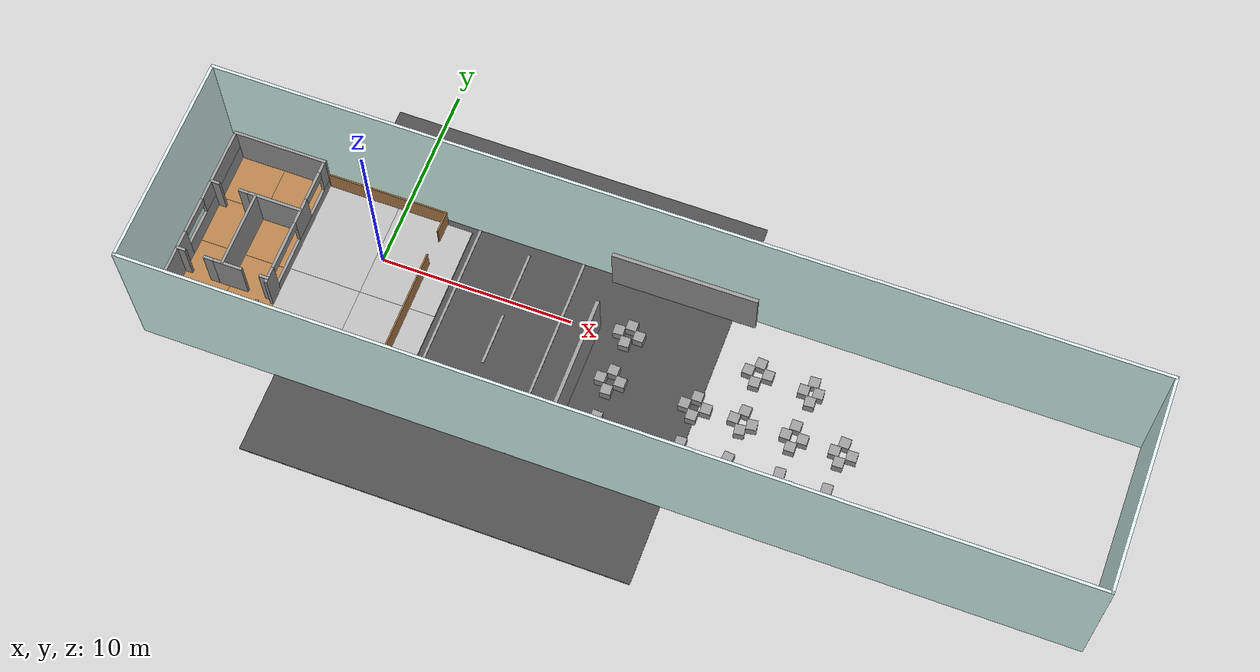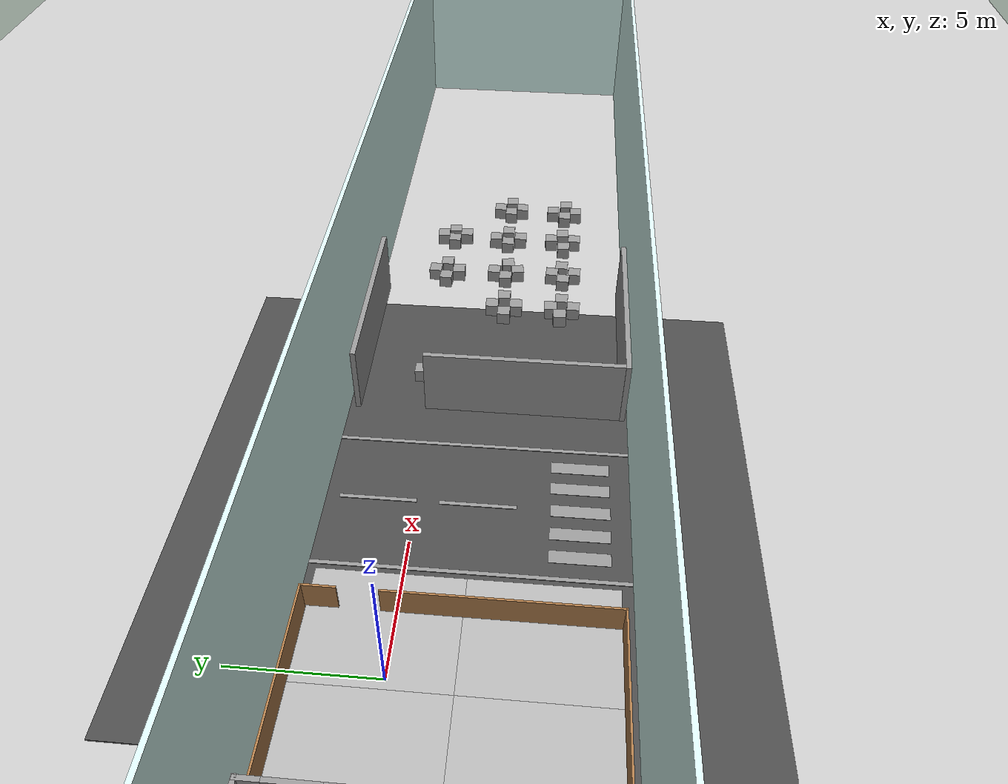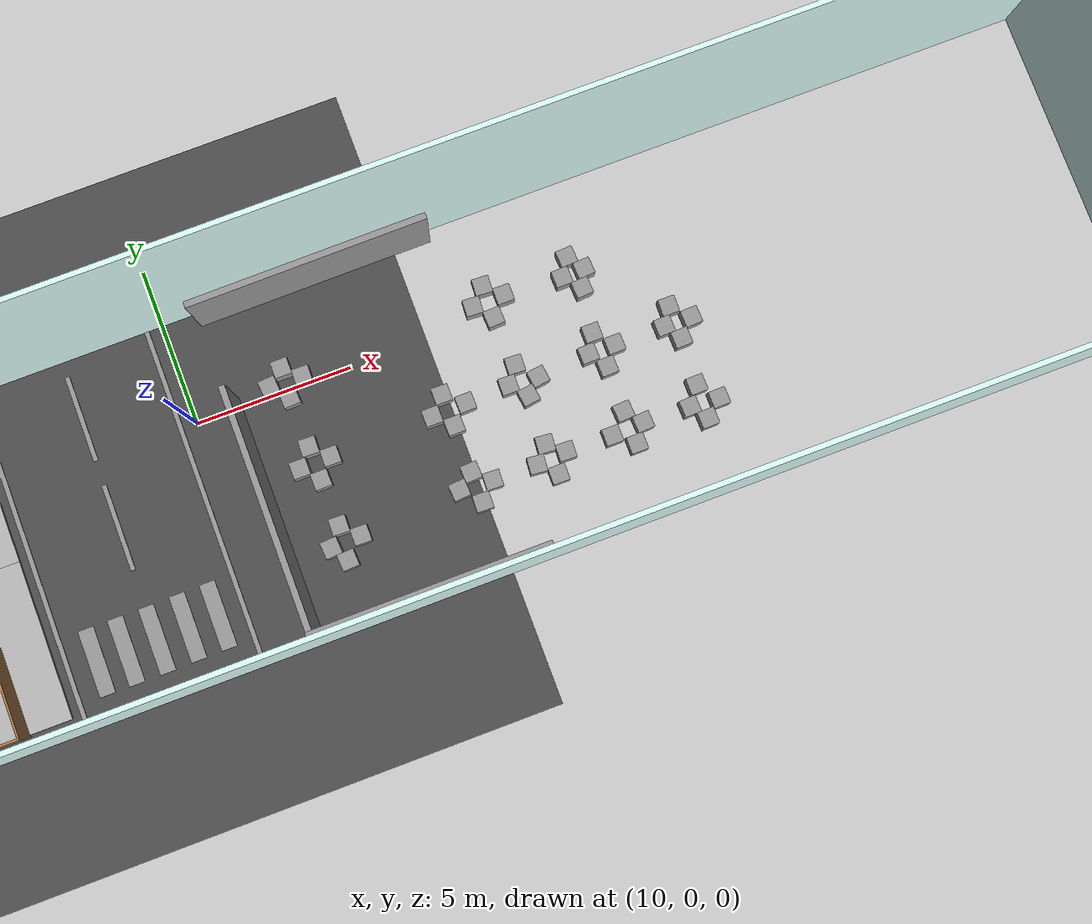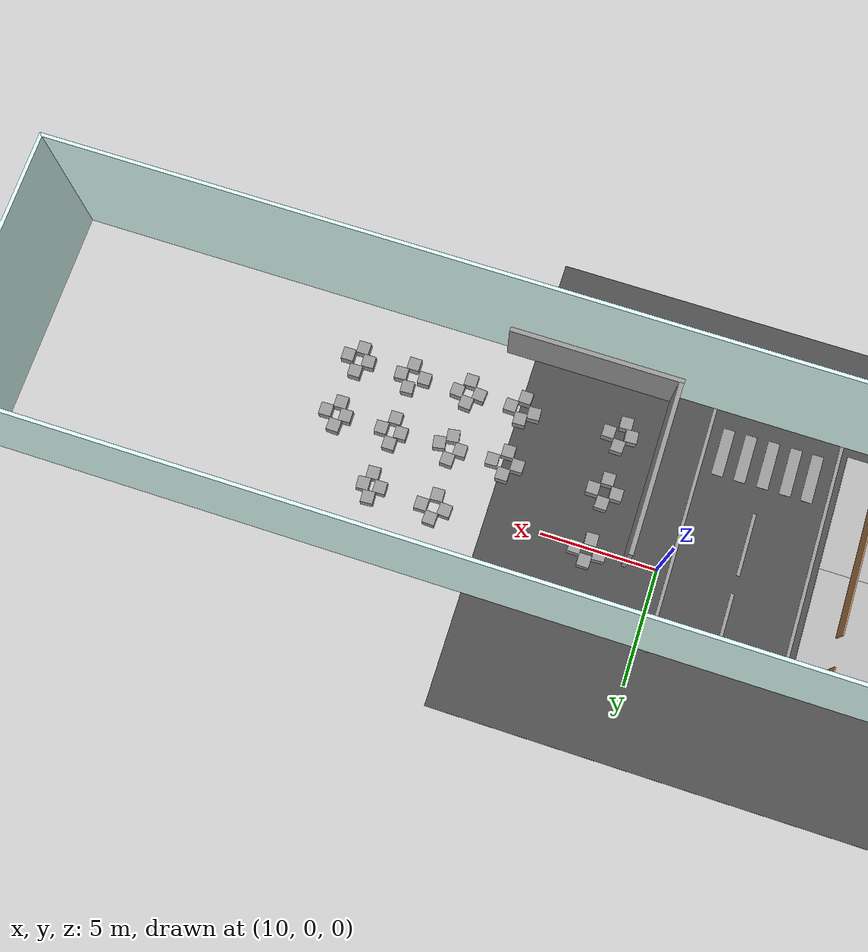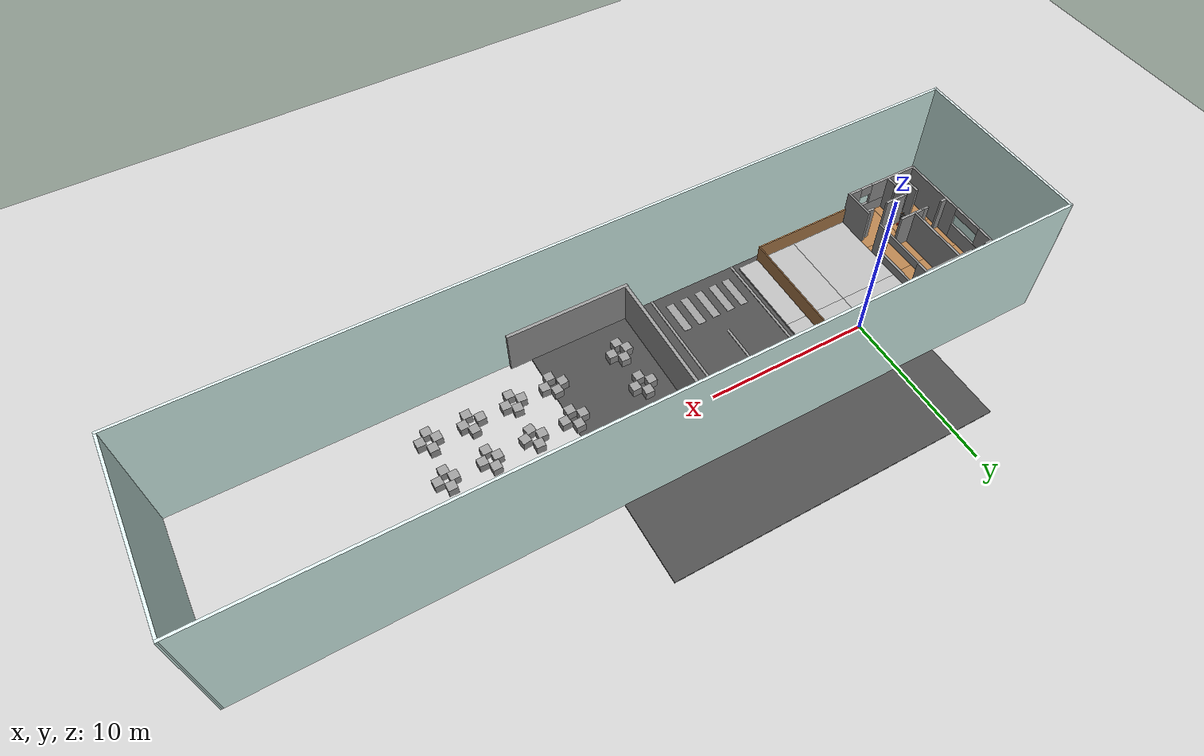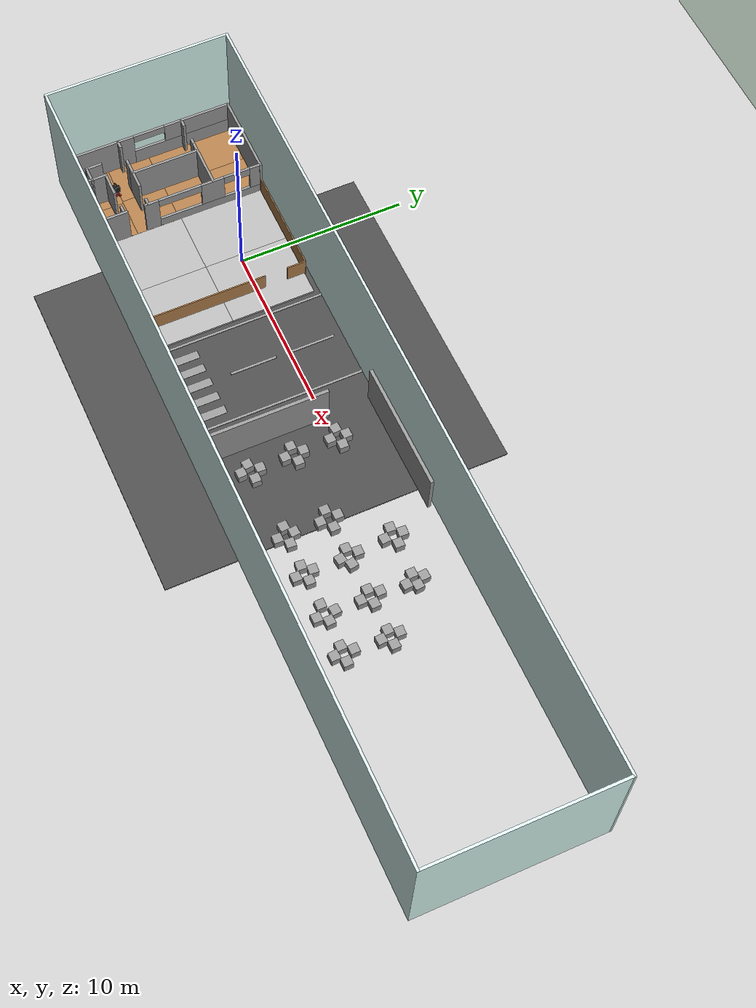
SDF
<sdf version="1.6">
 <world name="default">
  <light name="sun" type="directional">
   <pose>0 0 10 0 -0 0</pose>
   <diffuse>0.8 0.8 0.8 1</diffuse>
   <specular>0.2 0.2 0.2 1</specular>
   <attenuation>
    <range>1000</range>
    <constant>0.9</constant>
    <linear>0.01</linear>
    <quadratic>0.001</quadratic>
   </attenuation>
   <direction>-0.5 0.1 -0.9</direction>
  </light>
  <model name="ground_plane">
   <static>1</static>
   <link name="link">
    <collision name="collision">
     <geometry><plane><normal>0 0 1</normal><size>100 100</size></plane></geometry>
     <surface>
      <contact><collide_bitmask>65535</collide_bitmask></contact>
      <friction><ode><mu>100</mu><mu2>50</mu2></ode></friction>
     </surface>
    </collision>
    <visual name="visual">
     <cast_shadows>0</cast_shadows>
     <geometry><plane><normal>0 0 1</normal><size>100 100</size></plane></geometry>
     <material>
      <script><uri>file://media/materials/scripts/gazebo.material</uri><name>Gazebo/Grey</name></script>
     </material>
    </visual>
   </link>
  </model>
  <gravity>0 0 -9.8</gravity>
  <magnetic_field>6e-06 2.3e-05 -4.2e-05</magnetic_field>
  <atmosphere type="adiabatic"/>
  <physics name="default_physics" default="0" type="ode">
   <max_step_size>0.001</max_step_size>
   <real_time_factor>1</real_time_factor>
   <real_time_update_rate>1000</real_time_update_rate>
  </physics>
  <scene><ambient>0.4 0.4 0.4 1</ambient><background>0.7 0.7 0.7 1</background><shadows>1</shadows></scene>
  <spherical_coordinates>
   <surface_model>EARTH_WGS84</surface_model>
   <latitude_deg>0</latitude_deg>
   <longitude_deg>0</longitude_deg>
   <elevation>0</elevation>
   <heading_deg>0</heading_deg>
  </spherical_coordinates>
  <model name="grey_wall">
   <static>1</static>
   <link name="link">
    <pose>0 0 1.4 0 -0 0</pose>
    <collision name="collision"><geometry><box><size>7.5 0.2 2.8</size></box></geometry></collision>
    <visual name="visual">
     <cast_shadows>0</cast_shadows>
     <geometry><box><size>7.5 0.2 2.8</size></box></geometry>
     <material>
      <script>
       <uri>model://grey_wall/materials/scripts</uri>
       <uri>model://grey_wall/materials/textures</uri>
       <name>vrc/grey_wall</name>
      </script>
     </material>
    </visual>
   </link>
   <pose>14.888 2.91481 0 0 -0 0.005635</pose>
  </model>
  <model name="grey_wall_1">
   <static>1</static>
   <link name="link">
    <pose>0 0 1.4 0 -0 0</pose>
    <collision name="collision"><geometry><box><size>7.5 0.2 2.8</size></box></geometry></collision>
    <visual name="visual">
     <cast_shadows>0</cast_shadows>
     <geometry><box><size>7.5 0.2 2.8</size></box></geometry>
     <material>
      <script>
       <uri>model://grey_wall/materials/scripts</uri>
       <uri>model://grey_wall/materials/textures</uri>
       <name>vrc/grey_wall</name>
      </script>
     </material>
    </visual>
   </link>
   <pose>11.3606 -3.46174 0 0 -0 1.56876</pose>
  </model>
  <model name="mud_box">
   <static>1</static>
   <link name="link">
    <collision name="collision"><geometry><box><size>8 10 0.2</size></box></geometry></collision>
    <visual name="visual_1">
     <pose>-2 2.5 0 0 -0 0</pose>
     <cast_shadows>0</cast_shadows>
     <geometry><box><size>4 5 0.2</size></box></geometry>
     <material>
      <script>
       <uri>model://mud_box/materials/scripts</uri>
       <uri>model://mud_box/materials/textures</uri>
       <name>vrc/mud</name>
      </script>
     </material>
    </visual>
    <visual name="visual_2">
     <pose>2 2.5 0 0 -0 0</pose>
     <cast_shadows>0</cast_shadows>
     <geometry><box><size>4 5 0.2</size></box></geometry>
     <material>
      <script>
       <uri>model://mud_box/materials/scripts</uri>
       <uri>model://mud_box/materials/textures</uri>
       <name>vrc/mud</name>
      </script>
     </material>
    </visual>
    <visual name="visual_3">
     <pose>2 -2.5 0 0 -0 0</pose>
     <cast_shadows>0</cast_shadows>
     <geometry><box><size>4 5 0.2</size></box></geometry>
     <material>
      <script>
       <uri>model://mud_box/materials/scripts</uri>
       <uri>model://mud_box/materials/textures</uri>
       <name>vrc/mud</name>
      </script>
     </material>
    </visual>
    <visual name="visual_4">
     <pose>-2 -2.5 0 0 -0 0</pose>
     <cast_shadows>0</cast_shadows>
     <geometry><box><size>4 5 0.2</size></box></geometry>
     <material>
      <script>
       <uri>model://mud_box/materials/scripts</uri>
       <uri>model://mud_box/materials/textures</uri>
       <name>vrc/mud</name>
      </script>
     </material>
    </visual>
   </link>
   <pose>-0.378067 -2.09967 0.049154 0 -0 0</pose>
  </model>
  <model name="grey_wall_clone">
   <static>1</static>
   <link name="link">
    <pose>0 0 1.4 0 -0 0</pose>
    <collision name="collision"><geometry><box><size>7.5 0.2 2.8</size></box></geometry></collision>
    <visual name="visual">
     <cast_shadows>0</cast_shadows>
     <geometry><box><size>7.5 0.2 2.8</size></box></geometry>
     <material>
      <script>
       <uri>model://grey_wall/materials/scripts</uri>
       <uri>model://grey_wall/materials/textures</uri>
       <name>vrc/grey_wall</name>
      </script>
     </material>
    </visual>
   </link>
   <pose>14.9849 -7.30049 0 0 -0 0</pose>
  </model>
  <light name="user_point_light_4" type="point">
   <pose>6.4087 0.544728 1 0 -0 0</pose>
   <diffuse>0.5 0.5 0.5 1</diffuse>
   <specular>0.1 0.1 0.1 1</specular>
   <attenuation>
    <range>20</range>
    <constant>0.5</constant>
    <linear>0.01</linear>
    <quadratic>0.001</quadratic>
   </attenuation>
   <cast_shadows>0</cast_shadows>
   <direction>0 0 -1</direction>
  </light>
  <light name="user_spot_light_0" type="spot">
   <pose>-5.83278 -2.08373 1 0 -0 0</pose>
   <diffuse>0.5 0.5 0.5 1</diffuse>
   <specular>0.1 0.1 0.1 1</specular>
   <direction>0 0 -1</direction>
   <attenuation>
    <range>20</range>
    <constant>0.5</constant>
    <linear>0.01</linear>
    <quadratic>0.001</quadratic>
   </attenuation>
   <cast_shadows>0</cast_shadows>
   <spot><inner_angle>0.6</inner_angle><outer_angle>1</outer_angle><falloff>1</falloff></spot>
  </light>
  <light name="user_spot_light_1" type="spot">
   <pose>-6.75846 -0.732675 1 0 -0 0</pose>
   <diffuse>0.5 0.5 0.5 1</diffuse>
   <specular>0.1 0.1 0.1 1</specular>
   <direction>0 0 -1</direction>
   <attenuation>
    <range>20</range>
    <constant>0.5</constant>
    <linear>0.01</linear>
    <quadratic>0.001</quadratic>
   </attenuation>
   <cast_shadows>0</cast_shadows>
   <spot><inner_angle>0.6</inner_angle><outer_angle>1</outer_angle><falloff>1</falloff></spot>
  </light>
  <light name="user_spot_light_2" type="spot">
   <pose>-3.21859 -4.40289 1 0 -0 0</pose>
   <diffuse>0.5 0.5 0.5 1</diffuse>
   <specular>0.1 0.1 0.1 1</specular>
   <direction>0 0 -1</direction>
   <attenuation>
    <range>20</range>
    <constant>0.5</constant>
    <linear>0.01</linear>
    <quadratic>0.001</quadratic>
   </attenuation>
   <cast_shadows>0</cast_shadows>
   <spot><inner_angle>0.6</inner_angle><outer_angle>1</outer_angle><falloff>1</falloff></spot>
  </light>
  <model name="my_wheelchair">
   <link name="base_link">
    <inertial>
     <pose>-0.034207 0 0.161841 0 -0 0</pose>
     <mass>1.90002</mass>
     <inertia>
      <ixx>0.262673</ixx>
      <ixy>-2.37357e-19</ixy>
      <ixz>0.0372307</ixz>
      <iyy>0.501077</iyy>
      <iyz>-7.85195e-19</iyz>
      <izz>0.433656</izz>
     </inertia>
    </inertial>
    <collision name="base_link_collision"><geometry><box><size>0.5 0.4 0.2</size></box></geometry></collision>
    <collision name="base_link_fixed_joint_lump__chair_pillar_collision_1">
     <pose>0 0 0.175 0 -0 0</pose>
     <geometry><cylinder><length>0.2</length><radius>0.075</radius></cylinder></geometry>
    </collision>
    <collision name="base_link_fixed_joint_lump__chair_seat_collision_2">
     <pose>0 0 0.275 0 -0 0</pose>
     <geometry><box><size>0.6 0.5 0.1</size></box></geometry>
    </collision>
    <collision name="base_link_fixed_joint_lump__arm_brace_left_collision_3">
     <pose>-0.2 0.225 0.375 0 -0 0</pose>
     <geometry><box><size>0.05 0.025 0.25</size></box></geometry>
    </collision>
    <collision name="base_link_fixed_joint_lump__arm_left_collision_4">
     <pose>0 0.25 0.5 0 -0 0</pose>
     <geometry><box><size>0.45 0.075 0.03</size></box></geometry>
    </collision>
    <collision name="base_link_fixed_joint_lump__arm_brace_right_collision_5">
     <pose>-0.2 -0.225 0.375 0 -0 0</pose>
     <geometry><box><size>0.05 0.025 0.25</size></box></geometry>
    </collision>
    <collision name="base_link_fixed_joint_lump__arm_right_collision_6">
     <pose>0 -0.25 0.5 0 -0 0</pose>
     <geometry><box><size>0.45 0.075 0.03</size></box></geometry>
    </collision>
    <collision name="base_link_fixed_joint_lump__chair_spine_collision_7">
     <pose>-0.3 0 0.375 0 -0 0</pose>
     <geometry><box><size>0.035 0.1 0.2</size></box></geometry>
    </collision>
    <collision name="base_link_fixed_joint_lump__chair_back_collision_8">
     <pose>-0.3 0 0.6 0 -0 0</pose>
     <geometry><box><size>0.2 0.25 0.6</size></box></geometry>
    </collision>
    <collision name="base_link_fixed_joint_lump__foot_rest_collision_9">
     <pose>0.35 0 -0.1 0 -0 0</pose>
     <geometry><box><size>0.2 0.25 0.01</size></box></geometry>
    </collision>
    <collision name="base_link_fixed_joint_lump__hokuyo_main_collision_10">
     <pose>0.3 0 0.1 0 -0 0</pose>
     <geometry><box><size>0.1 0.1 0.1</size></box></geometry>
    </collision>
    <collision name="base_link_fixed_joint_lump__hokuyo_main_pointer_collision_11">
     <pose>0.35 0 0.1 0 -0 0</pose>
     <geometry><sphere><radius>0.02</radius></sphere></geometry>
    </collision>
    <visual name="base_link_visual">
     <geometry><box><size>0.5 0.4 0.2</size></box></geometry>
     <material>
      <script><name>Gazebo/Red</name><uri>file://media/materials/scripts/gazebo.material</uri></script>
     </material>
    </visual>
    <visual name="base_link_fixed_joint_lump__chair_pillar_visual_1">
     <pose>0 0 0.175 0 -0 0</pose>
     <geometry><cylinder><length>0.2</length><radius>0.075</radius></cylinder></geometry>
    </visual>
    <visual name="base_link_fixed_joint_lump__chair_seat_visual_2">
     <pose>0 0 0.275 0 -0 0</pose>
     <geometry><box><size>0.6 0.45 0.1</size></box></geometry>
     <material>
      <script><name>Gazebo/Black</name><uri>file://media/materials/scripts/gazebo.material</uri></script>
     </material>
    </visual>
    <visual name="base_link_fixed_joint_lump__arm_brace_left_visual_3">
     <pose>-0.2 0.225 0.375 0 -0 0</pose>
     <geometry><box><size>0.05 0.03 0.25</size></box></geometry>
    </visual>
    <visual name="base_link_fixed_joint_lump__arm_left_visual_4">
     <pose>0 0.25 0.5 0 -0 0</pose>
     <geometry><box><size>0.45 0.075 0.03</size></box></geometry>
     <material>
      <script><name>Gazebo/Black</name><uri>file://media/materials/scripts/gazebo.material</uri></script>
     </material>
    </visual>
    <visual name="base_link_fixed_joint_lump__arm_brace_right_visual_5">
     <pose>-0.2 -0.225 0.375 0 -0 0</pose>
     <geometry><box><size>0.05 0.03 0.25</size></box></geometry>
    </visual>
    <visual name="base_link_fixed_joint_lump__arm_right_visual_6">
     <pose>0 -0.25 0.5 0 -0 0</pose>
     <geometry><box><size>0.45 0.075 0.03</size></box></geometry>
     <material>
      <script><name>Gazebo/Black</name><uri>file://media/materials/scripts/gazebo.material</uri></script>
     </material>
    </visual>
    <visual name="base_link_fixed_joint_lump__chair_spine_visual_7">
     <pose>-0.3 0 0.375 0 -0 0</pose>
     <geometry><box><size>0.035 0.1 0.2</size></box></geometry>
     <material>
      <script><name>Gazebo/Black</name><uri>file://media/materials/scripts/gazebo.material</uri></script>
     </material>
    </visual>
    <visual name="base_link_fixed_joint_lump__chair_back_visual_8">
     <pose>-0.3 0 0.6 0 -0 0</pose>
     <geometry><box><size>0.1 0.45 0.5</size></box></geometry>
     <material>
      <script><name>Gazebo/Black</name><uri>file://media/materials/scripts/gazebo.material</uri></script>
     </material>
    </visual>
    <visual name="base_link_fixed_joint_lump__foot_rest_visual_9">
     <pose>0.35 0 -0.1 0 -0 0</pose>
     <geometry><box><size>0.2 0.25 0.01</size></box></geometry>
     <material>
      <script><name>Gazebo/Black</name><uri>file://media/materials/scripts/gazebo.material</uri></script>
     </material>
    </visual>
    <visual name="base_link_fixed_joint_lump__hokuyo_main_visual_10">
     <pose>0.3 0 0.1 0 -0 0</pose>
     <geometry><box><size>0.1 0.1 0.1</size></box></geometry>
     <material>
      <script><name>Gazebo/Black</name><uri>file://media/materials/scripts/gazebo.material</uri></script>
     </material>
    </visual>
    <visual name="base_link_fixed_joint_lump__hokuyo_main_pointer_visual_11">
     <pose>0.35 0 0.1 0 -0 0</pose>
     <geometry><sphere><radius>0.02</radius></sphere></geometry>
     <material>
      <script><name>Gazebo/Blue</name><uri>file://media/materials/scripts/gazebo.material</uri></script>
     </material>
    </visual>
    <sensor name="head_hokuyo_sensor" type="ray">
     <visualize>0</visualize>
     <update_rate>40</update_rate>
     <ray>
      <scan>
       <horizontal>
        <samples>720</samples>
        <resolution>1</resolution>
        <min_angle>-1.5708</min_angle>
        <max_angle>1.5708</max_angle>
       </horizontal>
       <vertical><samples>1</samples><min_angle>0</min_angle><max_angle>0</max_angle></vertical>
      </scan>
      <range><min>0.1</min><max>30</max><resolution>0.01</resolution></range>
      <noise><type>gaussian</type><mean>0</mean><stddev>0.01</stddev></noise>
     </ray>
     <plugin name="gazebo_ros_head_hokuyo_controller" filename="libgazebo_ros_laser.so">
      <topicName>scan</topicName>
      <frameName>hokuyo_main</frameName>
      <robotNamespace>/</robotNamespace>
     </plugin>
     <pose>0.3 0 0.1 0 -0 0</pose>
    </sensor>
   </link>
   <link name="back_left_caster">
    <pose>-0.3 0.2 -0.05 0 -0 0</pose>
    <inertial>
     <mass>0.1</mass>
     <inertia><ixx>0.00083</ixx><ixy>0</ixy><ixz>0</ixz><iyy>0.00083</iyy><iyz>0</iyz><izz>0.000167</izz></inertia>
    </inertial>
    <collision name="back_left_caster_collision">
     <geometry><box><size>0.1 0.1 0.15</size></box></geometry>
    </collision>
    <visual name="back_left_caster_visual">
     <geometry><box><size>0.1 0.1 0.15</size></box></geometry>
     <material>
      <script><name>Gazebo/Red</name><uri>file://media/materials/scripts/gazebo.material</uri></script>
     </material>
    </visual>
   </link>
   <joint name="back_left_caster_joint" type="revolute">
    <child>back_left_caster</child>
    <parent>base_link</parent>
    <axis>
     <xyz>0 0 1</xyz>
     <limit><lower>-1e+16</lower><upper>1e+16</upper></limit>
     <dynamics><spring_reference>0</spring_reference><spring_stiffness>0</spring_stiffness></dynamics>
     <use_parent_model_frame>1</use_parent_model_frame>
    </axis>
   </joint>
   <link name="back_left_wheel">
    <pose>-0.25 0.2 -0.125 -1.5708 0 0</pose>
    <inertial>
     <mass>0.1</mass>
     <inertia>
      <ixx>5.1458e-05</ixx>
      <ixy>0</ixy>
      <ixz>0</ixz>
      <iyy>5.1458e-05</iyy>
      <iyz>0</iyz>
      <izz>6.125e-05</izz>
     </inertia>
    </inertial>
    <collision name="back_left_wheel_collision">
     <geometry><cylinder><length>0.05</length><radius>0.065</radius></cylinder></geometry>
    </collision>
    <visual name="back_left_wheel_visual">
     <geometry><cylinder><length>0.05</length><radius>0.065</radius></cylinder></geometry>
     <material>
      <script><name>Gazebo/Black</name><uri>file://media/materials/scripts/gazebo.material</uri></script>
     </material>
    </visual>
   </link>
   <joint name="back_left_wheel_joint" type="revolute">
    <child>back_left_wheel</child>
    <parent>back_left_caster</parent>
    <axis>
     <xyz>0 1 -4e-06</xyz>
     <limit><lower>-1e+16</lower><upper>1e+16</upper></limit>
     <dynamics><spring_reference>0</spring_reference><spring_stiffness>0</spring_stiffness></dynamics>
     <use_parent_model_frame>1</use_parent_model_frame>
    </axis>
   </joint>
   <link name="back_right_caster">
    <pose>-0.3 -0.2 -0.05 0 -0 0</pose>
    <inertial>
     <mass>0.1</mass>
     <inertia><ixx>0.00083</ixx><ixy>0</ixy><ixz>0</ixz><iyy>0.00083</iyy><iyz>0</iyz><izz>0.000167</izz></inertia>
    </inertial>
    <collision name="back_right_caster_collision">
     <geometry><box><size>0.1 0.1 0.15</size></box></geometry>
    </collision>
    <visual name="back_right_caster_visual">
     <geometry><box><size>0.1 0.1 0.15</size></box></geometry>
     <material>
      <script><name>Gazebo/Red</name><uri>file://media/materials/scripts/gazebo.material</uri></script>
     </material>
    </visual>
   </link>
   <joint name="back_right_caster_joint" type="revolute">
    <child>back_right_caster</child>
    <parent>base_link</parent>
    <axis>
     <xyz>0 0 1</xyz>
     <limit><lower>-1e+16</lower><upper>1e+16</upper></limit>
     <dynamics><spring_reference>0</spring_reference><spring_stiffness>0</spring_stiffness></dynamics>
     <use_parent_model_frame>1</use_parent_model_frame>
    </axis>
   </joint>
   <link name="back_right_wheel">
    <pose>-0.25 -0.2 -0.125 -1.5708 0 0</pose>
    <inertial>
     <mass>0.1</mass>
     <inertia>
      <ixx>5.1458e-05</ixx>
      <ixy>0</ixy>
      <ixz>0</ixz>
      <iyy>5.1458e-05</iyy>
      <iyz>0</iyz>
      <izz>6.125e-05</izz>
     </inertia>
    </inertial>
    <collision name="back_right_wheel_collision">
     <geometry><cylinder><length>0.05</length><radius>0.065</radius></cylinder></geometry>
    </collision>
    <visual name="back_right_wheel_visual">
     <geometry><cylinder><length>0.05</length><radius>0.065</radius></cylinder></geometry>
     <material>
      <script><name>Gazebo/Black</name><uri>file://media/materials/scripts/gazebo.material</uri></script>
     </material>
    </visual>
   </link>
   <joint name="back_right_wheel_joint" type="revolute">
    <child>back_right_wheel</child>
    <parent>back_right_caster</parent>
    <axis>
     <xyz>0 1 -4e-06</xyz>
     <limit><lower>-1e+16</lower><upper>1e+16</upper></limit>
     <dynamics><spring_reference>0</spring_reference><spring_stiffness>0</spring_stiffness></dynamics>
     <use_parent_model_frame>1</use_parent_model_frame>
    </axis>
   </joint>
   <link name="front_left_caster">
    <pose>0.3 0.2 -0.05 0 -0 0</pose>
    <inertial>
     <mass>0.1</mass>
     <inertia><ixx>0.00083</ixx><ixy>0</ixy><ixz>0</ixz><iyy>0.00083</iyy><iyz>0</iyz><izz>0.000167</izz></inertia>
    </inertial>
    <collision name="front_left_caster_collision">
     <geometry><box><size>0.1 0.1 0.15</size></box></geometry>
    </collision>
    <visual name="front_left_caster_visual">
     <geometry><box><size>0.1 0.1 0.15</size></box></geometry>
     <material>
      <script><name>Gazebo/Red</name><uri>file://media/materials/scripts/gazebo.material</uri></script>
     </material>
    </visual>
   </link>
   <joint name="front_left_caster_joint" type="revolute">
    <child>front_left_caster</child>
    <parent>base_link</parent>
    <axis>
     <xyz>0 0 1</xyz>
     <limit><lower>-1e+16</lower><upper>1e+16</upper></limit>
     <dynamics><spring_reference>0</spring_reference><spring_stiffness>0</spring_stiffness></dynamics>
     <use_parent_model_frame>1</use_parent_model_frame>
    </axis>
   </joint>
   <link name="front_left_wheel">
    <pose>0.35 0.2 -0.125 -1.5708 0 0</pose>
    <inertial>
     <mass>0.1</mass>
     <inertia>
      <ixx>5.1458e-05</ixx>
      <ixy>0</ixy>
      <ixz>0</ixz>
      <iyy>5.1458e-05</iyy>
      <iyz>0</iyz>
      <izz>6.125e-05</izz>
     </inertia>
    </inertial>
    <collision name="front_left_wheel_collision">
     <geometry><cylinder><length>0.05</length><radius>0.065</radius></cylinder></geometry>
    </collision>
    <visual name="front_left_wheel_visual">
     <geometry><cylinder><length>0.05</length><radius>0.065</radius></cylinder></geometry>
     <material>
      <script><name>Gazebo/Black</name><uri>file://media/materials/scripts/gazebo.material</uri></script>
     </material>
    </visual>
   </link>
   <joint name="front_left_wheel_joint" type="revolute">
    <child>front_left_wheel</child>
    <parent>front_left_caster</parent>
    <axis>
     <xyz>0 1 -4e-06</xyz>
     <limit><lower>-1e+16</lower><upper>1e+16</upper></limit>
     <dynamics><spring_reference>0</spring_reference><spring_stiffness>0</spring_stiffness></dynamics>
     <use_parent_model_frame>1</use_parent_model_frame>
    </axis>
   </joint>
   <link name="front_right_caster">
    <pose>0.3 -0.2 -0.05 0 -0 0</pose>
    <inertial>
     <mass>0.1</mass>
     <inertia><ixx>0.00083</ixx><ixy>0</ixy><ixz>0</ixz><iyy>0.00083</iyy><iyz>0</iyz><izz>0.000167</izz></inertia>
    </inertial>
    <collision name="front_right_caster_collision">
     <geometry><box><size>0.1 0.1 0.15</size></box></geometry>
    </collision>
    <visual name="front_right_caster_visual">
     <geometry><box><size>0.1 0.1 0.15</size></box></geometry>
     <material>
      <script><name>Gazebo/Red</name><uri>file://media/materials/scripts/gazebo.material</uri></script>
     </material>
    </visual>
   </link>
   <joint name="front_right_caster_joint" type="revolute">
    <child>front_right_caster</child>
    <parent>base_link</parent>
    <axis>
     <xyz>0 0 1</xyz>
     <limit><lower>-1e+16</lower><upper>1e+16</upper></limit>
     <dynamics><spring_reference>0</spring_reference><spring_stiffness>0</spring_stiffness></dynamics>
     <use_parent_model_frame>1</use_parent_model_frame>
    </axis>
   </joint>
   <link name="front_right_wheel">
    <pose>0.35 -0.2 -0.125 -1.5708 0 0</pose>
    <inertial>
     <mass>0.1</mass>
     <inertia>
      <ixx>5.1458e-05</ixx>
      <ixy>0</ixy>
      <ixz>0</ixz>
      <iyy>5.1458e-05</iyy>
      <iyz>0</iyz>
      <izz>6.125e-05</izz>
     </inertia>
    </inertial>
    <collision name="front_right_wheel_collision">
     <geometry><cylinder><length>0.05</length><radius>0.065</radius></cylinder></geometry>
    </collision>
    <visual name="front_right_wheel_visual">
     <geometry><cylinder><length>0.05</length><radius>0.065</radius></cylinder></geometry>
     <material>
      <script><name>Gazebo/Black</name><uri>file://media/materials/scripts/gazebo.material</uri></script>
     </material>
    </visual>
   </link>
   <joint name="front_right_wheel_joint" type="revolute">
    <child>front_right_wheel</child>
    <parent>front_right_caster</parent>
    <axis>
     <xyz>0 1 -4e-06</xyz>
     <limit><lower>-1e+16</lower><upper>1e+16</upper></limit>
     <dynamics><spring_reference>0</spring_reference><spring_stiffness>0</spring_stiffness></dynamics>
     <use_parent_model_frame>1</use_parent_model_frame>
    </axis>
   </joint>
   <link name="left_wheel">
    <pose>0 0.25 -0.065 -1.5708 0 0</pose>
    <inertial>
     <mass>0.1</mass>
     <inertia>
      <ixx>5.1458e-05</ixx>
      <ixy>0</ixy>
      <ixz>0</ixz>
      <iyy>5.1458e-05</iyy>
      <iyz>0</iyz>
      <izz>6.125e-05</izz>
     </inertia>
    </inertial>
    <collision name="left_wheel_collision">
     <geometry><cylinder><length>0.075</length><radius>0.125</radius></cylinder></geometry>
    </collision>
    <visual name="left_wheel_visual">
     <geometry><cylinder><length>0.075</length><radius>0.125</radius></cylinder></geometry>
     <material>
      <script><name>Gazebo/Black</name><uri>file://media/materials/scripts/gazebo.material</uri></script>
     </material>
    </visual>
   </link>
   <joint name="left_wheel_joint" type="revolute">
    <child>left_wheel</child>
    <parent>base_link</parent>
    <axis>
     <xyz>0 1 -4e-06</xyz>
     <limit><lower>-1e+16</lower><upper>1e+16</upper></limit>
     <dynamics><spring_reference>0</spring_reference><spring_stiffness>0</spring_stiffness></dynamics>
     <use_parent_model_frame>1</use_parent_model_frame>
    </axis>
   </joint>
   <link name="right_wheel">
    <pose>0 -0.25 -0.065 -1.5708 0 0</pose>
    <inertial>
     <mass>0.1</mass>
     <inertia>
      <ixx>5.1458e-05</ixx>
      <ixy>0</ixy>
      <ixz>0</ixz>
      <iyy>5.1458e-05</iyy>
      <iyz>0</iyz>
      <izz>6.125e-05</izz>
     </inertia>
    </inertial>
    <collision name="right_wheel_collision">
     <geometry><cylinder><length>0.075</length><radius>0.125</radius></cylinder></geometry>
    </collision>
    <visual name="right_wheel_visual">
     <geometry><cylinder><length>0.075</length><radius>0.125</radius></cylinder></geometry>
     <material>
      <script><name>Gazebo/Black</name><uri>file://media/materials/scripts/gazebo.material</uri></script>
     </material>
    </visual>
   </link>
   <joint name="right_wheel_joint" type="revolute">
    <child>right_wheel</child>
    <parent>base_link</parent>
    <axis>
     <xyz>0 1 -4e-06</xyz>
     <limit><lower>-1e+16</lower><upper>1e+16</upper></limit>
     <dynamics><spring_reference>0</spring_reference><spring_stiffness>0</spring_stiffness></dynamics>
     <use_parent_model_frame>1</use_parent_model_frame>
    </axis>
   </joint>
   <plugin name="joint_state_publisher" filename="libgazebo_ros_joint_state_publisher.so">
    <jointName>front_left_caster_joint, front_left_wheel_joint</jointName>
    <robotNamespace>/</robotNamespace>
   </plugin>
   <plugin name="joint_state_publisher" filename="libgazebo_ros_joint_state_publisher.so">
    <jointName>front_right_caster_joint, front_right_wheel_joint</jointName>
    <robotNamespace>/</robotNamespace>
   </plugin>
   <plugin name="joint_state_publisher" filename="libgazebo_ros_joint_state_publisher.so">
    <jointName>back_left_caster_joint, back_left_wheel_joint</jointName>
    <robotNamespace>/</robotNamespace>
   </plugin>
   <plugin name="joint_state_publisher" filename="libgazebo_ros_joint_state_publisher.so">
    <jointName>back_right_caster_joint, back_right_wheel_joint</jointName>
    <robotNamespace>/</robotNamespace>
   </plugin>
   <static>0</static>
   <plugin name="differential_drive_controller" filename="libgazebo_ros_diff_drive.so">
    <leftJoint>right_wheel_joint</leftJoint>
    <rightJoint>left_wheel_joint</rightJoint>
    <robotBaseFrame>base_link</robotBaseFrame>
    <wheelSeparation>0.25</wheelSeparation>
    <wheelDiameter>0.07</wheelDiameter>
    <publishWheelJointState>true</publishWheelJointState>
    <robotNamespace>/</robotNamespace>
   </plugin>
   <pose>-7.22746 -5.05903 0.345 0 -4e-06 -2.83679</pose>
  </model>
  <model name="unit_box_0_clone_10">
   <pose>17.839 -4.81532 0.314113 0 0 -0.045272</pose>
   <link name="link">
    <inertial>
     <mass>1</mass>
     <inertia>
      <ixx>0.166667</ixx>
      <ixy>0</ixy>
      <ixz>0</ixz>
      <iyy>0.166667</iyy>
      <iyz>0</iyz>
      <izz>0.166667</izz>
     </inertia>
    </inertial>
    <collision name="collision">
     <geometry><box><size>0.530101 0.530101 0.530101</size></box></geometry>
    </collision>
    <visual name="visual">
     <geometry><box><size>0.530101 0.530101 0.530101</size></box></geometry>
     <material>
      <script><name>Gazebo/Grey</name><uri>file://media/materials/scripts/gazebo.material</uri></script>
     </material>
    </visual>
   </link>
  </model>
  <model name="unit_box_0_clone_11">
   <pose>16.7922 -4.75542 0.314113 0 -0 0.068769</pose>
   <link name="link">
    <inertial>
     <mass>1</mass>
     <inertia>
      <ixx>0.166667</ixx>
      <ixy>0</ixy>
      <ixz>0</ixz>
      <iyy>0.166667</iyy>
      <iyz>0</iyz>
      <izz>0.166667</izz>
     </inertia>
    </inertial>
    <collision name="collision">
     <geometry><box><size>0.530101 0.530101 0.530101</size></box></geometry>
    </collision>
    <visual name="visual">
     <geometry><box><size>0.530101 0.530101 0.530101</size></box></geometry>
     <material>
      <script><name>Gazebo/Grey</name><uri>file://media/materials/scripts/gazebo.material</uri></script>
     </material>
    </visual>
   </link>
  </model>
  <model name="unit_box_0_clone_12">
   <pose>17.3054 -4.3621 0.314111 -1.1e-05 6e-06 0.040973</pose>
   <link name="link">
    <inertial>
     <mass>1</mass>
     <inertia>
      <ixx>0.166667</ixx>
      <ixy>0</ixy>
      <ixz>0</ixz>
      <iyy>0.166667</iyy>
      <iyz>0</iyz>
      <izz>0.166667</izz>
     </inertia>
    </inertial>
    <collision name="collision">
     <geometry><box><size>0.530101 0.530101 0.530101</size></box></geometry>
    </collision>
    <visual name="visual">
     <geometry><box><size>0.530101 0.530101 0.530101</size></box></geometry>
     <material>
      <script><name>Gazebo/Grey</name><uri>file://media/materials/scripts/gazebo.material</uri></script>
     </material>
    </visual>
   </link>
  </model>
  <model name="unit_box_0_clone_13">
   <pose>17.3287 -5.32941 0.314113 0 0 -0.026623</pose>
   <link name="link">
    <inertial>
     <mass>1</mass>
     <inertia>
      <ixx>0.166667</ixx>
      <ixy>0</ixy>
      <ixz>0</ixz>
      <iyy>0.166667</iyy>
      <iyz>0</iyz>
      <izz>0.166667</izz>
     </inertia>
    </inertial>
    <collision name="collision">
     <geometry><box><size>0.530101 0.530101 0.530101</size></box></geometry>
    </collision>
    <visual name="visual">
     <geometry><box><size>0.530101 0.530101 0.530101</size></box></geometry>
     <material>
      <script><name>Gazebo/Grey</name><uri>file://media/materials/scripts/gazebo.material</uri></script>
     </material>
    </visual>
   </link>
  </model>
  <model name="unit_box_0_clone_18">
   <pose>19.1218 0.363804 0.314113 0 0 -0.050966</pose>
   <link name="link">
    <inertial>
     <mass>1</mass>
     <inertia>
      <ixx>0.166667</ixx>
      <ixy>0</ixy>
      <ixz>0</ixz>
      <iyy>0.166667</iyy>
      <iyz>0</iyz>
      <izz>0.166667</izz>
     </inertia>
    </inertial>
    <collision name="collision">
     <geometry><box><size>0.530101 0.530101 0.530101</size></box></geometry>
    </collision>
    <visual name="visual">
     <geometry><box><size>0.530101 0.530101 0.530101</size></box></geometry>
     <material>
      <script><name>Gazebo/Grey</name><uri>file://media/materials/scripts/gazebo.material</uri></script>
     </material>
    </visual>
   </link>
  </model>
  <model name="unit_box_0_clone_19">
   <pose>19.61 0.8688 0.314108 -7e-06 -1.1e-05 -0.055582</pose>
   <link name="link">
    <inertial>
     <mass>1</mass>
     <inertia>
      <ixx>0.166667</ixx>
      <ixy>0</ixy>
      <ixz>0</ixz>
      <iyy>0.166667</iyy>
      <iyz>0</iyz>
      <izz>0.166667</izz>
     </inertia>
    </inertial>
    <collision name="collision">
     <geometry><box><size>0.530101 0.530101 0.530101</size></box></geometry>
    </collision>
    <visual name="visual">
     <geometry><box><size>0.530101 0.530101 0.530101</size></box></geometry>
     <material>
      <script><name>Gazebo/Grey</name><uri>file://media/materials/scripts/gazebo.material</uri></script>
     </material>
    </visual>
   </link>
  </model>
  <model name="unit_box_0_clone_20">
   <pose>20.1335 0.39458 0.314113 2e-06 0 -0.001749</pose>
   <link name="link">
    <inertial>
     <mass>1</mass>
     <inertia>
      <ixx>0.166667</ixx>
      <ixy>0</ixy>
      <ixz>0</ixz>
      <iyy>0.166667</iyy>
      <iyz>0</iyz>
      <izz>0.166667</izz>
     </inertia>
    </inertial>
    <collision name="collision">
     <geometry><box><size>0.530101 0.530101 0.530101</size></box></geometry>
    </collision>
    <visual name="visual">
     <geometry><box><size>0.530101 0.530101 0.530101</size></box></geometry>
     <material>
      <script><name>Gazebo/Grey</name><uri>file://media/materials/scripts/gazebo.material</uri></script>
     </material>
    </visual>
   </link>
  </model>
  <model name="unit_box_0_clone_22">
   <pose>19.6936 -1.76089 0.314113 0 0 -0.043751</pose>
   <link name="link">
    <inertial>
     <mass>1</mass>
     <inertia>
      <ixx>0.166667</ixx>
      <ixy>0</ixy>
      <ixz>0</ixz>
      <iyy>0.166667</iyy>
      <iyz>0</iyz>
      <izz>0.166667</izz>
     </inertia>
    </inertial>
    <collision name="collision">
     <geometry><box><size>0.530101 0.530101 0.530101</size></box></geometry>
    </collision>
    <visual name="visual">
     <geometry><box><size>0.530101 0.530101 0.530101</size></box></geometry>
     <material>
      <script><name>Gazebo/Grey</name><uri>file://media/materials/scripts/gazebo.material</uri></script>
     </material>
    </visual>
   </link>
  </model>
  <model name="unit_box_0_clone_24">
   <pose>20.2313 -2.35129 0.314111 -1.1e-05 6e-06 0.142067</pose>
   <link name="link">
    <inertial>
     <mass>1</mass>
     <inertia>
      <ixx>0.166667</ixx>
      <ixy>0</ixy>
      <ixz>0</ixz>
      <iyy>0.166667</iyy>
      <iyz>0</iyz>
      <izz>0.166667</izz>
     </inertia>
    </inertial>
    <collision name="collision">
     <geometry><box><size>0.530101 0.530101 0.530101</size></box></geometry>
    </collision>
    <visual name="visual">
     <geometry><box><size>0.530101 0.530101 0.530101</size></box></geometry>
     <material>
      <script><name>Gazebo/Grey</name><uri>file://media/materials/scripts/gazebo.material</uri></script>
     </material>
    </visual>
   </link>
  </model>
  <model name="unit_box_0_clone_26">
   <pose>19.6965 -4.34869 0.314108 1e-05 7e-06 -0.080159</pose>
   <link name="link">
    <inertial>
     <mass>1</mass>
     <inertia>
      <ixx>0.166667</ixx>
      <ixy>0</ixy>
      <ixz>0</ixz>
      <iyy>0.166667</iyy>
      <iyz>0</iyz>
      <izz>0.166667</izz>
     </inertia>
    </inertial>
    <collision name="collision">
     <geometry><box><size>0.530101 0.530101 0.530101</size></box></geometry>
    </collision>
    <visual name="visual">
     <geometry><box><size>0.530101 0.530101 0.530101</size></box></geometry>
     <material>
      <script><name>Gazebo/Grey</name><uri>file://media/materials/scripts/gazebo.material</uri></script>
     </material>
    </visual>
   </link>
  </model>
  <model name="unit_box_0_clone_27">
   <pose>19.2516 -4.84569 0.314108 -7e-06 1.1e-05 -0.086107</pose>
   <link name="link">
    <inertial>
     <mass>1</mass>
     <inertia>
      <ixx>0.166667</ixx>
      <ixy>0</ixy>
      <ixz>0</ixz>
      <iyy>0.166667</iyy>
      <iyz>0</iyz>
      <izz>0.166667</izz>
     </inertia>
    </inertial>
    <collision name="collision">
     <geometry><box><size>0.530101 0.530101 0.530101</size></box></geometry>
    </collision>
    <visual name="visual">
     <geometry><box><size>0.530101 0.530101 0.530101</size></box></geometry>
     <material>
      <script><name>Gazebo/Grey</name><uri>file://media/materials/scripts/gazebo.material</uri></script>
     </material>
    </visual>
   </link>
  </model>
  <model name="unit_box_0_clone_28">
   <pose>20.2089 -4.77116 0.314113 0 0 -0.035493</pose>
   <link name="link">
    <inertial>
     <mass>1</mass>
     <inertia>
      <ixx>0.166667</ixx>
      <ixy>0</ixy>
      <ixz>0</ixz>
      <iyy>0.166667</iyy>
      <iyz>0</iyz>
      <izz>0.166667</izz>
     </inertia>
    </inertial>
    <collision name="collision">
     <geometry><box><size>0.530101 0.530101 0.530101</size></box></geometry>
    </collision>
    <visual name="visual">
     <geometry><box><size>0.530101 0.530101 0.530101</size></box></geometry>
     <material>
      <script><name>Gazebo/Grey</name><uri>file://media/materials/scripts/gazebo.material</uri></script>
     </material>
    </visual>
   </link>
  </model>
  <model name="unit_box_0_clone_29">
   <pose>19.7625 -5.34364 0.31411 9e-06 -0 -0.00812</pose>
   <link name="link">
    <inertial>
     <mass>1</mass>
     <inertia>
      <ixx>0.166667</ixx>
      <ixy>0</ixy>
      <ixz>0</ixz>
      <iyy>0.166667</iyy>
      <iyz>0</iyz>
      <izz>0.166667</izz>
     </inertia>
    </inertial>
    <collision name="collision">
     <geometry><box><size>0.530101 0.530101 0.530101</size></box></geometry>
    </collision>
    <visual name="visual">
     <geometry><box><size>0.530101 0.530101 0.530101</size></box></geometry>
     <material>
      <script><name>Gazebo/Grey</name><uri>file://media/materials/scripts/gazebo.material</uri></script>
     </material>
    </visual>
   </link>
  </model>
  <model name="unit_box_0_clone_30">
   <pose>21.6915 -4.81691 0.31411 -9e-06 0 0</pose>
   <link name="link">
    <inertial>
     <mass>1</mass>
     <inertia>
      <ixx>0.166667</ixx>
      <ixy>0</ixy>
      <ixz>0</ixz>
      <iyy>0.166667</iyy>
      <iyz>0</iyz>
      <izz>0.166667</izz>
     </inertia>
    </inertial>
    <collision name="collision">
     <geometry><box><size>0.530101 0.530101 0.530101</size></box></geometry>
    </collision>
    <visual name="visual">
     <geometry><box><size>0.530101 0.530101 0.530101</size></box></geometry>
     <material>
      <script><name>Gazebo/Grey</name><uri>file://media/materials/scripts/gazebo.material</uri></script>
     </material>
    </visual>
   </link>
  </model>
  <model name="unit_box_0_clone_33">
   <pose>22.2748 -4.24632 0.314113 0 -0 0.060884</pose>
   <link name="link">
    <inertial>
     <mass>1</mass>
     <inertia>
      <ixx>0.166667</ixx>
      <ixy>0</ixy>
      <ixz>0</ixz>
      <iyy>0.166667</iyy>
      <iyz>0</iyz>
      <izz>0.166667</izz>
     </inertia>
    </inertial>
    <collision name="collision">
     <geometry><box><size>0.530101 0.530101 0.530101</size></box></geometry>
    </collision>
    <visual name="visual">
     <geometry><box><size>0.530101 0.530101 0.530101</size></box></geometry>
     <material>
      <script><name>Gazebo/Grey</name><uri>file://media/materials/scripts/gazebo.material</uri></script>
     </material>
    </visual>
   </link>
  </model>
  <model name="unit_box_0_clone_34">
   <pose>22.2394 -1.66119 0.31411 -9e-06 -0 1e-06</pose>
   <link name="link">
    <inertial>
     <mass>1</mass>
     <inertia>
      <ixx>0.166667</ixx>
      <ixy>0</ixy>
      <ixz>0</ixz>
      <iyy>0.166667</iyy>
      <iyz>0</iyz>
      <izz>0.166667</izz>
     </inertia>
    </inertial>
    <collision name="collision">
     <geometry><box><size>0.530101 0.530101 0.530101</size></box></geometry>
    </collision>
    <visual name="visual">
     <geometry><box><size>0.530101 0.530101 0.530101</size></box></geometry>
     <material>
      <script><name>Gazebo/Grey</name><uri>file://media/materials/scripts/gazebo.material</uri></script>
     </material>
    </visual>
   </link>
  </model>
  <model name="unit_box_0_clone_36">
   <pose>22.7152 -4.75531 0.314108 -1.1e-05 7e-06 0.049261</pose>
   <link name="link">
    <inertial>
     <mass>1</mass>
     <inertia>
      <ixx>0.166667</ixx>
      <ixy>0</ixy>
      <ixz>0</ixz>
      <iyy>0.166667</iyy>
      <iyz>0</iyz>
      <izz>0.166667</izz>
     </inertia>
    </inertial>
    <collision name="collision">
     <geometry><box><size>0.530101 0.530101 0.530101</size></box></geometry>
    </collision>
    <visual name="visual">
     <geometry><box><size>0.530101 0.530101 0.530101</size></box></geometry>
     <material>
      <script><name>Gazebo/Grey</name><uri>file://media/materials/scripts/gazebo.material</uri></script>
     </material>
    </visual>
   </link>
  </model>
  <model name="unit_box_0_clone_37">
   <pose>22.3075 -5.29948 0.314113 2e-06 -0 -0.002181</pose>
   <link name="link">
    <inertial>
     <mass>1</mass>
     <inertia>
      <ixx>0.166667</ixx>
      <ixy>0</ixy>
      <ixz>0</ixz>
      <iyy>0.166667</iyy>
      <iyz>0</iyz>
      <izz>0.166667</izz>
     </inertia>
    </inertial>
    <collision name="collision">
     <geometry><box><size>0.530101 0.530101 0.530101</size></box></geometry>
    </collision>
    <visual name="visual">
     <geometry><box><size>0.530101 0.530101 0.530101</size></box></geometry>
     <material>
      <script><name>Gazebo/Grey</name><uri>file://media/materials/scripts/gazebo.material</uri></script>
     </material>
    </visual>
   </link>
  </model>
  <model name="unit_box_0_clone_40">
   <pose>24.5965 -5.33599 0.314108 -1.1e-05 -7e-06 0.031886</pose>
   <link name="link">
    <inertial>
     <mass>1</mass>
     <inertia>
      <ixx>0.166667</ixx>
      <ixy>0</ixy>
      <ixz>0</ixz>
      <iyy>0.166667</iyy>
      <iyz>0</iyz>
      <izz>0.166667</izz>
     </inertia>
    </inertial>
    <collision name="collision">
     <geometry><box><size>0.530101 0.530101 0.530101</size></box></geometry>
    </collision>
    <visual name="visual">
     <geometry><box><size>0.530101 0.530101 0.530101</size></box></geometry>
     <material>
      <script><name>Gazebo/Grey</name><uri>file://media/materials/scripts/gazebo.material</uri></script>
     </material>
    </visual>
   </link>
  </model>
  <model name="unit_box_0_clone_45">
   <pose>24.7181 -1.70399 0.314109 6e-06 -9e-06 -0.02268</pose>
   <link name="link">
    <inertial>
     <mass>1</mass>
     <inertia>
      <ixx>0.166667</ixx>
      <ixy>0</ixy>
      <ixz>0</ixz>
      <iyy>0.166667</iyy>
      <iyz>0</iyz>
      <izz>0.166667</izz>
     </inertia>
    </inertial>
    <collision name="collision">
     <geometry><box><size>0.530101 0.530101 0.530101</size></box></geometry>
    </collision>
    <visual name="visual">
     <geometry><box><size>0.530101 0.530101 0.530101</size></box></geometry>
     <material>
      <script><name>Gazebo/Grey</name><uri>file://media/materials/scripts/gazebo.material</uri></script>
     </material>
    </visual>
   </link>
  </model>
  <model name="unit_box_0_clone_47">
   <pose>22.7204 0.296877 0.314108 -1.1e-05 7e-06 0.050942</pose>
   <link name="link">
    <inertial>
     <mass>1</mass>
     <inertia>
      <ixx>0.166667</ixx>
      <ixy>0</ixy>
      <ixz>0</ixz>
      <iyy>0.166667</iyy>
      <iyz>0</iyz>
      <izz>0.166667</izz>
     </inertia>
    </inertial>
    <collision name="collision">
     <geometry><box><size>0.530101 0.530101 0.530101</size></box></geometry>
    </collision>
    <visual name="visual">
     <geometry><box><size>0.530101 0.530101 0.530101</size></box></geometry>
     <material>
      <script><name>Gazebo/Grey</name><uri>file://media/materials/scripts/gazebo.material</uri></script>
     </material>
    </visual>
   </link>
  </model>
  <model name="unit_box_0_clone_48">
   <pose>22.352 0.810248 0.314113 0 -0 0.059344</pose>
   <link name="link">
    <inertial>
     <mass>1</mass>
     <inertia>
      <ixx>0.166667</ixx>
      <ixy>0</ixy>
      <ixz>0</ixz>
      <iyy>0.166667</iyy>
      <iyz>0</iyz>
      <izz>0.166667</izz>
     </inertia>
    </inertial>
    <collision name="collision">
     <geometry><box><size>0.530101 0.530101 0.530101</size></box></geometry>
    </collision>
    <visual name="visual">
     <geometry><box><size>0.530101 0.530101 0.530101</size></box></geometry>
     <material>
      <script><name>Gazebo/Grey</name><uri>file://media/materials/scripts/gazebo.material</uri></script>
     </material>
    </visual>
   </link>
  </model>
  <model name="unit_box_0_clone_22_clone">
   <pose>19.2929 -2.28116 0.314108 -7e-06 1.1e-05 -0.018124</pose>
   <link name="link">
    <inertial>
     <mass>1</mass>
     <inertia>
      <ixx>0.166667</ixx>
      <ixy>0</ixy>
      <ixz>0</ixz>
      <iyy>0.166667</iyy>
      <iyz>0</iyz>
      <izz>0.166667</izz>
     </inertia>
    </inertial>
    <collision name="collision">
     <geometry><box><size>0.530101 0.530101 0.530101</size></box></geometry>
    </collision>
    <visual name="visual">
     <geometry><box><size>0.530101 0.530101 0.530101</size></box></geometry>
     <material>
      <script><name>Gazebo/Grey</name><uri>file://media/materials/scripts/gazebo.material</uri></script>
     </material>
    </visual>
   </link>
  </model>
  <model name="unit_box_0_clone_22_clone_0">
   <pose>19.7566 -2.79248 0.314111 -1.1e-05 6e-06 0.14207</pose>
   <link name="link">
    <inertial>
     <mass>1</mass>
     <inertia>
      <ixx>0.166667</ixx>
      <ixy>0</ixy>
      <ixz>0</ixz>
      <iyy>0.166667</iyy>
      <iyz>0</iyz>
      <izz>0.166667</izz>
     </inertia>
    </inertial>
    <collision name="collision">
     <geometry><box><size>0.530101 0.530101 0.530101</size></box></geometry>
    </collision>
    <visual name="visual">
     <geometry><box><size>0.530101 0.530101 0.530101</size></box></geometry>
     <material>
      <script><name>Gazebo/Grey</name><uri>file://media/materials/scripts/gazebo.material</uri></script>
     </material>
    </visual>
   </link>
  </model>
  <model name="unit_box_0_clone_22_clone_1">
   <pose>21.9071 -2.22874 0.314113 0 -0 0.018957</pose>
   <link name="link">
    <inertial>
     <mass>1</mass>
     <inertia>
      <ixx>0.166667</ixx>
      <ixy>0</ixy>
      <ixz>0</ixz>
      <iyy>0.166667</iyy>
      <iyz>0</iyz>
      <izz>0.166667</izz>
     </inertia>
    </inertial>
    <collision name="collision">
     <geometry><box><size>0.530101 0.530101 0.530101</size></box></geometry>
    </collision>
    <visual name="visual">
     <geometry><box><size>0.530101 0.530101 0.530101</size></box></geometry>
     <material>
      <script><name>Gazebo/Grey</name><uri>file://media/materials/scripts/gazebo.material</uri></script>
     </material>
    </visual>
   </link>
  </model>
  <model name="unit_box_0_clone_22_clone_2">
   <pose>22.314 -2.79446 0.314113 0 -0 0.018957</pose>
   <link name="link">
    <inertial>
     <mass>1</mass>
     <inertia>
      <ixx>0.166667</ixx>
      <ixy>0</ixy>
      <ixz>0</ixz>
      <iyy>0.166667</iyy>
      <iyz>0</iyz>
      <izz>0.166667</izz>
     </inertia>
    </inertial>
    <collision name="collision">
     <geometry><box><size>0.530101 0.530101 0.530101</size></box></geometry>
    </collision>
    <visual name="visual">
     <geometry><box><size>0.530101 0.530101 0.530101</size></box></geometry>
     <material>
      <script><name>Gazebo/Grey</name><uri>file://media/materials/scripts/gazebo.material</uri></script>
     </material>
    </visual>
   </link>
  </model>
  <model name="unit_box_0_clone_22_clone_3">
   <pose>22.7608 -2.22633 0.314113 0 -0 0.018957</pose>
   <link name="link">
    <inertial>
     <mass>1</mass>
     <inertia>
      <ixx>0.166667</ixx>
      <ixy>0</ixy>
      <ixz>0</ixz>
      <iyy>0.166667</iyy>
      <iyz>0</iyz>
      <izz>0.166667</izz>
     </inertia>
    </inertial>
    <collision name="collision">
     <geometry><box><size>0.530101 0.530101 0.530101</size></box></geometry>
    </collision>
    <visual name="visual">
     <geometry><box><size>0.530101 0.530101 0.530101</size></box></geometry>
     <material>
      <script><name>Gazebo/Grey</name><uri>file://media/materials/scripts/gazebo.material</uri></script>
     </material>
    </visual>
   </link>
  </model>
  <model name="unit_box_0_clone_22_clone_4">
   <pose>24.3724 -2.23827 0.314113 0 -0 0.019089</pose>
   <link name="link">
    <inertial>
     <mass>1</mass>
     <inertia>
      <ixx>0.166667</ixx>
      <ixy>0</ixy>
      <ixz>0</ixz>
      <iyy>0.166667</iyy>
      <iyz>0</iyz>
      <izz>0.166667</izz>
     </inertia>
    </inertial>
    <collision name="collision">
     <geometry><box><size>0.530101 0.530101 0.530101</size></box></geometry>
    </collision>
    <visual name="visual">
     <geometry><box><size>0.530101 0.530101 0.530101</size></box></geometry>
     <material>
      <script><name>Gazebo/Grey</name><uri>file://media/materials/scripts/gazebo.material</uri></script>
     </material>
    </visual>
   </link>
  </model>
  <model name="unit_box_0_clone_22_clone_5">
   <pose>24.7363 -2.76041 0.31411 9e-06 1e-06 0.031943</pose>
   <link name="link">
    <inertial>
     <mass>1</mass>
     <inertia>
      <ixx>0.166667</ixx>
      <ixy>0</ixy>
      <ixz>0</ixz>
      <iyy>0.166667</iyy>
      <iyz>0</iyz>
      <izz>0.166667</izz>
     </inertia>
    </inertial>
    <collision name="collision">
     <geometry><box><size>0.530101 0.530101 0.530101</size></box></geometry>
    </collision>
    <visual name="visual">
     <geometry><box><size>0.530101 0.530101 0.530101</size></box></geometry>
     <material>
      <script><name>Gazebo/Grey</name><uri>file://media/materials/scripts/gazebo.material</uri></script>
     </material>
    </visual>
   </link>
  </model>
  <model name="unit_box_0_clone_22_clone_6">
   <pose>17.3327 -2.86018 0.31411 1e-06 9e-06 0.017718</pose>
   <link name="link">
    <inertial>
     <mass>1</mass>
     <inertia>
      <ixx>0.166667</ixx>
      <ixy>0</ixy>
      <ixz>0</ixz>
      <iyy>0.166667</iyy>
      <iyz>0</iyz>
      <izz>0.166667</izz>
     </inertia>
    </inertial>
    <collision name="collision">
     <geometry><box><size>0.530101 0.530101 0.530101</size></box></geometry>
    </collision>
    <visual name="visual">
     <geometry><box><size>0.530101 0.530101 0.530101</size></box></geometry>
     <material>
      <script><name>Gazebo/Grey</name><uri>file://media/materials/scripts/gazebo.material</uri></script>
     </material>
    </visual>
   </link>
  </model>
  <model name="unit_box_0_clone_22_clone_7">
   <pose>16.7976 -2.37051 0.314113 0 -0 0.001203</pose>
   <link name="link">
    <inertial>
     <mass>1</mass>
     <inertia>
      <ixx>0.166667</ixx>
      <ixy>0</ixy>
      <ixz>0</ixz>
      <iyy>0.166667</iyy>
      <iyz>0</iyz>
      <izz>0.166667</izz>
     </inertia>
    </inertial>
    <collision name="collision">
     <geometry><box><size>0.530101 0.530101 0.530101</size></box></geometry>
    </collision>
    <visual name="visual">
     <geometry><box><size>0.530101 0.530101 0.530101</size></box></geometry>
     <material>
      <script><name>Gazebo/Grey</name><uri>file://media/materials/scripts/gazebo.material</uri></script>
     </material>
    </visual>
   </link>
  </model>
  <model name="unit_box_0_clone_22_clone_8">
   <pose>17.2949 -1.84032 0.314113 2e-06 0 -0.001706</pose>
   <link name="link">
    <inertial>
     <mass>1</mass>
     <inertia>
      <ixx>0.166667</ixx>
      <ixy>0</ixy>
      <ixz>0</ixz>
      <iyy>0.166667</iyy>
      <iyz>0</iyz>
      <izz>0.166667</izz>
     </inertia>
    </inertial>
    <collision name="collision">
     <geometry><box><size>0.530101 0.530101 0.530101</size></box></geometry>
    </collision>
    <visual name="visual">
     <geometry><box><size>0.530101 0.530101 0.530101</size></box></geometry>
     <material>
      <script><name>Gazebo/Grey</name><uri>file://media/materials/scripts/gazebo.material</uri></script>
     </material>
    </visual>
   </link>
  </model>
  <model name="unit_box_0_clone_22_clone_9">
   <pose>17.8893 -2.32768 0.314113 0 -0 0.018957</pose>
   <link name="link">
    <inertial>
     <mass>1</mass>
     <inertia>
      <ixx>0.166667</ixx>
      <ixy>0</ixy>
      <ixz>0</ixz>
      <iyy>0.166667</iyy>
      <iyz>0</iyz>
      <izz>0.166667</izz>
     </inertia>
    </inertial>
    <collision name="collision">
     <geometry><box><size>0.530101 0.530101 0.530101</size></box></geometry>
    </collision>
    <visual name="visual">
     <geometry><box><size>0.530101 0.530101 0.530101</size></box></geometry>
     <material>
      <script><name>Gazebo/Grey</name><uri>file://media/materials/scripts/gazebo.material</uri></script>
     </material>
    </visual>
   </link>
  </model>
  <model name="unit_box_0_clone_22_clone_10">
   <pose>19.6115 -0.169336 0.314108 -1.1e-05 7e-06 0.043593</pose>
   <link name="link">
    <inertial>
     <mass>1</mass>
     <inertia>
      <ixx>0.166667</ixx>
      <ixy>0</ixy>
      <ixz>0</ixz>
      <iyy>0.166667</iyy>
      <iyz>0</iyz>
      <izz>0.166667</izz>
     </inertia>
    </inertial>
    <collision name="collision">
     <geometry><box><size>0.530101 0.530101 0.530101</size></box></geometry>
    </collision>
    <visual name="visual">
     <geometry><box><size>0.530101 0.530101 0.530101</size></box></geometry>
     <material>
      <script><name>Gazebo/Grey</name><uri>file://media/materials/scripts/gazebo.material</uri></script>
     </material>
    </visual>
   </link>
  </model>
  <model name="unit_box_0_clone_22_clone_11">
   <pose>22.4569 -0.250788 0.314113 0 -0 0.063214</pose>
   <link name="link">
    <inertial>
     <mass>1</mass>
     <inertia>
      <ixx>0.166667</ixx>
      <ixy>0</ixy>
      <ixz>0</ixz>
      <iyy>0.166667</iyy>
      <iyz>0</iyz>
      <izz>0.166667</izz>
     </inertia>
    </inertial>
    <collision name="collision">
     <geometry><box><size>0.530101 0.530101 0.530101</size></box></geometry>
    </collision>
    <visual name="visual">
     <geometry><box><size>0.530101 0.530101 0.530101</size></box></geometry>
     <material>
      <script><name>Gazebo/Grey</name><uri>file://media/materials/scripts/gazebo.material</uri></script>
     </material>
    </visual>
   </link>
  </model>
  <model name="unit_box_0_clone_22_clone_12">
   <pose>21.9954 0.262125 0.314108 9e-06 -9e-06 0.024576</pose>
   <link name="link">
    <inertial>
     <mass>1</mass>
     <inertia>
      <ixx>0.166667</ixx>
      <ixy>0</ixy>
      <ixz>0</ixz>
      <iyy>0.166667</iyy>
      <iyz>0</iyz>
      <izz>0.166667</izz>
     </inertia>
    </inertial>
    <collision name="collision">
     <geometry><box><size>0.530101 0.530101 0.530101</size></box></geometry>
    </collision>
    <visual name="visual">
     <geometry><box><size>0.530101 0.530101 0.530101</size></box></geometry>
     <material>
      <script><name>Gazebo/Grey</name><uri>file://media/materials/scripts/gazebo.material</uri></script>
     </material>
    </visual>
   </link>
  </model>
  <model name="unit_box_0_clone_22_clone_13">
   <pose>25.2504 -2.25517 0.314108 -1.1e-05 -7e-06 0.032957</pose>
   <link name="link">
    <inertial>
     <mass>1</mass>
     <inertia>
      <ixx>0.166667</ixx>
      <ixy>0</ixy>
      <ixz>0</ixz>
      <iyy>0.166667</iyy>
      <iyz>0</iyz>
      <izz>0.166667</izz>
     </inertia>
    </inertial>
    <collision name="collision">
     <geometry><box><size>0.530101 0.530101 0.530101</size></box></geometry>
    </collision>
    <visual name="visual">
     <geometry><box><size>0.530101 0.530101 0.530101</size></box></geometry>
     <material>
      <script><name>Gazebo/Grey</name><uri>file://media/materials/scripts/gazebo.material</uri></script>
     </material>
    </visual>
   </link>
  </model>
  <model name="unit_box_0_clone_22_clone_14">
   <pose>12.4802 0.207968 0.299729 -0.001293 -0.020946 0.062639</pose>
   <link name="link">
    <inertial>
     <mass>1</mass>
     <inertia>
      <ixx>0.166667</ixx>
      <ixy>0</ixy>
      <ixz>0</ixz>
      <iyy>0.166667</iyy>
      <iyz>0</iyz>
      <izz>0.166667</izz>
     </inertia>
    </inertial>
    <collision name="collision">
     <geometry><box><size>0.530101 0.530101 0.530101</size></box></geometry>
    </collision>
    <visual name="visual">
     <geometry><box><size>0.530101 0.530101 0.530101</size></box></geometry>
     <material>
      <script><name>Gazebo/Grey</name><uri>file://media/materials/scripts/gazebo.material</uri></script>
     </material>
    </visual>
   </link>
  </model>
  <model name="unit_box_0_clone_22_clone_15">
   <pose>13.0071 0.621542 0.301237 -0.028066 3.9e-05 0.001398</pose>
   <link name="link">
    <inertial>
     <mass>1</mass>
     <inertia>
      <ixx>0.166667</ixx>
      <ixy>0</ixy>
      <ixz>0</ixz>
      <iyy>0.166667</iyy>
      <iyz>0</iyz>
      <izz>0.166667</izz>
     </inertia>
    </inertial>
    <collision name="collision">
     <geometry><box><size>0.530101 0.530101 0.530101</size></box></geometry>
    </collision>
    <visual name="visual">
     <geometry><box><size>0.530101 0.530101 0.530101</size></box></geometry>
     <material>
      <script><name>Gazebo/Grey</name><uri>file://media/materials/scripts/gazebo.material</uri></script>
     </material>
    </visual>
   </link>
  </model>
  <model name="unit_box_0_clone_22_clone_16">
   <pose>13.5333 0.181025 0.314111 -8e-06 -0 -0.027298</pose>
   <link name="link">
    <inertial>
     <mass>1</mass>
     <inertia>
      <ixx>0.166667</ixx>
      <ixy>0</ixy>
      <ixz>0</ixz>
      <iyy>0.166667</iyy>
      <iyz>0</iyz>
      <izz>0.166667</izz>
     </inertia>
    </inertial>
    <collision name="collision">
     <geometry><box><size>0.530101 0.530101 0.530101</size></box></geometry>
    </collision>
    <visual name="visual">
     <geometry><box><size>0.530101 0.530101 0.530101</size></box></geometry>
     <material>
      <script><name>Gazebo/Grey</name><uri>file://media/materials/scripts/gazebo.material</uri></script>
     </material>
    </visual>
   </link>
  </model>
  <model name="unit_box_0_clone_22_clone_17">
   <pose>12.9535 -0.308319 0.299974 0.022308 -0.000883 0.039539</pose>
   <link name="link">
    <inertial>
     <mass>1</mass>
     <inertia>
      <ixx>0.166667</ixx>
      <ixy>0</ixy>
      <ixz>0</ixz>
      <iyy>0.166667</iyy>
      <iyz>0</iyz>
      <izz>0.166667</izz>
     </inertia>
    </inertial>
    <collision name="collision">
     <geometry><box><size>0.530101 0.530101 0.530101</size></box></geometry>
    </collision>
    <visual name="visual">
     <geometry><box><size>0.530101 0.530101 0.530101</size></box></geometry>
     <material>
      <script><name>Gazebo/Grey</name><uri>file://media/materials/scripts/gazebo.material</uri></script>
     </material>
    </visual>
   </link>
  </model>
  <model name="unit_box_0_clone_22_clone_18">
   <pose>12.986 -1.9289 0.301242 -0.027302 -0.0008 -0.029302</pose>
   <link name="link">
    <inertial>
     <mass>1</mass>
     <inertia>
      <ixx>0.166667</ixx>
      <ixy>0</ixy>
      <ixz>0</ixz>
      <iyy>0.166667</iyy>
      <iyz>0</iyz>
      <izz>0.166667</izz>
     </inertia>
    </inertial>
    <collision name="collision">
     <geometry><box><size>0.530101 0.530101 0.530101</size></box></geometry>
    </collision>
    <visual name="visual">
     <geometry><box><size>0.530101 0.530101 0.530101</size></box></geometry>
     <material>
      <script><name>Gazebo/Grey</name><uri>file://media/materials/scripts/gazebo.material</uri></script>
     </material>
    </visual>
   </link>
  </model>
  <model name="unit_box_0_clone_22_clone_19">
   <pose>12.5147 -2.46412 0.299758 0 -0.022379 0.005323</pose>
   <link name="link">
    <inertial>
     <mass>1</mass>
     <inertia>
      <ixx>0.166667</ixx>
      <ixy>0</ixy>
      <ixz>0</ixz>
      <iyy>0.166667</iyy>
      <iyz>0</iyz>
      <izz>0.166667</izz>
     </inertia>
    </inertial>
    <collision name="collision">
     <geometry><box><size>0.530101 0.530101 0.530101</size></box></geometry>
    </collision>
    <visual name="visual">
     <geometry><box><size>0.530101 0.530101 0.530101</size></box></geometry>
     <material>
      <script><name>Gazebo/Grey</name><uri>file://media/materials/scripts/gazebo.material</uri></script>
     </material>
    </visual>
   </link>
  </model>
  <model name="unit_box_0_clone_22_clone_20">
   <pose>13 -3.00001 0.293891 -7e-06 4e-06 0.018974</pose>
   <link name="link">
    <inertial>
     <mass>1</mass>
     <inertia>
      <ixx>0.166667</ixx>
      <ixy>0</ixy>
      <ixz>0</ixz>
      <iyy>0.166667</iyy>
      <iyz>0</iyz>
      <izz>0.166667</izz>
     </inertia>
    </inertial>
    <collision name="collision">
     <geometry><box><size>0.530101 0.530101 0.530101</size></box></geometry>
    </collision>
    <visual name="visual">
     <geometry><box><size>0.530101 0.530101 0.530101</size></box></geometry>
     <material>
      <script><name>Gazebo/Grey</name><uri>file://media/materials/scripts/gazebo.material</uri></script>
     </material>
    </visual>
   </link>
  </model>
  <model name="unit_box_0_clone_22_clone_21">
   <pose>13.5107 -2.43042 0.31411 -9e-06 0 -0.010315</pose>
   <link name="link">
    <inertial>
     <mass>1</mass>
     <inertia>
      <ixx>0.166667</ixx>
      <ixy>0</ixy>
      <ixz>0</ixz>
      <iyy>0.166667</iyy>
      <iyz>0</iyz>
      <izz>0.166667</izz>
     </inertia>
    </inertial>
    <collision name="collision">
     <geometry><box><size>0.530101 0.530101 0.530101</size></box></geometry>
    </collision>
    <visual name="visual">
     <geometry><box><size>0.530101 0.530101 0.530101</size></box></geometry>
     <material>
      <script><name>Gazebo/Grey</name><uri>file://media/materials/scripts/gazebo.material</uri></script>
     </material>
    </visual>
   </link>
  </model>
  <model name="unit_box_0_clone_22_clone_22">
   <pose>13.0359 -4.48797 0.30161 -0.028519 -0.001007 -0.035293</pose>
   <link name="link">
    <inertial>
     <mass>1</mass>
     <inertia>
      <ixx>0.166667</ixx>
      <ixy>0</ixy>
      <ixz>0</ixz>
      <iyy>0.166667</iyy>
      <iyz>0</iyz>
      <izz>0.166667</izz>
     </inertia>
    </inertial>
    <collision name="collision">
     <geometry><box><size>0.530101 0.530101 0.530101</size></box></geometry>
    </collision>
    <visual name="visual">
     <geometry><box><size>0.530101 0.530101 0.530101</size></box></geometry>
     <material>
      <script><name>Gazebo/Grey</name><uri>file://media/materials/scripts/gazebo.material</uri></script>
     </material>
    </visual>
   </link>
  </model>
  <model name="unit_box_0_clone_22_clone_23">
   <pose>13.5574 -4.98043 0.314113 0 0 -0.016194</pose>
   <link name="link">
    <inertial>
     <mass>1</mass>
     <inertia>
      <ixx>0.166667</ixx>
      <ixy>0</ixy>
      <ixz>0</ixz>
      <iyy>0.166667</iyy>
      <iyz>0</iyz>
      <izz>0.166667</izz>
     </inertia>
    </inertial>
    <collision name="collision">
     <geometry><box><size>0.530101 0.530101 0.530101</size></box></geometry>
    </collision>
    <visual name="visual">
     <geometry><box><size>0.530101 0.530101 0.530101</size></box></geometry>
     <material>
      <script><name>Gazebo/Grey</name><uri>file://media/materials/scripts/gazebo.material</uri></script>
     </material>
    </visual>
   </link>
  </model>
  <model name="unit_box_0_clone_22_clone_24">
   <pose>12.5941 -5.0363 0.30099 0 -0.027146 0.06489</pose>
   <link name="link">
    <inertial>
     <mass>1</mass>
     <inertia>
      <ixx>0.166667</ixx>
      <ixy>0</ixy>
      <ixz>0</ixz>
      <iyy>0.166667</iyy>
      <iyz>0</iyz>
      <izz>0.166667</izz>
     </inertia>
    </inertial>
    <collision name="collision">
     <geometry><box><size>0.530101 0.530101 0.530101</size></box></geometry>
    </collision>
    <visual name="visual">
     <geometry><box><size>0.530101 0.530101 0.530101</size></box></geometry>
     <material>
      <script><name>Gazebo/Grey</name><uri>file://media/materials/scripts/gazebo.material</uri></script>
     </material>
    </visual>
   </link>
  </model>
  <model name="unit_box_0_clone_22_clone_25">
   <pose>12.9423 -5.55077 0.293889 -1.1e-05 7e-06 0.049074</pose>
   <link name="link">
    <inertial>
     <mass>1</mass>
     <inertia>
      <ixx>0.166667</ixx>
      <ixy>0</ixy>
      <ixz>0</ixz>
      <iyy>0.166667</iyy>
      <iyz>0</iyz>
      <izz>0.166667</izz>
     </inertia>
    </inertial>
    <collision name="collision">
     <geometry><box><size>0.530101 0.530101 0.530101</size></box></geometry>
    </collision>
    <visual name="visual">
     <geometry><box><size>0.530101 0.530101 0.530101</size></box></geometry>
     <material>
      <script><name>Gazebo/Grey</name><uri>file://media/materials/scripts/gazebo.material</uri></script>
     </material>
    </visual>
   </link>
  </model>
  <model name="world_frame">
   <link name="Wall_100">
    <pose>-15.3271 -4.993 0 0 -0 0</pose>
    <visual name="Wall_100_Visual">
     <pose>0 0 0.625 0 -0 0</pose>
     <geometry><box><size>6.495 0.07 1.25</size></box></geometry>
     <material>
      <script><uri>file://media/materials/scripts/gazebo.material</uri><name>Gazebo/Wood</name></script>
      <ambient>1 1 1 1</ambient>
      <shader type="pixel"/>
      <diffuse>1 1 1 1</diffuse>
      <specular>0.2 0.2 0.2 1</specular>
      <emissive>0 0 0 1</emissive>
     </material>
     <meta><layer>0</layer></meta>
    </visual>
    <collision name="Wall_100_Collision">
     <pose>0 0 0.625 0 -0 0</pose>
     <geometry><box><size>6.495 0.07 1.25</size></box></geometry>
     <surface>
      <friction>
       <ode><mu>1</mu><mu2>1</mu2><fdir1>0 0 0</fdir1><slip1>0</slip1><slip2>0</slip2></ode>
       <torsional>
        <coefficient>1</coefficient>
        <patch_radius>0</patch_radius>
        <surface_radius>0</surface_radius>
        <use_patch_radius>1</use_patch_radius>
        <ode><slip>0</slip></ode>
       </torsional>
      </friction>
      <bounce><restitution_coefficient>0</restitution_coefficient><threshold>1e+06</threshold></bounce>
      <contact>
       <collide_without_contact>0</collide_without_contact>
       <collide_without_contact_bitmask>1</collide_without_contact_bitmask>
       <collide_bitmask>1</collide_bitmask>
       <ode>
        <soft_cfm>0</soft_cfm>
        <soft_erp>0.2</soft_erp>
        <kp>1e+13</kp>
        <kd>1</kd>
        <max_vel>0.01</max_vel>
        <min_depth>0</min_depth>
       </ode>
       <bullet>
        <split_impulse>1</split_impulse>
        <split_impulse_penetration_threshold>-0.01</split_impulse_penetration_threshold>
        <soft_cfm>0</soft_cfm>
        <soft_erp>0.2</soft_erp>
        <kp>1e+13</kp>
        <kd>1</kd>
       </bullet>
      </contact>
     </surface>
    </collision>
   </link>
   <link name="Wall_101">
    <pose>-12.1146 -1.193 0 0 -0 1.5708</pose>
    <visual name="Wall_101_Visual">
     <pose>0 0 0.625 0 -0 0</pose>
     <geometry><box><size>7.6704 0.07 1.25</size></box></geometry>
     <material>
      <script><uri>file://media/materials/scripts/gazebo.material</uri><name>Gazebo/Wood</name></script>
      <ambient>1 1 1 1</ambient>
      <shader type="pixel"/>
      <diffuse>1 1 1 1</diffuse>
      <specular>0.2 0.2 0.2 1</specular>
      <emissive>0 0 0 1</emissive>
     </material>
     <meta><layer>0</layer></meta>
    </visual>
    <collision name="Wall_101_Collision">
     <pose>0 0 0.625 0 -0 0</pose>
     <geometry><box><size>7.6704 0.07 1.25</size></box></geometry>
     <surface>
      <friction>
       <ode><mu>1</mu><mu2>1</mu2><fdir1>0 0 0</fdir1><slip1>0</slip1><slip2>0</slip2></ode>
       <torsional>
        <coefficient>1</coefficient>
        <patch_radius>0</patch_radius>
        <surface_radius>0</surface_radius>
        <use_patch_radius>1</use_patch_radius>
        <ode><slip>0</slip></ode>
       </torsional>
      </friction>
      <bounce><restitution_coefficient>0</restitution_coefficient><threshold>1e+06</threshold></bounce>
      <contact>
       <collide_without_contact>0</collide_without_contact>
       <collide_without_contact_bitmask>1</collide_without_contact_bitmask>
       <collide_bitmask>1</collide_bitmask>
       <ode>
        <soft_cfm>0</soft_cfm>
        <soft_erp>0.2</soft_erp>
        <kp>1e+13</kp>
        <kd>1</kd>
        <max_vel>0.01</max_vel>
        <min_depth>0</min_depth>
       </ode>
       <bullet>
        <split_impulse>1</split_impulse>
        <split_impulse_penetration_threshold>-0.01</split_impulse_penetration_threshold>
        <soft_cfm>0</soft_cfm>
        <soft_erp>0.2</soft_erp>
        <kp>1e+13</kp>
        <kd>1</kd>
       </bullet>
      </contact>
     </surface>
    </collision>
   </link>
   <link name="Wall_131">
    <pose>-18.5396 -4.068 0 0 -0 1.5708</pose>
    <visual name="Wall_131_Visual">
     <pose>0 0 1.25 0 -0 0</pose>
     <geometry><box><size>2 0.15 2.5</size></box></geometry>
     <material>
      <script><uri>file://media/materials/scripts/gazebo.material</uri><name>Gazebo/Grey</name></script>
      <ambient>1 1 1 1</ambient>
      <shader type="pixel"/>
      <diffuse>0.7 0.7 0.7 1</diffuse>
      <specular>0.01 0.01 0.01 1</specular>
      <emissive>0 0 0 1</emissive>
     </material>
     <meta><layer>0</layer></meta>
    </visual>
    <collision name="Wall_131_Collision">
     <pose>0 0 1.25 0 -0 0</pose>
     <geometry><box><size>2 0.15 2.5</size></box></geometry>
     <surface>
      <friction>
       <ode><mu>1</mu><mu2>1</mu2><fdir1>0 0 0</fdir1><slip1>0</slip1><slip2>0</slip2></ode>
       <torsional>
        <coefficient>1</coefficient>
        <patch_radius>0</patch_radius>
        <surface_radius>0</surface_radius>
        <use_patch_radius>1</use_patch_radius>
        <ode><slip>0</slip></ode>
       </torsional>
      </friction>
      <bounce><restitution_coefficient>0</restitution_coefficient><threshold>1e+06</threshold></bounce>
      <contact>
       <collide_without_contact>0</collide_without_contact>
       <collide_without_contact_bitmask>1</collide_without_contact_bitmask>
       <collide_bitmask>1</collide_bitmask>
       <ode>
        <soft_cfm>0</soft_cfm>
        <soft_erp>0.2</soft_erp>
        <kp>1e+13</kp>
        <kd>1</kd>
        <max_vel>0.01</max_vel>
        <min_depth>0</min_depth>
       </ode>
       <bullet>
        <split_impulse>1</split_impulse>
        <split_impulse_penetration_threshold>-0.01</split_impulse_penetration_threshold>
        <soft_cfm>0</soft_cfm>
        <soft_erp>0.2</soft_erp>
        <kp>1e+13</kp>
        <kd>1</kd>
       </bullet>
      </contact>
     </surface>
    </collision>
   </link>
   <link name="Wall_136">
    <pose>-18.5517 1.54493 0 0 -0 1.5708</pose>
    <visual name="Wall_136_Visual_0">
     <pose>-3.1871 0 1.25 0 -0 0</pose>
     <geometry><box><size>0.875792 0.15 2.5</size></box></geometry>
     <material>
      <script><uri>file://media/materials/scripts/gazebo.material</uri><name>Gazebo/Grey</name></script>
      <ambient>1 1 1 1</ambient>
      <shader type="pixel"/>
      <diffuse>0.7 0.7 0.7 1</diffuse>
      <specular>0.01 0.01 0.01 1</specular>
      <emissive>0 0 0 1</emissive>
     </material>
     <meta><layer>0</layer></meta>
    </visual>
    <visual name="Wall_136_Visual_1">
     <pose>0.437896 0 0.375 0 -0 0</pose>
     <geometry><box><size>6.37421 0.15 0.75</size></box></geometry>
     <material>
      <script><uri>file://media/materials/scripts/gazebo.material</uri><name>Gazebo/Grey</name></script>
      <ambient>1 1 1 1</ambient>
      <shader type="pixel"/>
      <diffuse>0.7 0.7 0.7 1</diffuse>
      <specular>0.01 0.01 0.01 1</specular>
      <emissive>0 0 0 1</emissive>
     </material>
     <meta><layer>0</layer></meta>
    </visual>
    <visual name="Wall_136_Visual_2">
     <pose>0.578795 0 1.625 0 -0 0</pose>
     <geometry><box><size>1.40688 0.15 1.75</size></box></geometry>
     <material>
      <script><uri>file://media/materials/scripts/gazebo.material</uri><name>Gazebo/Grey</name></script>
      <ambient>1 1 1 1</ambient>
      <shader type="pixel"/>
      <diffuse>0.7 0.7 0.7 1</diffuse>
      <specular>0.01 0.01 0.01 1</specular>
      <emissive>0 0 0 1</emissive>
     </material>
     <meta><layer>0</layer></meta>
    </visual>
    <visual name="Wall_136_Visual_3">
     <pose>3.25362 0 1.625 0 -0 0</pose>
     <geometry><box><size>0.742767 0.15 1.75</size></box></geometry>
     <material>
      <script><uri>file://media/materials/scripts/gazebo.material</uri><name>Gazebo/Grey</name></script>
      <ambient>1 1 1 1</ambient>
      <shader type="pixel"/>
      <diffuse>0.7 0.7 0.7 1</diffuse>
      <specular>0.01 0.01 0.01 1</specular>
      <emissive>0 0 0 1</emissive>
     </material>
     <meta><layer>0</layer></meta>
    </visual>
    <visual name="Wall_136_Visual_4">
     <pose>-1.43693 0 2.225 0 -0 0</pose>
     <geometry><box><size>2.62457 0.15 0.55</size></box></geometry>
     <material>
      <script><uri>file://media/materials/scripts/gazebo.material</uri><name>Gazebo/Grey</name></script>
      <ambient>1 1 1 1</ambient>
      <shader type="pixel"/>
      <diffuse>0.7 0.7 0.7 1</diffuse>
      <specular>0.01 0.01 0.01 1</specular>
      <emissive>0 0 0 1</emissive>
     </material>
     <meta><layer>0</layer></meta>
    </visual>
    <visual name="Wall_136_Visual_5">
     <pose>2.08223 0 2.225 0 -0 0</pose>
     <geometry><box><size>1.6 0.15 0.55</size></box></geometry>
     <material>
      <script><uri>file://media/materials/scripts/gazebo.material</uri><name>Gazebo/Grey</name></script>
      <ambient>1 1 1 1</ambient>
      <shader type="pixel"/>
      <diffuse>0.7 0.7 0.7 1</diffuse>
      <specular>0.01 0.01 0.01 1</specular>
      <emissive>0 0 0 1</emissive>
     </material>
     <meta><layer>0</layer></meta>
    </visual>
    <collision name="Wall_136_Collision_0">
     <pose>-3.1871 0 1.25 0 -0 0</pose>
     <geometry><box><size>0.875792 0.15 2.5</size></box></geometry>
     <surface>
      <friction>
       <ode><mu>1</mu><mu2>1</mu2><fdir1>0 0 0</fdir1><slip1>0</slip1><slip2>0</slip2></ode>
       <torsional>
        <coefficient>1</coefficient>
        <patch_radius>0</patch_radius>
        <surface_radius>0</surface_radius>
        <use_patch_radius>1</use_patch_radius>
        <ode><slip>0</slip></ode>
       </torsional>
      </friction>
      <bounce><restitution_coefficient>0</restitution_coefficient><threshold>1e+06</threshold></bounce>
      <contact>
       <collide_without_contact>0</collide_without_contact>
       <collide_without_contact_bitmask>1</collide_without_contact_bitmask>
       <collide_bitmask>1</collide_bitmask>
       <ode>
        <soft_cfm>0</soft_cfm>
        <soft_erp>0.2</soft_erp>
        <kp>1e+13</kp>
        <kd>1</kd>
        <max_vel>0.01</max_vel>
        <min_depth>0</min_depth>
       </ode>
       <bullet>
        <split_impulse>1</split_impulse>
        <split_impulse_penetration_threshold>-0.01</split_impulse_penetration_threshold>
        <soft_cfm>0</soft_cfm>
        <soft_erp>0.2</soft_erp>
        <kp>1e+13</kp>
        <kd>1</kd>
       </bullet>
      </contact>
     </surface>
    </collision>
    <collision name="Wall_136_Collision_1">
     <pose>0.437896 0 0.375 0 -0 0</pose>
     <geometry><box><size>6.37421 0.15 0.75</size></box></geometry>
     <surface>
      <friction>
       <ode><mu>1</mu><mu2>1</mu2><fdir1>0 0 0</fdir1><slip1>0</slip1><slip2>0</slip2></ode>
       <torsional>
        <coefficient>1</coefficient>
        <patch_radius>0</patch_radius>
        <surface_radius>0</surface_radius>
        <use_patch_radius>1</use_patch_radius>
        <ode><slip>0</slip></ode>
       </torsional>
      </friction>
      <bounce><restitution_coefficient>0</restitution_coefficient><threshold>1e+06</threshold></bounce>
      <contact>
       <collide_without_contact>0</collide_without_contact>
       <collide_without_contact_bitmask>1</collide_without_contact_bitmask>
       <collide_bitmask>1</collide_bitmask>
       <ode>
        <soft_cfm>0</soft_cfm>
        <soft_erp>0.2</soft_erp>
        <kp>1e+13</kp>
        <kd>1</kd>
        <max_vel>0.01</max_vel>
        <min_depth>0</min_depth>
       </ode>
       <bullet>
        <split_impulse>1</split_impulse>
        <split_impulse_penetration_threshold>-0.01</split_impulse_penetration_threshold>
        <soft_cfm>0</soft_cfm>
        <soft_erp>0.2</soft_erp>
        <kp>1e+13</kp>
        <kd>1</kd>
       </bullet>
      </contact>
     </surface>
    </collision>
    <collision name="Wall_136_Collision_2">
     <pose>0.578795 0 1.625 0 -0 0</pose>
     <geometry><box><size>1.40688 0.15 1.75</size></box></geometry>
     <surface>
      <friction>
       <ode><mu>1</mu><mu2>1</mu2><fdir1>0 0 0</fdir1><slip1>0</slip1><slip2>0</slip2></ode>
       <torsional>
        <coefficient>1</coefficient>
        <patch_radius>0</patch_radius>
        <surface_radius>0</surface_radius>
        <use_patch_radius>1</use_patch_radius>
        <ode><slip>0</slip></ode>
       </torsional>
      </friction>
      <bounce><restitution_coefficient>0</restitution_coefficient><threshold>1e+06</threshold></bounce>
      <contact>
       <collide_without_contact>0</collide_without_contact>
       <collide_without_contact_bitmask>1</collide_without_contact_bitmask>
       <collide_bitmask>1</collide_bitmask>
       <ode>
        <soft_cfm>0</soft_cfm>
        <soft_erp>0.2</soft_erp>
        <kp>1e+13</kp>
        <kd>1</kd>
        <max_vel>0.01</max_vel>
        <min_depth>0</min_depth>
       </ode>
       <bullet>
        <split_impulse>1</split_impulse>
        <split_impulse_penetration_threshold>-0.01</split_impulse_penetration_threshold>
        <soft_cfm>0</soft_cfm>
        <soft_erp>0.2</soft_erp>
        <kp>1e+13</kp>
        <kd>1</kd>
       </bullet>
      </contact>
     </surface>
    </collision>
    <collision name="Wall_136_Collision_4">
     <pose>-1.43693 0 2.225 0 -0 0</pose>
     <geometry><box><size>2.62457 0.15 0.55</size></box></geometry>
     <surface>
      <friction>
       <ode><mu>1</mu><mu2>1</mu2><fdir1>0 0 0</fdir1><slip1>0</slip1><slip2>0</slip2></ode>
       <torsional>
        <coefficient>1</coefficient>
        <patch_radius>0</patch_radius>
        <surface_radius>0</surface_radius>
        <use_patch_radius>1</use_patch_radius>
        <ode><slip>0</slip></ode>
       </torsional>
      </friction>
      <bounce><restitution_coefficient>0</restitution_coefficient><threshold>1e+06</threshold></bounce>
      <contact>
       <collide_without_contact>0</collide_without_contact>
       <collide_without_contact_bitmask>1</collide_without_contact_bitmask>
       <collide_bitmask>1</collide_bitmask>
       <ode>
        <soft_cfm>0</soft_cfm>
        <soft_erp>0.2</soft_erp>
        <kp>1e+13</kp>
        <kd>1</kd>
        <max_vel>0.01</max_vel>
        <min_depth>0</min_depth>
       </ode>
       <bullet>
        <split_impulse>1</split_impulse>
        <split_impulse_penetration_threshold>-0.01</split_impulse_penetration_threshold>
        <soft_cfm>0</soft_cfm>
        <soft_erp>0.2</soft_erp>
        <kp>1e+13</kp>
        <kd>1</kd>
       </bullet>
      </contact>
     </surface>
    </collision>
    <collision name="Wall_136_Collision_3">
     <pose>3.25362 0 1.625 0 -0 0</pose>
     <geometry><box><size>0.742767 0.15 1.75</size></box></geometry>
     <surface>
      <friction>
       <ode><mu>1</mu><mu2>1</mu2><fdir1>0 0 0</fdir1><slip1>0</slip1><slip2>0</slip2></ode>
       <torsional>
        <coefficient>1</coefficient>
        <patch_radius>0</patch_radius>
        <surface_radius>0</surface_radius>
        <use_patch_radius>1</use_patch_radius>
        <ode><slip>0</slip></ode>
       </torsional>
      </friction>
      <bounce><restitution_coefficient>0</restitution_coefficient><threshold>1e+06</threshold></bounce>
      <contact>
       <collide_without_contact>0</collide_without_contact>
       <collide_without_contact_bitmask>1</collide_without_contact_bitmask>
       <collide_bitmask>1</collide_bitmask>
       <ode>
        <soft_cfm>0</soft_cfm>
        <soft_erp>0.2</soft_erp>
        <kp>1e+13</kp>
        <kd>1</kd>
        <max_vel>0.01</max_vel>
        <min_depth>0</min_depth>
       </ode>
       <bullet>
        <split_impulse>1</split_impulse>
        <split_impulse_penetration_threshold>-0.01</split_impulse_penetration_threshold>
        <soft_cfm>0</soft_cfm>
        <soft_erp>0.2</soft_erp>
        <kp>1e+13</kp>
        <kd>1</kd>
       </bullet>
      </contact>
     </surface>
    </collision>
    <collision name="Wall_136_Collision_5">
     <pose>2.08223 0 2.225 0 -0 0</pose>
     <geometry><box><size>1.6 0.15 0.55</size></box></geometry>
     <surface>
      <friction>
       <ode><mu>1</mu><mu2>1</mu2><fdir1>0 0 0</fdir1><slip1>0</slip1><slip2>0</slip2></ode>
       <torsional>
        <coefficient>1</coefficient>
        <patch_radius>0</patch_radius>
        <surface_radius>0</surface_radius>
        <use_patch_radius>1</use_patch_radius>
        <ode><slip>0</slip></ode>
       </torsional>
      </friction>
      <bounce><restitution_coefficient>0</restitution_coefficient><threshold>1e+06</threshold></bounce>
      <contact>
       <collide_without_contact>0</collide_without_contact>
       <collide_without_contact_bitmask>1</collide_without_contact_bitmask>
       <collide_bitmask>1</collide_bitmask>
       <ode>
        <soft_cfm>0</soft_cfm>
        <soft_erp>0.2</soft_erp>
        <kp>1e+13</kp>
        <kd>1</kd>
        <max_vel>0.01</max_vel>
        <min_depth>0</min_depth>
       </ode>
       <bullet>
        <split_impulse>1</split_impulse>
        <split_impulse_penetration_threshold>-0.01</split_impulse_penetration_threshold>
        <soft_cfm>0</soft_cfm>
        <soft_erp>0.2</soft_erp>
        <kp>1e+13</kp>
        <kd>1</kd>
       </bullet>
      </contact>
     </surface>
    </collision>
   </link>
   <link name="Wall_138">
    <pose>-20.9646 -4.993 0 0 -0 3.14159</pose>
    <visual name="Wall_138_Visual_0">
     <pose>-2.02434 0 1.25 0 -0 0</pose>
     <geometry><box><size>0.951328 0.15 2.5</size></box></geometry>
     <material>
      <script><uri>file://media/materials/scripts/gazebo.material</uri><name>Gazebo/Grey</name></script>
      <ambient>1 1 1 1</ambient>
      <shader type="pixel"/>
      <diffuse>0.7 0.7 0.7 1</diffuse>
      <specular>0.01 0.01 0.01 1</specular>
      <emissive>0 0 0 1</emissive>
     </material>
     <meta><layer>0</layer></meta>
    </visual>
    <visual name="Wall_138_Visual_1">
     <pose>0.475664 0 0.5 0 -0 0</pose>
     <geometry><box><size>4.04867 0.15 1</size></box></geometry>
     <material>
      <script><uri>file://media/materials/scripts/gazebo.material</uri><name>Gazebo/Grey</name></script>
      <ambient>1 1 1 1</ambient>
      <shader type="pixel"/>
      <diffuse>0.7 0.7 0.7 1</diffuse>
      <specular>0.01 0.01 0.01 1</specular>
      <emissive>0 0 0 1</emissive>
     </material>
     <meta><layer>0</layer></meta>
    </visual>
    <visual name="Wall_138_Visual_2">
     <pose>0.875664 0 1.75 0 -0 0</pose>
     <geometry><box><size>3.24867 0.15 1.5</size></box></geometry>
     <material>
      <script><uri>file://media/materials/scripts/gazebo.material</uri><name>Gazebo/Grey</name></script>
      <ambient>1 1 1 1</ambient>
      <shader type="pixel"/>
      <diffuse>0.7 0.7 0.7 1</diffuse>
      <specular>0.01 0.01 0.01 1</specular>
      <emissive>0 0 0 1</emissive>
     </material>
     <meta><layer>0</layer></meta>
    </visual>
    <visual name="Wall_138_Visual_3">
     <pose>-1.14867 0 2.15 0 -0 0</pose>
     <geometry><box><size>0.8 0.15 0.7</size></box></geometry>
     <material>
      <script><uri>file://media/materials/scripts/gazebo.material</uri><name>Gazebo/Grey</name></script>
      <ambient>1 1 1 1</ambient>
      <shader type="pixel"/>
      <diffuse>0.7 0.7 0.7 1</diffuse>
      <specular>0.01 0.01 0.01 1</specular>
      <emissive>0 0 0 1</emissive>
     </material>
     <meta><layer>0</layer></meta>
    </visual>
    <collision name="Wall_138_Collision_0">
     <pose>-2.02434 0 1.25 0 -0 0</pose>
     <geometry><box><size>0.951328 0.15 2.5</size></box></geometry>
     <surface>
      <friction>
       <ode><mu>1</mu><mu2>1</mu2><fdir1>0 0 0</fdir1><slip1>0</slip1><slip2>0</slip2></ode>
       <torsional>
        <coefficient>1</coefficient>
        <patch_radius>0</patch_radius>
        <surface_radius>0</surface_radius>
        <use_patch_radius>1</use_patch_radius>
        <ode><slip>0</slip></ode>
       </torsional>
      </friction>
      <bounce><restitution_coefficient>0</restitution_coefficient><threshold>1e+06</threshold></bounce>
      <contact>
       <collide_without_contact>0</collide_without_contact>
       <collide_without_contact_bitmask>1</collide_without_contact_bitmask>
       <collide_bitmask>1</collide_bitmask>
       <ode>
        <soft_cfm>0</soft_cfm>
        <soft_erp>0.2</soft_erp>
        <kp>1e+13</kp>
        <kd>1</kd>
        <max_vel>0.01</max_vel>
        <min_depth>0</min_depth>
       </ode>
       <bullet>
        <split_impulse>1</split_impulse>
        <split_impulse_penetration_threshold>-0.01</split_impulse_penetration_threshold>
        <soft_cfm>0</soft_cfm>
        <soft_erp>0.2</soft_erp>
        <kp>1e+13</kp>
        <kd>1</kd>
       </bullet>
      </contact>
     </surface>
    </collision>
    <collision name="Wall_138_Collision_1">
     <pose>0.475664 0 0.5 0 -0 0</pose>
     <geometry><box><size>4.04867 0.15 1</size></box></geometry>
     <surface>
      <friction>
       <ode><mu>1</mu><mu2>1</mu2><fdir1>0 0 0</fdir1><slip1>0</slip1><slip2>0</slip2></ode>
       <torsional>
        <coefficient>1</coefficient>
        <patch_radius>0</patch_radius>
        <surface_radius>0</surface_radius>
        <use_patch_radius>1</use_patch_radius>
        <ode><slip>0</slip></ode>
       </torsional>
      </friction>
      <bounce><restitution_coefficient>0</restitution_coefficient><threshold>1e+06</threshold></bounce>
      <contact>
       <collide_without_contact>0</collide_without_contact>
       <collide_without_contact_bitmask>1</collide_without_contact_bitmask>
       <collide_bitmask>1</collide_bitmask>
       <ode>
        <soft_cfm>0</soft_cfm>
        <soft_erp>0.2</soft_erp>
        <kp>1e+13</kp>
        <kd>1</kd>
        <max_vel>0.01</max_vel>
        <min_depth>0</min_depth>
       </ode>
       <bullet>
        <split_impulse>1</split_impulse>
        <split_impulse_penetration_threshold>-0.01</split_impulse_penetration_threshold>
        <soft_cfm>0</soft_cfm>
        <soft_erp>0.2</soft_erp>
        <kp>1e+13</kp>
        <kd>1</kd>
       </bullet>
      </contact>
     </surface>
    </collision>
    <collision name="Wall_138_Collision_3">
     <pose>-1.14867 0 2.15 0 -0 0</pose>
     <geometry><box><size>0.8 0.15 0.7</size></box></geometry>
     <surface>
      <friction>
       <ode><mu>1</mu><mu2>1</mu2><fdir1>0 0 0</fdir1><slip1>0</slip1><slip2>0</slip2></ode>
       <torsional>
        <coefficient>1</coefficient>
        <patch_radius>0</patch_radius>
        <surface_radius>0</surface_radius>
        <use_patch_radius>1</use_patch_radius>
        <ode><slip>0</slip></ode>
       </torsional>
      </friction>
      <bounce><restitution_coefficient>0</restitution_coefficient><threshold>1e+06</threshold></bounce>
      <contact>
       <collide_without_contact>0</collide_without_contact>
       <collide_without_contact_bitmask>1</collide_without_contact_bitmask>
       <collide_bitmask>1</collide_bitmask>
       <ode>
        <soft_cfm>0</soft_cfm>
        <soft_erp>0.2</soft_erp>
        <kp>1e+13</kp>
        <kd>1</kd>
        <max_vel>0.01</max_vel>
        <min_depth>0</min_depth>
       </ode>
       <bullet>
        <split_impulse>1</split_impulse>
        <split_impulse_penetration_threshold>-0.01</split_impulse_penetration_threshold>
        <soft_cfm>0</soft_cfm>
        <soft_erp>0.2</soft_erp>
        <kp>1e+13</kp>
        <kd>1</kd>
       </bullet>
      </contact>
     </surface>
    </collision>
    <collision name="Wall_138_Collision_2">
     <pose>0.875664 0 1.75 0 -0 0</pose>
     <geometry><box><size>3.24867 0.15 1.5</size></box></geometry>
     <surface>
      <friction>
       <ode><mu>1</mu><mu2>1</mu2><fdir1>0 0 0</fdir1><slip1>0</slip1><slip2>0</slip2></ode>
       <torsional>
        <coefficient>1</coefficient>
        <patch_radius>0</patch_radius>
        <surface_radius>0</surface_radius>
        <use_patch_radius>1</use_patch_radius>
        <ode><slip>0</slip></ode>
       </torsional>
      </friction>
      <bounce><restitution_coefficient>0</restitution_coefficient><threshold>1e+06</threshold></bounce>
      <contact>
       <collide_without_contact>0</collide_without_contact>
       <collide_without_contact_bitmask>1</collide_without_contact_bitmask>
       <collide_bitmask>1</collide_bitmask>
       <ode>
        <soft_cfm>0</soft_cfm>
        <soft_erp>0.2</soft_erp>
        <kp>1e+13</kp>
        <kd>1</kd>
        <max_vel>0.01</max_vel>
        <min_depth>0</min_depth>
       </ode>
       <bullet>
        <split_impulse>1</split_impulse>
        <split_impulse_penetration_threshold>-0.01</split_impulse_penetration_threshold>
        <soft_cfm>0</soft_cfm>
        <soft_erp>0.2</soft_erp>
        <kp>1e+13</kp>
        <kd>1</kd>
       </bullet>
      </contact>
     </surface>
    </collision>
   </link>
   <link name="Wall_140">
    <pose>-23.3896 0.057 0 0 -0 1.5708</pose>
    <visual name="Wall_140_Visual_0">
     <pose>-3.01696 0 1.25 0 -0 0</pose>
     <geometry><box><size>4.21607 0.15 2.5</size></box></geometry>
     <material>
      <script><uri>file://media/materials/scripts/gazebo.material</uri><name>Gazebo/Grey</name></script>
      <ambient>1 1 1 1</ambient>
      <shader type="pixel"/>
      <diffuse>0.7 0.7 0.7 1</diffuse>
      <specular>0.01 0.01 0.01 1</specular>
      <emissive>0 0 0 1</emissive>
     </material>
     <meta><layer>0</layer></meta>
    </visual>
    <visual name="Wall_140_Visual_2">
     <pose>3.07155 0 1.85 0 -0 0</pose>
     <geometry><box><size>4.1069 0.15 1.3</size></box></geometry>
     <material>
      <script><uri>file://media/materials/scripts/gazebo.material</uri><name>Gazebo/Grey</name></script>
      <ambient>1 1 1 1</ambient>
      <shader type="pixel"/>
      <diffuse>0.7 0.7 0.7 1</diffuse>
      <specular>0.01 0.01 0.01 1</specular>
      <emissive>0 0 0 1</emissive>
     </material>
     <meta><layer>0</layer></meta>
    </visual>
    <visual name="Wall_140_Visual_1">
     <pose>2.10804 0 0.6 0 -0 0</pose>
     <geometry><box><size>6.03393 0.15 1.2</size></box></geometry>
     <material>
      <script><uri>file://media/materials/scripts/gazebo.material</uri><name>Gazebo/Grey</name></script>
      <ambient>1 1 1 1</ambient>
      <shader type="pixel"/>
      <diffuse>0.7 0.7 0.7 1</diffuse>
      <specular>0.01 0.01 0.01 1</specular>
      <emissive>0 0 0 1</emissive>
     </material>
     <meta><layer>0</layer></meta>
    </visual>
    <visual name="Wall_140_Visual_3">
     <pose>0.054585 0 2.25 0 -0 0</pose>
     <geometry><box><size>1.92702 0.15 0.5</size></box></geometry>
     <material>
      <script><uri>file://media/materials/scripts/gazebo.material</uri><name>Gazebo/Grey</name></script>
      <ambient>1 1 1 1</ambient>
      <shader type="pixel"/>
      <diffuse>0.7 0.7 0.7 1</diffuse>
      <specular>0.01 0.01 0.01 1</specular>
      <emissive>0 0 0 1</emissive>
     </material>
     <meta><layer>0</layer></meta>
    </visual>
    <collision name="Wall_140_Collision_0">
     <pose>-3.01696 0 1.25 0 -0 0</pose>
     <geometry><box><size>4.21607 0.15 2.5</size></box></geometry>
     <surface>
      <friction>
       <ode><mu>1</mu><mu2>1</mu2><fdir1>0 0 0</fdir1><slip1>0</slip1><slip2>0</slip2></ode>
       <torsional>
        <coefficient>1</coefficient>
        <patch_radius>0</patch_radius>
        <surface_radius>0</surface_radius>
        <use_patch_radius>1</use_patch_radius>
        <ode><slip>0</slip></ode>
       </torsional>
      </friction>
      <bounce><restitution_coefficient>0</restitution_coefficient><threshold>1e+06</threshold></bounce>
      <contact>
       <collide_without_contact>0</collide_without_contact>
       <collide_without_contact_bitmask>1</collide_without_contact_bitmask>
       <collide_bitmask>1</collide_bitmask>
       <ode>
        <soft_cfm>0</soft_cfm>
        <soft_erp>0.2</soft_erp>
        <kp>1e+13</kp>
        <kd>1</kd>
        <max_vel>0.01</max_vel>
        <min_depth>0</min_depth>
       </ode>
       <bullet>
        <split_impulse>1</split_impulse>
        <split_impulse_penetration_threshold>-0.01</split_impulse_penetration_threshold>
        <soft_cfm>0</soft_cfm>
        <soft_erp>0.2</soft_erp>
        <kp>1e+13</kp>
        <kd>1</kd>
       </bullet>
      </contact>
     </surface>
    </collision>
    <collision name="Wall_140_Collision_1">
     <pose>2.10804 0 0.6 0 -0 0</pose>
     <geometry><box><size>6.03393 0.15 1.2</size></box></geometry>
     <surface>
      <friction>
       <ode><mu>1</mu><mu2>1</mu2><fdir1>0 0 0</fdir1><slip1>0</slip1><slip2>0</slip2></ode>
       <torsional>
        <coefficient>1</coefficient>
        <patch_radius>0</patch_radius>
        <surface_radius>0</surface_radius>
        <use_patch_radius>1</use_patch_radius>
        <ode><slip>0</slip></ode>
       </torsional>
      </friction>
      <bounce><restitution_coefficient>0</restitution_coefficient><threshold>1e+06</threshold></bounce>
      <contact>
       <collide_without_contact>0</collide_without_contact>
       <collide_without_contact_bitmask>1</collide_without_contact_bitmask>
       <collide_bitmask>1</collide_bitmask>
       <ode>
        <soft_cfm>0</soft_cfm>
        <soft_erp>0.2</soft_erp>
        <kp>1e+13</kp>
        <kd>1</kd>
        <max_vel>0.01</max_vel>
        <min_depth>0</min_depth>
       </ode>
       <bullet>
        <split_impulse>1</split_impulse>
        <split_impulse_penetration_threshold>-0.01</split_impulse_penetration_threshold>
        <soft_cfm>0</soft_cfm>
        <soft_erp>0.2</soft_erp>
        <kp>1e+13</kp>
        <kd>1</kd>
       </bullet>
      </contact>
     </surface>
    </collision>
    <collision name="Wall_140_Collision_2">
     <pose>3.07155 0 1.85 0 -0 0</pose>
     <geometry><box><size>4.1069 0.15 1.3</size></box></geometry>
     <surface>
      <friction>
       <ode><mu>1</mu><mu2>1</mu2><fdir1>0 0 0</fdir1><slip1>0</slip1><slip2>0</slip2></ode>
       <torsional>
        <coefficient>1</coefficient>
        <patch_radius>0</patch_radius>
        <surface_radius>0</surface_radius>
        <use_patch_radius>1</use_patch_radius>
        <ode><slip>0</slip></ode>
       </torsional>
      </friction>
      <bounce><restitution_coefficient>0</restitution_coefficient><threshold>1e+06</threshold></bounce>
      <contact>
       <collide_without_contact>0</collide_without_contact>
       <collide_without_contact_bitmask>1</collide_without_contact_bitmask>
       <collide_bitmask>1</collide_bitmask>
       <ode>
        <soft_cfm>0</soft_cfm>
        <soft_erp>0.2</soft_erp>
        <kp>1e+13</kp>
        <kd>1</kd>
        <max_vel>0.01</max_vel>
        <min_depth>0</min_depth>
       </ode>
       <bullet>
        <split_impulse>1</split_impulse>
        <split_impulse_penetration_threshold>-0.01</split_impulse_penetration_threshold>
        <soft_cfm>0</soft_cfm>
        <soft_erp>0.2</soft_erp>
        <kp>1e+13</kp>
        <kd>1</kd>
       </bullet>
      </contact>
     </surface>
    </collision>
    <collision name="Wall_140_Collision_3">
     <pose>0.054585 0 2.25 0 -0 0</pose>
     <geometry><box><size>1.92702 0.15 0.5</size></box></geometry>
     <surface>
      <friction>
       <ode><mu>1</mu><mu2>1</mu2><fdir1>0 0 0</fdir1><slip1>0</slip1><slip2>0</slip2></ode>
       <torsional>
        <coefficient>1</coefficient>
        <patch_radius>0</patch_radius>
        <surface_radius>0</surface_radius>
        <use_patch_radius>1</use_patch_radius>
        <ode><slip>0</slip></ode>
       </torsional>
      </friction>
      <bounce><restitution_coefficient>0</restitution_coefficient><threshold>1e+06</threshold></bounce>
      <contact>
       <collide_without_contact>0</collide_without_contact>
       <collide_without_contact_bitmask>1</collide_without_contact_bitmask>
       <collide_bitmask>1</collide_bitmask>
       <ode>
        <soft_cfm>0</soft_cfm>
        <soft_erp>0.2</soft_erp>
        <kp>1e+13</kp>
        <kd>1</kd>
        <max_vel>0.01</max_vel>
        <min_depth>0</min_depth>
       </ode>
       <bullet>
        <split_impulse>1</split_impulse>
        <split_impulse_penetration_threshold>-0.01</split_impulse_penetration_threshold>
        <soft_cfm>0</soft_cfm>
        <soft_erp>0.2</soft_erp>
        <kp>1e+13</kp>
        <kd>1</kd>
       </bullet>
      </contact>
     </surface>
    </collision>
   </link>
   <link name="Wall_141">
    <pose>-20.9646 5.107 0 0 -0 0</pose>
    <visual name="Wall_141_Visual">
     <pose>0 0 1.25 0 -0 0</pose>
     <geometry><box><size>5 0.15 2.5</size></box></geometry>
     <material>
      <script><uri>file://media/materials/scripts/gazebo.material</uri><name>Gazebo/Grey</name></script>
      <ambient>1 1 1 1</ambient>
      <shader type="pixel"/>
      <diffuse>0.7 0.7 0.7 1</diffuse>
      <specular>0.01 0.01 0.01 1</specular>
      <emissive>0 0 0 1</emissive>
     </material>
     <meta><layer>0</layer></meta>
    </visual>
    <collision name="Wall_141_Collision">
     <pose>0 0 1.25 0 -0 0</pose>
     <geometry><box><size>5 0.15 2.5</size></box></geometry>
     <surface>
      <friction>
       <ode><mu>1</mu><mu2>1</mu2><fdir1>0 0 0</fdir1><slip1>0</slip1><slip2>0</slip2></ode>
       <torsional>
        <coefficient>1</coefficient>
        <patch_radius>0</patch_radius>
        <surface_radius>0</surface_radius>
        <use_patch_radius>1</use_patch_radius>
        <ode><slip>0</slip></ode>
       </torsional>
      </friction>
      <bounce><restitution_coefficient>0</restitution_coefficient><threshold>1e+06</threshold></bounce>
      <contact>
       <collide_without_contact>0</collide_without_contact>
       <collide_without_contact_bitmask>1</collide_without_contact_bitmask>
       <collide_bitmask>1</collide_bitmask>
       <ode>
        <soft_cfm>0</soft_cfm>
        <soft_erp>0.2</soft_erp>
        <kp>1e+13</kp>
        <kd>1</kd>
        <max_vel>0.01</max_vel>
        <min_depth>0</min_depth>
       </ode>
       <bullet>
        <split_impulse>1</split_impulse>
        <split_impulse_penetration_threshold>-0.01</split_impulse_penetration_threshold>
        <soft_cfm>0</soft_cfm>
        <soft_erp>0.2</soft_erp>
        <kp>1e+13</kp>
        <kd>1</kd>
       </bullet>
      </contact>
     </surface>
    </collision>
   </link>
   <link name="Wall_146">
    <pose>-21.8665 -4.15688 0 0 -0 0</pose>
    <visual name="Wall_146_Visual">
     <pose>0 0 1.25 0 -0 0</pose>
     <geometry><box><size>1 0.15 2.5</size></box></geometry>
     <material>
      <script><uri>file://media/materials/scripts/gazebo.material</uri><name>Gazebo/Grey</name></script>
      <ambient>1 1 1 1</ambient>
      <shader type="pixel"/>
      <diffuse>0.7 0.7 0.7 1</diffuse>
      <specular>0.01 0.01 0.01 1</specular>
      <emissive>0 0 0 1</emissive>
     </material>
     <meta><layer>0</layer></meta>
    </visual>
    <collision name="Wall_146_Collision">
     <pose>0 0 1.25 0 -0 0</pose>
     <geometry><box><size>1 0.15 2.5</size></box></geometry>
     <surface>
      <friction>
       <ode><mu>1</mu><mu2>1</mu2><fdir1>0 0 0</fdir1><slip1>0</slip1><slip2>0</slip2></ode>
       <torsional>
        <coefficient>1</coefficient>
        <patch_radius>0</patch_radius>
        <surface_radius>0</surface_radius>
        <use_patch_radius>1</use_patch_radius>
        <ode><slip>0</slip></ode>
       </torsional>
      </friction>
      <bounce><restitution_coefficient>0</restitution_coefficient><threshold>1e+06</threshold></bounce>
      <contact>
       <collide_without_contact>0</collide_without_contact>
       <collide_without_contact_bitmask>1</collide_without_contact_bitmask>
       <collide_bitmask>1</collide_bitmask>
       <ode>
        <soft_cfm>0</soft_cfm>
        <soft_erp>0.2</soft_erp>
        <kp>1e+13</kp>
        <kd>1</kd>
        <max_vel>0.01</max_vel>
        <min_depth>0</min_depth>
       </ode>
       <bullet>
        <split_impulse>1</split_impulse>
        <split_impulse_penetration_threshold>-0.01</split_impulse_penetration_threshold>
        <soft_cfm>0</soft_cfm>
        <soft_erp>0.2</soft_erp>
        <kp>1e+13</kp>
        <kd>1</kd>
       </bullet>
      </contact>
     </surface>
    </collision>
   </link>
   <link name="Wall_147">
    <pose>-21.4415 -3.73188 0 0 -0 1.5708</pose>
    <visual name="Wall_147_Visual">
     <pose>0 0 1.25 0 -0 0</pose>
     <geometry><box><size>1 0.15 2.5</size></box></geometry>
     <material>
      <script><uri>file://media/materials/scripts/gazebo.material</uri><name>Gazebo/Grey</name></script>
      <ambient>1 1 1 1</ambient>
      <shader type="pixel"/>
      <diffuse>0.7 0.7 0.7 1</diffuse>
      <specular>0.01 0.01 0.01 1</specular>
      <emissive>0 0 0 1</emissive>
     </material>
     <meta><layer>0</layer></meta>
    </visual>
    <collision name="Wall_147_Collision">
     <pose>0 0 1.25 0 -0 0</pose>
     <geometry><box><size>1 0.15 2.5</size></box></geometry>
     <surface>
      <friction>
       <ode><mu>1</mu><mu2>1</mu2><fdir1>0 0 0</fdir1><slip1>0</slip1><slip2>0</slip2></ode>
       <torsional>
        <coefficient>1</coefficient>
        <patch_radius>0</patch_radius>
        <surface_radius>0</surface_radius>
        <use_patch_radius>1</use_patch_radius>
        <ode><slip>0</slip></ode>
       </torsional>
      </friction>
      <bounce><restitution_coefficient>0</restitution_coefficient><threshold>1e+06</threshold></bounce>
      <contact>
       <collide_without_contact>0</collide_without_contact>
       <collide_without_contact_bitmask>1</collide_without_contact_bitmask>
       <collide_bitmask>1</collide_bitmask>
       <ode>
        <soft_cfm>0</soft_cfm>
        <soft_erp>0.2</soft_erp>
        <kp>1e+13</kp>
        <kd>1</kd>
        <max_vel>0.01</max_vel>
        <min_depth>0</min_depth>
       </ode>
       <bullet>
        <split_impulse>1</split_impulse>
        <split_impulse_penetration_threshold>-0.01</split_impulse_penetration_threshold>
        <soft_cfm>0</soft_cfm>
        <soft_erp>0.2</soft_erp>
        <kp>1e+13</kp>
        <kd>1</kd>
       </bullet>
      </contact>
     </surface>
    </collision>
   </link>
   <link name="Wall_150">
    <pose>-22.2915 -3.73188 0 0 -0 1.5708</pose>
    <visual name="Wall_150_Visual">
     <pose>0 0 1.25 0 -0 0</pose>
     <geometry><box><size>1 0.15 2.5</size></box></geometry>
     <material>
      <script><uri>file://media/materials/scripts/gazebo.material</uri><name>Gazebo/Grey</name></script>
      <ambient>1 1 1 1</ambient>
      <shader type="pixel"/>
      <diffuse>0.7 0.7 0.7 1</diffuse>
      <specular>0.01 0.01 0.01 1</specular>
      <emissive>0 0 0 1</emissive>
     </material>
     <meta><layer>0</layer></meta>
    </visual>
    <collision name="Wall_150_Collision">
     <pose>0 0 1.25 0 -0 0</pose>
     <geometry><box><size>1 0.15 2.5</size></box></geometry>
     <surface>
      <friction>
       <ode><mu>1</mu><mu2>1</mu2><fdir1>0 0 0</fdir1><slip1>0</slip1><slip2>0</slip2></ode>
       <torsional>
        <coefficient>1</coefficient>
        <patch_radius>0</patch_radius>
        <surface_radius>0</surface_radius>
        <use_patch_radius>1</use_patch_radius>
        <ode><slip>0</slip></ode>
       </torsional>
      </friction>
      <bounce><restitution_coefficient>0</restitution_coefficient><threshold>1e+06</threshold></bounce>
      <contact>
       <collide_without_contact>0</collide_without_contact>
       <collide_without_contact_bitmask>1</collide_without_contact_bitmask>
       <collide_bitmask>1</collide_bitmask>
       <ode>
        <soft_cfm>0</soft_cfm>
        <soft_erp>0.2</soft_erp>
        <kp>1e+13</kp>
        <kd>1</kd>
        <max_vel>0.01</max_vel>
        <min_depth>0</min_depth>
       </ode>
       <bullet>
        <split_impulse>1</split_impulse>
        <split_impulse_penetration_threshold>-0.01</split_impulse_penetration_threshold>
        <soft_cfm>0</soft_cfm>
        <soft_erp>0.2</soft_erp>
        <kp>1e+13</kp>
        <kd>1</kd>
       </bullet>
      </contact>
     </surface>
    </collision>
   </link>
   <link name="Wall_152">
    <pose>-21.4415 -4.58188 0 0 0 -1.5708</pose>
    <visual name="Wall_152_Visual">
     <pose>0 0 1.25 0 -0 0</pose>
     <geometry><box><size>1 0.15 2.5</size></box></geometry>
     <material>
      <script><uri>file://media/materials/scripts/gazebo.material</uri><name>Gazebo/Grey</name></script>
      <ambient>1 1 1 1</ambient>
      <shader type="pixel"/>
      <diffuse>0.7 0.7 0.7 1</diffuse>
      <specular>0.01 0.01 0.01 1</specular>
      <emissive>0 0 0 1</emissive>
     </material>
     <meta><layer>0</layer></meta>
    </visual>
    <collision name="Wall_152_Collision">
     <pose>0 0 1.25 0 -0 0</pose>
     <geometry><box><size>1 0.15 2.5</size></box></geometry>
     <surface>
      <friction>
       <ode><mu>1</mu><mu2>1</mu2><fdir1>0 0 0</fdir1><slip1>0</slip1><slip2>0</slip2></ode>
       <torsional>
        <coefficient>1</coefficient>
        <patch_radius>0</patch_radius>
        <surface_radius>0</surface_radius>
        <use_patch_radius>1</use_patch_radius>
        <ode><slip>0</slip></ode>
       </torsional>
      </friction>
      <bounce><restitution_coefficient>0</restitution_coefficient><threshold>1e+06</threshold></bounce>
      <contact>
       <collide_without_contact>0</collide_without_contact>
       <collide_without_contact_bitmask>1</collide_without_contact_bitmask>
       <collide_bitmask>1</collide_bitmask>
       <ode>
        <soft_cfm>0</soft_cfm>
        <soft_erp>0.2</soft_erp>
        <kp>1e+13</kp>
        <kd>1</kd>
        <max_vel>0.01</max_vel>
        <min_depth>0</min_depth>
       </ode>
       <bullet>
        <split_impulse>1</split_impulse>
        <split_impulse_penetration_threshold>-0.01</split_impulse_penetration_threshold>
        <soft_cfm>0</soft_cfm>
        <soft_erp>0.2</soft_erp>
        <kp>1e+13</kp>
        <kd>1</kd>
       </bullet>
      </contact>
     </surface>
    </collision>
   </link>
   <link name="Wall_154">
    <pose>-20.7665 -3.30688 0 0 -0 0</pose>
    <visual name="Wall_154_Visual">
     <pose>0 0 1.25 0 -0 0</pose>
     <geometry><box><size>1.5 0.15 2.5</size></box></geometry>
     <material>
      <script><uri>file://media/materials/scripts/gazebo.material</uri><name>Gazebo/Grey</name></script>
      <ambient>1 1 1 1</ambient>
      <shader type="pixel"/>
      <diffuse>0.7 0.7 0.7 1</diffuse>
      <specular>0.01 0.01 0.01 1</specular>
      <emissive>0 0 0 1</emissive>
     </material>
     <meta><layer>0</layer></meta>
    </visual>
    <collision name="Wall_154_Collision">
     <pose>0 0 1.25 0 -0 0</pose>
     <geometry><box><size>1.5 0.15 2.5</size></box></geometry>
     <surface>
      <friction>
       <ode><mu>1</mu><mu2>1</mu2><fdir1>0 0 0</fdir1><slip1>0</slip1><slip2>0</slip2></ode>
       <torsional>
        <coefficient>1</coefficient>
        <patch_radius>0</patch_radius>
        <surface_radius>0</surface_radius>
        <use_patch_radius>1</use_patch_radius>
        <ode><slip>0</slip></ode>
       </torsional>
      </friction>
      <bounce><restitution_coefficient>0</restitution_coefficient><threshold>1e+06</threshold></bounce>
      <contact>
       <collide_without_contact>0</collide_without_contact>
       <collide_without_contact_bitmask>1</collide_without_contact_bitmask>
       <collide_bitmask>1</collide_bitmask>
       <ode>
        <soft_cfm>0</soft_cfm>
        <soft_erp>0.2</soft_erp>
        <kp>1e+13</kp>
        <kd>1</kd>
        <max_vel>0.01</max_vel>
        <min_depth>0</min_depth>
       </ode>
       <bullet>
        <split_impulse>1</split_impulse>
        <split_impulse_penetration_threshold>-0.01</split_impulse_penetration_threshold>
        <soft_cfm>0</soft_cfm>
        <soft_erp>0.2</soft_erp>
        <kp>1e+13</kp>
        <kd>1</kd>
       </bullet>
      </contact>
     </surface>
    </collision>
   </link>
   <link name="Wall_159">
    <pose>-18.7934 -3.30493 0 0 -0 3.14159</pose>
    <visual name="Wall_159_Visual">
     <pose>0 0 1.25 0 -0 0</pose>
     <geometry><box><size>0.5 0.15 2.5</size></box></geometry>
     <material>
      <script><uri>file://media/materials/scripts/gazebo.material</uri><name>Gazebo/Grey</name></script>
      <ambient>1 1 1 1</ambient>
      <shader type="pixel"/>
      <diffuse>0.7 0.7 0.7 1</diffuse>
      <specular>0.01 0.01 0.01 1</specular>
      <emissive>0 0 0 1</emissive>
     </material>
     <meta><layer>0</layer></meta>
    </visual>
    <collision name="Wall_159_Collision">
     <pose>0 0 1.25 0 -0 0</pose>
     <geometry><box><size>0.5 0.15 2.5</size></box></geometry>
     <surface>
      <friction>
       <ode><mu>1</mu><mu2>1</mu2><fdir1>0 0 0</fdir1><slip1>0</slip1><slip2>0</slip2></ode>
       <torsional>
        <coefficient>1</coefficient>
        <patch_radius>0</patch_radius>
        <surface_radius>0</surface_radius>
        <use_patch_radius>1</use_patch_radius>
        <ode><slip>0</slip></ode>
       </torsional>
      </friction>
      <bounce><restitution_coefficient>0</restitution_coefficient><threshold>1e+06</threshold></bounce>
      <contact>
       <collide_without_contact>0</collide_without_contact>
       <collide_without_contact_bitmask>1</collide_without_contact_bitmask>
       <collide_bitmask>1</collide_bitmask>
       <ode>
        <soft_cfm>0</soft_cfm>
        <soft_erp>0.2</soft_erp>
        <kp>1e+13</kp>
        <kd>1</kd>
        <max_vel>0.01</max_vel>
        <min_depth>0</min_depth>
       </ode>
       <bullet>
        <split_impulse>1</split_impulse>
        <split_impulse_penetration_threshold>-0.01</split_impulse_penetration_threshold>
        <soft_cfm>0</soft_cfm>
        <soft_erp>0.2</soft_erp>
        <kp>1e+13</kp>
        <kd>1</kd>
       </bullet>
      </contact>
     </surface>
    </collision>
   </link>
   <link name="Wall_164">
    <pose>-20.0168 2.18049 0 0 0 -8.4e-05</pose>
    <visual name="Wall_164_Visual">
     <pose>0 0 1.25 0 -0 0</pose>
     <geometry><box><size>2.97154 0.15 2.5</size></box></geometry>
     <material>
      <script><uri>file://media/materials/scripts/gazebo.material</uri><name>Gazebo/Grey</name></script>
      <ambient>1 1 1 1</ambient>
      <shader type="pixel"/>
      <diffuse>0.7 0.7 0.7 1</diffuse>
      <specular>0.01 0.01 0.01 1</specular>
      <emissive>0 0 0 1</emissive>
     </material>
     <meta><layer>0</layer></meta>
    </visual>
    <collision name="Wall_164_Collision">
     <pose>0 0 1.25 0 -0 0</pose>
     <geometry><box><size>2.97154 0.15 2.5</size></box></geometry>
     <surface>
      <friction>
       <ode><mu>1</mu><mu2>1</mu2><fdir1>0 0 0</fdir1><slip1>0</slip1><slip2>0</slip2></ode>
       <torsional>
        <coefficient>1</coefficient>
        <patch_radius>0</patch_radius>
        <surface_radius>0</surface_radius>
        <use_patch_radius>1</use_patch_radius>
        <ode><slip>0</slip></ode>
       </torsional>
      </friction>
      <bounce><restitution_coefficient>0</restitution_coefficient><threshold>1e+06</threshold></bounce>
      <contact>
       <collide_without_contact>0</collide_without_contact>
       <collide_without_contact_bitmask>1</collide_without_contact_bitmask>
       <collide_bitmask>1</collide_bitmask>
       <ode>
        <soft_cfm>0</soft_cfm>
        <soft_erp>0.2</soft_erp>
        <kp>1e+13</kp>
        <kd>1</kd>
        <max_vel>0.01</max_vel>
        <min_depth>0</min_depth>
       </ode>
       <bullet>
        <split_impulse>1</split_impulse>
        <split_impulse_penetration_threshold>-0.01</split_impulse_penetration_threshold>
        <soft_cfm>0</soft_cfm>
        <soft_erp>0.2</soft_erp>
        <kp>1e+13</kp>
        <kd>1</kd>
       </bullet>
      </contact>
     </surface>
    </collision>
   </link>
   <link name="Wall_174">
    <pose>-20.7716 -1.813 0 0 -0 0</pose>
    <inertial>
     <inertia><ixx>0</ixx><ixy>0</ixy><ixz>0</ixz><iyy>0</iyy><iyz>0</iyz><izz>0</izz></inertia>
     <mass>0</mass>
    </inertial>
    <visual name="Wall_174_Visual">
     <pose>0 0 1.25 0 -0 0</pose>
     <geometry><box><size>1.72154 0.15 2.5</size></box></geometry>
     <material>
      <script><uri>file://media/materials/scripts/gazebo.material</uri><name>Gazebo/Grey</name></script>
      <ambient>1 1 1 1</ambient>
      <shader type="pixel"/>
      <diffuse>0.7 0.7 0.7 1</diffuse>
      <specular>0.01 0.01 0.01 1</specular>
      <emissive>0 0 0 1</emissive>
     </material>
     <meta><layer>0</layer></meta>
    </visual>
    <collision name="Wall_174_Collision">
     <pose>0 0 1.25 0 -0 0</pose>
     <geometry><box><size>1.72154 0.15 2.5</size></box></geometry>
     <surface>
      <friction>
       <ode><mu>1</mu><mu2>1</mu2><fdir1>0 0 0</fdir1><slip1>0</slip1><slip2>0</slip2></ode>
       <torsional>
        <coefficient>1</coefficient>
        <patch_radius>0</patch_radius>
        <surface_radius>0</surface_radius>
        <use_patch_radius>1</use_patch_radius>
        <ode><slip>0</slip></ode>
       </torsional>
      </friction>
      <bounce><restitution_coefficient>0</restitution_coefficient><threshold>1e+06</threshold></bounce>
      <contact>
       <collide_without_contact>0</collide_without_contact>
       <collide_without_contact_bitmask>1</collide_without_contact_bitmask>
       <collide_bitmask>1</collide_bitmask>
       <ode>
        <soft_cfm>0</soft_cfm>
        <soft_erp>0.2</soft_erp>
        <kp>1e+13</kp>
        <kd>1</kd>
        <max_vel>0.01</max_vel>
        <min_depth>0</min_depth>
       </ode>
       <bullet>
        <split_impulse>1</split_impulse>
        <split_impulse_penetration_threshold>-0.01</split_impulse_penetration_threshold>
        <soft_cfm>0</soft_cfm>
        <soft_erp>0.2</soft_erp>
        <kp>1e+13</kp>
        <kd>1</kd>
       </bullet>
      </contact>
     </surface>
    </collision>
   </link>
   <link name="Wall_176">
    <pose>-18.7419 -1.81759 0 0 -0 3.14159</pose>
    <visual name="Wall_176_Visual">
     <pose>0 0 1.25 0 -0 0</pose>
     <geometry><box><size>0.5 0.15 2.5</size></box></geometry>
     <material>
      <script><uri>file://media/materials/scripts/gazebo.material</uri><name>Gazebo/Grey</name></script>
      <ambient>1 1 1 1</ambient>
      <shader type="pixel"/>
      <diffuse>0.7 0.7 0.7 1</diffuse>
      <specular>0.01 0.01 0.01 1</specular>
      <emissive>0 0 0 1</emissive>
     </material>
     <meta><layer>0</layer></meta>
    </visual>
    <collision name="Wall_176_Collision">
     <pose>0 0 1.25 0 -0 0</pose>
     <geometry><box><size>0.5 0.15 2.5</size></box></geometry>
     <surface>
      <friction>
       <ode><mu>1</mu><mu2>1</mu2><fdir1>0 0 0</fdir1><slip1>0</slip1><slip2>0</slip2></ode>
       <torsional>
        <coefficient>1</coefficient>
        <patch_radius>0</patch_radius>
        <surface_radius>0</surface_radius>
        <use_patch_radius>1</use_patch_radius>
        <ode><slip>0</slip></ode>
       </torsional>
      </friction>
      <bounce><restitution_coefficient>0</restitution_coefficient><threshold>1e+06</threshold></bounce>
      <contact>
       <collide_without_contact>0</collide_without_contact>
       <collide_without_contact_bitmask>1</collide_without_contact_bitmask>
       <collide_bitmask>1</collide_bitmask>
       <ode>
        <soft_cfm>0</soft_cfm>
        <soft_erp>0.2</soft_erp>
        <kp>1e+13</kp>
        <kd>1</kd>
        <max_vel>0.01</max_vel>
        <min_depth>0</min_depth>
       </ode>
       <bullet>
        <split_impulse>1</split_impulse>
        <split_impulse_penetration_threshold>-0.01</split_impulse_penetration_threshold>
        <soft_cfm>0</soft_cfm>
        <soft_erp>0.2</soft_erp>
        <kp>1e+13</kp>
        <kd>1</kd>
       </bullet>
      </contact>
     </surface>
    </collision>
   </link>
   <link name="Wall_178">
    <pose>-20.9677 0.173458 0 0 0 -1.5708</pose>
    <visual name="Wall_178_Visual">
     <pose>0 0 1.25 0 -0 0</pose>
     <geometry><box><size>4 0.15 2.5</size></box></geometry>
     <material>
      <script><uri>file://media/materials/scripts/gazebo.material</uri><name>Gazebo/Grey</name></script>
      <ambient>1 1 1 1</ambient>
      <shader type="pixel"/>
      <diffuse>0.7 0.7 0.7 1</diffuse>
      <specular>0.01 0.01 0.01 1</specular>
      <emissive>0 0 0 1</emissive>
     </material>
     <meta><layer>0</layer></meta>
    </visual>
    <collision name="Wall_178_Collision">
     <pose>0 0 1.25 0 -0 0</pose>
     <geometry><box><size>4 0.15 2.5</size></box></geometry>
     <surface>
      <friction>
       <ode><mu>1</mu><mu2>1</mu2><fdir1>0 0 0</fdir1><slip1>0</slip1><slip2>0</slip2></ode>
       <torsional>
        <coefficient>1</coefficient>
        <patch_radius>0</patch_radius>
        <surface_radius>0</surface_radius>
        <use_patch_radius>1</use_patch_radius>
        <ode><slip>0</slip></ode>
       </torsional>
      </friction>
      <bounce><restitution_coefficient>0</restitution_coefficient><threshold>1e+06</threshold></bounce>
      <contact>
       <collide_without_contact>0</collide_without_contact>
       <collide_without_contact_bitmask>1</collide_without_contact_bitmask>
       <collide_bitmask>1</collide_bitmask>
       <ode>
        <soft_cfm>0</soft_cfm>
        <soft_erp>0.2</soft_erp>
        <kp>1e+13</kp>
        <kd>1</kd>
        <max_vel>0.01</max_vel>
        <min_depth>0</min_depth>
       </ode>
       <bullet>
        <split_impulse>1</split_impulse>
        <split_impulse_penetration_threshold>-0.01</split_impulse_penetration_threshold>
        <soft_cfm>0</soft_cfm>
        <soft_erp>0.2</soft_erp>
        <kp>1e+13</kp>
        <kd>1</kd>
       </bullet>
      </contact>
     </surface>
    </collision>
   </link>
   <link name="Wall_180">
    <pose>-21.6168 2.18049 0 0 0 -3.14097</pose>
    <visual name="Wall_180_Visual">
     <pose>0 0 1.25 0 -0 0</pose>
     <geometry><box><size>0.528518 0.15 2.5</size></box></geometry>
     <material>
      <script><uri>file://media/materials/scripts/gazebo.material</uri><name>Gazebo/Grey</name></script>
      <ambient>1 1 1 1</ambient>
      <shader type="pixel"/>
      <diffuse>0.7 0.7 0.7 1</diffuse>
      <specular>0.01 0.01 0.01 1</specular>
      <emissive>0 0 0 1</emissive>
     </material>
     <meta><layer>0</layer></meta>
    </visual>
    <collision name="Wall_180_Collision">
     <pose>0 0 1.25 0 -0 0</pose>
     <geometry><box><size>0.528518 0.15 2.5</size></box></geometry>
     <surface>
      <friction>
       <ode><mu>1</mu><mu2>1</mu2><fdir1>0 0 0</fdir1><slip1>0</slip1><slip2>0</slip2></ode>
       <torsional>
        <coefficient>1</coefficient>
        <patch_radius>0</patch_radius>
        <surface_radius>0</surface_radius>
        <use_patch_radius>1</use_patch_radius>
        <ode><slip>0</slip></ode>
       </torsional>
      </friction>
      <bounce><restitution_coefficient>0</restitution_coefficient><threshold>1e+06</threshold></bounce>
      <contact>
       <collide_without_contact>0</collide_without_contact>
       <collide_without_contact_bitmask>1</collide_without_contact_bitmask>
       <collide_bitmask>1</collide_bitmask>
       <ode>
        <soft_cfm>0</soft_cfm>
        <soft_erp>0.2</soft_erp>
        <kp>1e+13</kp>
        <kd>1</kd>
        <max_vel>0.01</max_vel>
        <min_depth>0</min_depth>
       </ode>
       <bullet>
        <split_impulse>1</split_impulse>
        <split_impulse_penetration_threshold>-0.01</split_impulse_penetration_threshold>
        <soft_cfm>0</soft_cfm>
        <soft_erp>0.2</soft_erp>
        <kp>1e+13</kp>
        <kd>1</kd>
       </bullet>
      </contact>
     </surface>
    </collision>
   </link>
   <link name="Wall_182">
    <pose>-23.1724 2.16735 0 0 -0 0</pose>
    <visual name="Wall_182_Visual">
     <pose>0 0 1.25 0 -0 0</pose>
     <geometry><box><size>0.5 0.15 2.5</size></box></geometry>
     <material>
      <script><uri>file://media/materials/scripts/gazebo.material</uri><name>Gazebo/Grey</name></script>
      <ambient>1 1 1 1</ambient>
      <shader type="pixel"/>
      <diffuse>0.7 0.7 0.7 1</diffuse>
      <specular>0.01 0.01 0.01 1</specular>
      <emissive>0 0 0 1</emissive>
     </material>
     <meta><layer>0</layer></meta>
    </visual>
    <collision name="Wall_182_Collision">
     <pose>0 0 1.25 0 -0 0</pose>
     <geometry><box><size>0.5 0.15 2.5</size></box></geometry>
     <surface>
      <friction>
       <ode><mu>1</mu><mu2>1</mu2><fdir1>0 0 0</fdir1><slip1>0</slip1><slip2>0</slip2></ode>
       <torsional>
        <coefficient>1</coefficient>
        <patch_radius>0</patch_radius>
        <surface_radius>0</surface_radius>
        <use_patch_radius>1</use_patch_radius>
        <ode><slip>0</slip></ode>
       </torsional>
      </friction>
      <bounce><restitution_coefficient>0</restitution_coefficient><threshold>1e+06</threshold></bounce>
      <contact>
       <collide_without_contact>0</collide_without_contact>
       <collide_without_contact_bitmask>1</collide_without_contact_bitmask>
       <collide_bitmask>1</collide_bitmask>
       <ode>
        <soft_cfm>0</soft_cfm>
        <soft_erp>0.2</soft_erp>
        <kp>1e+13</kp>
        <kd>1</kd>
        <max_vel>0.01</max_vel>
        <min_depth>0</min_depth>
       </ode>
       <bullet>
        <split_impulse>1</split_impulse>
        <split_impulse_penetration_threshold>-0.01</split_impulse_penetration_threshold>
        <soft_cfm>0</soft_cfm>
        <soft_erp>0.2</soft_erp>
        <kp>1e+13</kp>
        <kd>1</kd>
       </bullet>
      </contact>
     </surface>
    </collision>
   </link>
   <link name="Wall_186">
    <pose>-21.6976 -1.815 0 0 -0 0</pose>
    <visual name="Wall_186_Visual">
     <pose>0 0 1.25 0 -0 0</pose>
     <geometry><box><size>0.5 0.15 2.5</size></box></geometry>
     <material>
      <script><uri>file://media/materials/scripts/gazebo.material</uri><name>Gazebo/Grey</name></script>
      <ambient>1 1 1 1</ambient>
      <shader type="pixel"/>
      <diffuse>0.7 0.7 0.7 1</diffuse>
      <specular>0.01 0.01 0.01 1</specular>
      <emissive>0 0 0 1</emissive>
     </material>
     <meta><layer>0</layer></meta>
    </visual>
    <collision name="Wall_186_Collision">
     <pose>0 0 1.25 0 -0 0</pose>
     <geometry><box><size>0.5 0.15 2.5</size></box></geometry>
     <surface>
      <friction>
       <ode><mu>1</mu><mu2>1</mu2><fdir1>0 0 0</fdir1><slip1>0</slip1><slip2>0</slip2></ode>
       <torsional>
        <coefficient>1</coefficient>
        <patch_radius>0</patch_radius>
        <surface_radius>0</surface_radius>
        <use_patch_radius>1</use_patch_radius>
        <ode><slip>0</slip></ode>
       </torsional>
      </friction>
      <bounce><restitution_coefficient>0</restitution_coefficient><threshold>1e+06</threshold></bounce>
      <contact>
       <collide_without_contact>0</collide_without_contact>
       <collide_without_contact_bitmask>1</collide_without_contact_bitmask>
       <collide_bitmask>1</collide_bitmask>
       <ode>
        <soft_cfm>0</soft_cfm>
        <soft_erp>0.2</soft_erp>
        <kp>1e+13</kp>
        <kd>1</kd>
        <max_vel>0.01</max_vel>
        <min_depth>0</min_depth>
       </ode>
       <bullet>
        <split_impulse>1</split_impulse>
        <split_impulse_penetration_threshold>-0.01</split_impulse_penetration_threshold>
        <soft_cfm>0</soft_cfm>
        <soft_erp>0.2</soft_erp>
        <kp>1e+13</kp>
        <kd>1</kd>
       </bullet>
      </contact>
     </surface>
    </collision>
   </link>
   <link name="Wall_191">
    <pose>-23.1882 -1.79885 0 0 -0 0</pose>
    <visual name="Wall_191_Visual">
     <pose>0 0 1.25 0 -0 0</pose>
     <geometry><box><size>0.5 0.15 2.5</size></box></geometry>
     <material>
      <script><uri>file://media/materials/scripts/gazebo.material</uri><name>Gazebo/Grey</name></script>
      <ambient>1 1 1 1</ambient>
      <shader type="pixel"/>
      <diffuse>0.7 0.7 0.7 1</diffuse>
      <specular>0.01 0.01 0.01 1</specular>
      <emissive>0 0 0 1</emissive>
     </material>
     <meta><layer>0</layer></meta>
    </visual>
    <collision name="Wall_191_Collision">
     <pose>0 0 1.25 0 -0 0</pose>
     <geometry><box><size>0.5 0.15 2.5</size></box></geometry>
     <surface>
      <friction>
       <ode><mu>1</mu><mu2>1</mu2><fdir1>0 0 0</fdir1><slip1>0</slip1><slip2>0</slip2></ode>
       <torsional>
        <coefficient>1</coefficient>
        <patch_radius>0</patch_radius>
        <surface_radius>0</surface_radius>
        <use_patch_radius>1</use_patch_radius>
        <ode><slip>0</slip></ode>
       </torsional>
      </friction>
      <bounce><restitution_coefficient>0</restitution_coefficient><threshold>1e+06</threshold></bounce>
      <contact>
       <collide_without_contact>0</collide_without_contact>
       <collide_without_contact_bitmask>1</collide_without_contact_bitmask>
       <collide_bitmask>1</collide_bitmask>
       <ode>
        <soft_cfm>0</soft_cfm>
        <soft_erp>0.2</soft_erp>
        <kp>1e+13</kp>
        <kd>1</kd>
        <max_vel>0.01</max_vel>
        <min_depth>0</min_depth>
       </ode>
       <bullet>
        <split_impulse>1</split_impulse>
        <split_impulse_penetration_threshold>-0.01</split_impulse_penetration_threshold>
        <soft_cfm>0</soft_cfm>
        <soft_erp>0.2</soft_erp>
        <kp>1e+13</kp>
        <kd>1</kd>
       </bullet>
      </contact>
     </surface>
    </collision>
   </link>
   <link name="Wall_209">
    <pose>-23.8206 0 0 0 0 -1.5708</pose>
    <visual name="Wall_209_Visual">
     <pose>0 0 4 0 -0 0</pose>
     <geometry><box><size>11 0.15 8</size></box></geometry>
     <material>
      <script><uri>file://media/materials/scripts/gazebo.material</uri><name>Gazebo/Grey</name></script>
      <ambient>0.866667 1 0.972549 1</ambient>
      <shader type="pixel"/>
      <diffuse>0.7 0.7 0.7 1</diffuse>
      <specular>0.01 0.01 0.01 1</specular>
      <emissive>0 0 0 1</emissive>
     </material>
     <meta><layer>0</layer></meta>
    </visual>
    <collision name="Wall_209_Collision">
     <pose>0 0 4 0 -0 0</pose>
     <geometry><box><size>11 0.15 8</size></box></geometry>
     <surface>
      <friction>
       <ode><mu>1</mu><mu2>1</mu2><fdir1>0 0 0</fdir1><slip1>0</slip1><slip2>0</slip2></ode>
       <torsional>
        <coefficient>1</coefficient>
        <patch_radius>0</patch_radius>
        <surface_radius>0</surface_radius>
        <use_patch_radius>1</use_patch_radius>
        <ode><slip>0</slip></ode>
       </torsional>
      </friction>
      <bounce><restitution_coefficient>0</restitution_coefficient><threshold>1e+06</threshold></bounce>
      <contact>
       <collide_without_contact>0</collide_without_contact>
       <collide_without_contact_bitmask>1</collide_without_contact_bitmask>
       <collide_bitmask>1</collide_bitmask>
       <ode>
        <soft_cfm>0</soft_cfm>
        <soft_erp>0.2</soft_erp>
        <kp>1e+13</kp>
        <kd>1</kd>
        <max_vel>0.01</max_vel>
        <min_depth>0</min_depth>
       </ode>
       <bullet>
        <split_impulse>1</split_impulse>
        <split_impulse_penetration_threshold>-0.01</split_impulse_penetration_threshold>
        <soft_cfm>0</soft_cfm>
        <soft_erp>0.2</soft_erp>
        <kp>1e+13</kp>
        <kd>1</kd>
       </bullet>
      </contact>
     </surface>
    </collision>
   </link>
   <link name="Wall_210">
    <pose>-0.024075 -5.42699 0 0 -0 0</pose>
    <visual name="Wall_210_Visual">
     <pose>0 0 4 0 -0 0</pose>
     <geometry><box><size>47.75 0.15 8</size></box></geometry>
     <material>
      <script><uri>file://media/materials/scripts/gazebo.material</uri><name>Gazebo/Grey</name></script>
      <ambient>0.866667 1 0.972549 1</ambient>
      <shader type="pixel"/>
      <diffuse>0.7 0.7 0.7 1</diffuse>
      <specular>0.01 0.01 0.01 1</specular>
      <emissive>0 0 0 1</emissive>
     </material>
     <meta><layer>0</layer></meta>
    </visual>
    <collision name="Wall_210_Collision">
     <pose>0 0 4 0 -0 0</pose>
     <geometry><box><size>47.75 0.15 8</size></box></geometry>
     <surface>
      <friction>
       <ode><mu>1</mu><mu2>1</mu2><fdir1>0 0 0</fdir1><slip1>0</slip1><slip2>0</slip2></ode>
       <torsional>
        <coefficient>1</coefficient>
        <patch_radius>0</patch_radius>
        <surface_radius>0</surface_radius>
        <use_patch_radius>1</use_patch_radius>
        <ode><slip>0</slip></ode>
       </torsional>
      </friction>
      <bounce><restitution_coefficient>0</restitution_coefficient><threshold>1e+06</threshold></bounce>
      <contact>
       <collide_without_contact>0</collide_without_contact>
       <collide_without_contact_bitmask>1</collide_without_contact_bitmask>
       <collide_bitmask>1</collide_bitmask>
       <ode>
        <soft_cfm>0</soft_cfm>
        <soft_erp>0.2</soft_erp>
        <kp>1e+13</kp>
        <kd>1</kd>
        <max_vel>0.01</max_vel>
        <min_depth>0</min_depth>
       </ode>
       <bullet>
        <split_impulse>1</split_impulse>
        <split_impulse_penetration_threshold>-0.01</split_impulse_penetration_threshold>
        <soft_cfm>0</soft_cfm>
        <soft_erp>0.2</soft_erp>
        <kp>1e+13</kp>
        <kd>1</kd>
       </bullet>
      </contact>
     </surface>
    </collision>
   </link>
   <link name="Wall_211">
    <pose>23.7999 0 0 0 -0 1.56702</pose>
    <visual name="Wall_211_Visual">
     <pose>0 0 4 0 -0 0</pose>
     <geometry><box><size>11 0.15 8</size></box></geometry>
     <material>
      <script><uri>file://media/materials/scripts/gazebo.material</uri><name>Gazebo/Grey</name></script>
      <ambient>0.866667 1 0.972549 1</ambient>
      <shader type="pixel"/>
      <diffuse>0.7 0.7 0.7 1</diffuse>
      <specular>0.01 0.01 0.01 1</specular>
      <emissive>0 0 0 1</emissive>
     </material>
     <meta><layer>0</layer></meta>
    </visual>
    <collision name="Wall_211_Collision">
     <pose>0 0 4 0 -0 0</pose>
     <geometry><box><size>11 0.15 8</size></box></geometry>
     <surface>
      <friction>
       <ode><mu>1</mu><mu2>1</mu2><fdir1>0 0 0</fdir1><slip1>0</slip1><slip2>0</slip2></ode>
       <torsional>
        <coefficient>1</coefficient>
        <patch_radius>0</patch_radius>
        <surface_radius>0</surface_radius>
        <use_patch_radius>1</use_patch_radius>
        <ode><slip>0</slip></ode>
       </torsional>
      </friction>
      <bounce><restitution_coefficient>0</restitution_coefficient><threshold>1e+06</threshold></bounce>
      <contact>
       <collide_without_contact>0</collide_without_contact>
       <collide_without_contact_bitmask>1</collide_without_contact_bitmask>
       <collide_bitmask>1</collide_bitmask>
       <ode>
        <soft_cfm>0</soft_cfm>
        <soft_erp>0.2</soft_erp>
        <kp>1e+13</kp>
        <kd>1</kd>
        <max_vel>0.01</max_vel>
        <min_depth>0</min_depth>
       </ode>
       <bullet>
        <split_impulse>1</split_impulse>
        <split_impulse_penetration_threshold>-0.01</split_impulse_penetration_threshold>
        <soft_cfm>0</soft_cfm>
        <soft_erp>0.2</soft_erp>
        <kp>1e+13</kp>
        <kd>1</kd>
       </bullet>
      </contact>
     </surface>
    </collision>
   </link>
   <link name="Wall_212">
    <pose>0.02036 5.425 0 0 -0 3.14159</pose>
    <visual name="Wall_212_Visual">
     <pose>0 0 4 0 -0 0</pose>
     <geometry><box><size>47.75 0.15 8</size></box></geometry>
     <material>
      <script><uri>file://media/materials/scripts/gazebo.material</uri><name>Gazebo/Grey</name></script>
      <ambient>0.866667 1 0.972549 1</ambient>
      <shader type="pixel"/>
      <diffuse>0.7 0.7 0.7 1</diffuse>
      <specular>0.01 0.01 0.01 1</specular>
      <emissive>0 0 0 1</emissive>
     </material>
     <meta><layer>0</layer></meta>
    </visual>
    <collision name="Wall_212_Collision">
     <pose>0 0 4 0 -0 0</pose>
     <geometry><box><size>47.75 0.15 8</size></box></geometry>
     <surface>
      <friction>
       <ode><mu>1</mu><mu2>1</mu2><fdir1>0 0 0</fdir1><slip1>0</slip1><slip2>0</slip2></ode>
       <torsional>
        <coefficient>1</coefficient>
        <patch_radius>0</patch_radius>
        <surface_radius>0</surface_radius>
        <use_patch_radius>1</use_patch_radius>
        <ode><slip>0</slip></ode>
       </torsional>
      </friction>
      <bounce><restitution_coefficient>0</restitution_coefficient><threshold>1e+06</threshold></bounce>
      <contact>
       <collide_without_contact>0</collide_without_contact>
       <collide_without_contact_bitmask>1</collide_without_contact_bitmask>
       <collide_bitmask>1</collide_bitmask>
       <ode>
        <soft_cfm>0</soft_cfm>
        <soft_erp>0.2</soft_erp>
        <kp>1e+13</kp>
        <kd>1</kd>
        <max_vel>0.01</max_vel>
        <min_depth>0</min_depth>
       </ode>
       <bullet>
        <split_impulse>1</split_impulse>
        <split_impulse_penetration_threshold>-0.01</split_impulse_penetration_threshold>
        <soft_cfm>0</soft_cfm>
        <soft_erp>0.2</soft_erp>
        <kp>1e+13</kp>
        <kd>1</kd>
       </bullet>
      </contact>
     </surface>
    </collision>
   </link>
   <link name="Wall_215">
    <pose>-9.55135 -3.61132 0 0 -0 1.5708</pose>
    <inertial>
     <mass>1</mass>
     <inertia><ixx>1</ixx><ixy>0</ixy><ixz>0</ixz><iyy>1</iyy><iyz>0</iyz><izz>1</izz></inertia>
    </inertial>
    <visual name="Wall_215_Visual">
     <pose>0 0 0.019 0 -0 0</pose>
     <geometry><box><size>2.1 0.5 0.038</size></box></geometry>
     <material>
      <script><uri>file://media/materials/scripts/gazebo.material</uri><name>Gazebo/Grey</name></script>
      <ambient>1 1 1 1</ambient>
      <shader type="pixel"><normal_map>__default__</normal_map></shader>
      <diffuse>0.7 0.7 0.7 1</diffuse>
      <specular>0.01 0.01 0.01 1</specular>
      <emissive>0 0 0 1</emissive>
     </material>
     <meta><layer>0</layer></meta>
    </visual>
   </link>
   <link name="Wall_217">
    <pose>-7.64015 -3.614 0 0 0 -1.5708</pose>
    <inertial>
     <mass>1</mass>
     <inertia><ixx>1</ixx><ixy>0</ixy><ixz>0</ixz><iyy>1</iyy><iyz>0</iyz><izz>1</izz></inertia>
    </inertial>
    <visual name="Wall_217_Visual">
     <pose>0 0 0.019 0 -0 0</pose>
     <geometry><box><size>2.1 0.5 0.038</size></box></geometry>
     <material>
      <script><uri>file://media/materials/scripts/gazebo.material</uri><name>Gazebo/Grey</name></script>
      <ambient>1 1 1 1</ambient>
      <shader type="pixel"><normal_map>__default__</normal_map></shader>
      <diffuse>0.7 0.7 0.7 1</diffuse>
      <specular>0.01 0.01 0.01 1</specular>
      <emissive>0 0 0 1</emissive>
     </material>
     <meta><layer>0</layer></meta>
    </visual>
   </link>
   <link name="Wall_219">
    <pose>-8.62134 -3.61132 0 0 0 -1.5708</pose>
    <inertial>
     <mass>1</mass>
     <inertia><ixx>1</ixx><ixy>0</ixy><ixz>0</ixz><iyy>1</iyy><iyz>0</iyz><izz>1</izz></inertia>
    </inertial>
    <visual name="Wall_219_Visual">
     <pose>0 0 0.019 0 -0 0</pose>
     <geometry><box><size>2.1 0.5 0.038</size></box></geometry>
     <material>
      <script><uri>file://media/materials/scripts/gazebo.material</uri><name>Gazebo/Grey</name></script>
      <ambient>1 1 1 1</ambient>
      <shader type="pixel"><normal_map>__default__</normal_map></shader>
      <diffuse>0.7 0.7 0.7 1</diffuse>
      <specular>0.01 0.01 0.01 1</specular>
      <emissive>0 0 0 1</emissive>
     </material>
     <meta><layer>0</layer></meta>
    </visual>
   </link>
   <link name="Wall_221">
    <pose>-6.65002 -3.59362 0 0 0 -1.5708</pose>
    <inertial>
     <mass>1</mass>
     <inertia><ixx>1</ixx><ixy>0</ixy><ixz>0</ixz><iyy>1</iyy><iyz>0</iyz><izz>1</izz></inertia>
    </inertial>
    <visual name="Wall_221_Visual">
     <pose>0 0 0.019 0 -0 0</pose>
     <geometry><box><size>2.1 0.5 0.038</size></box></geometry>
     <material>
      <script><uri>file://media/materials/scripts/gazebo.material</uri><name>Gazebo/Grey</name></script>
      <ambient>1 1 1 1</ambient>
      <shader type="pixel"><normal_map>__default__</normal_map></shader>
      <diffuse>0.7 0.7 0.7 1</diffuse>
      <specular>0.01 0.01 0.01 1</specular>
      <emissive>0 0 0 1</emissive>
     </material>
     <meta><layer>0</layer></meta>
    </visual>
   </link>
   <link name="Wall_223">
    <pose>-5.68214 -3.58162 0 0 0 -1.5708</pose>
    <inertial>
     <mass>1</mass>
     <inertia><ixx>1</ixx><ixy>0</ixy><ixz>0</ixz><iyy>1</iyy><iyz>0</iyz><izz>1</izz></inertia>
    </inertial>
    <visual name="Wall_223_Visual">
     <pose>0 0 0.019 0 -0 0</pose>
     <geometry><box><size>2.1 0.5 0.038</size></box></geometry>
     <material>
      <script><uri>file://media/materials/scripts/gazebo.material</uri><name>Gazebo/Grey</name></script>
      <ambient>1 1 1 1</ambient>
      <shader type="pixel"><normal_map>__default__</normal_map></shader>
      <diffuse>0.7 0.7 0.7 1</diffuse>
      <specular>0.01 0.01 0.01 1</specular>
      <emissive>0 0 0 1</emissive>
     </material>
     <meta><layer>0</layer></meta>
    </visual>
   </link>
   <link name="Wall_225">
    <pose>-22.2466 3.84919 0 0 -0 1.5708</pose>
    <visual name="Wall_225_Visual">
     <pose>0 0 0.0775 0 -0 0</pose>
     <geometry><box><size>2.625 2.5 0.155</size></box></geometry>
     <material>
      <script><uri>file://media/materials/scripts/gazebo.material</uri><name>Gazebo/Wood</name></script>
      <ambient>1 1 1 1</ambient>
      <shader type="pixel"/>
      <diffuse>1 1 1 1</diffuse>
      <specular>0.2 0.2 0.2 1</specular>
      <emissive>0 0 0 1</emissive>
     </material>
     <meta><layer>0</layer></meta>
    </visual>
    <collision name="Wall_225_Collision">
     <pose>0 0 0.0775 0 -0 0</pose>
     <geometry><box><size>2.625 2.5 0.155</size></box></geometry>
     <surface>
      <friction>
       <ode><mu>1</mu><mu2>1</mu2><fdir1>0 0 0</fdir1><slip1>0</slip1><slip2>0</slip2></ode>
       <torsional>
        <coefficient>1</coefficient>
        <patch_radius>0</patch_radius>
        <surface_radius>0</surface_radius>
        <use_patch_radius>1</use_patch_radius>
        <ode><slip>0</slip></ode>
       </torsional>
      </friction>
      <bounce><restitution_coefficient>0</restitution_coefficient><threshold>1e+06</threshold></bounce>
      <contact>
       <collide_without_contact>0</collide_without_contact>
       <collide_without_contact_bitmask>1</collide_without_contact_bitmask>
       <collide_bitmask>1</collide_bitmask>
       <ode>
        <soft_cfm>0</soft_cfm>
        <soft_erp>0.2</soft_erp>
        <kp>1e+13</kp>
        <kd>1</kd>
        <max_vel>0.01</max_vel>
        <min_depth>0</min_depth>
       </ode>
       <bullet>
        <split_impulse>1</split_impulse>
        <split_impulse_penetration_threshold>-0.01</split_impulse_penetration_threshold>
        <soft_cfm>0</soft_cfm>
        <soft_erp>0.2</soft_erp>
        <kp>1e+13</kp>
        <kd>1</kd>
       </bullet>
      </contact>
     </surface>
    </collision>
   </link>
   <link name="Wall_227">
    <pose>-19.7561 3.83536 0 0 0 -1.5708</pose>
    <visual name="Wall_227_Visual">
     <pose>0 0 0.0775 0 -0 0</pose>
     <geometry><box><size>2.625 2.5 0.155</size></box></geometry>
     <material>
      <script><uri>file://media/materials/scripts/gazebo.material</uri><name>Gazebo/Wood</name></script>
      <ambient>1 1 1 1</ambient>
      <shader type="pixel"/>
      <diffuse>1 1 1 1</diffuse>
      <specular>0.2 0.2 0.2 1</specular>
      <emissive>0 0 0 1</emissive>
     </material>
     <meta><layer>0</layer></meta>
    </visual>
    <collision name="Wall_227_Collision">
     <pose>0 0 0.0775 0 -0 0</pose>
     <geometry><box><size>2.625 2.5 0.155</size></box></geometry>
     <surface>
      <friction>
       <ode><mu>1</mu><mu2>1</mu2><fdir1>0 0 0</fdir1><slip1>0</slip1><slip2>0</slip2></ode>
       <torsional>
        <coefficient>1</coefficient>
        <patch_radius>0</patch_radius>
        <surface_radius>0</surface_radius>
        <use_patch_radius>1</use_patch_radius>
        <ode><slip>0</slip></ode>
       </torsional>
      </friction>
      <bounce><restitution_coefficient>0</restitution_coefficient><threshold>1e+06</threshold></bounce>
      <contact>
       <collide_without_contact>0</collide_without_contact>
       <collide_without_contact_bitmask>1</collide_without_contact_bitmask>
       <collide_bitmask>1</collide_bitmask>
       <ode>
        <soft_cfm>0</soft_cfm>
        <soft_erp>0.2</soft_erp>
        <kp>1e+13</kp>
        <kd>1</kd>
        <max_vel>0.01</max_vel>
        <min_depth>0</min_depth>
       </ode>
       <bullet>
        <split_impulse>1</split_impulse>
        <split_impulse_penetration_threshold>-0.01</split_impulse_penetration_threshold>
        <soft_cfm>0</soft_cfm>
        <soft_erp>0.2</soft_erp>
        <kp>1e+13</kp>
        <kd>1</kd>
       </bullet>
      </contact>
     </surface>
    </collision>
   </link>
   <link name="Wall_229">
    <pose>-22.0965 -3.83383 0 0 0 -1.5708</pose>
    <visual name="Wall_229_Visual">
     <pose>0 0 0.0775 0 -0 0</pose>
     <geometry><box><size>2.625 2.5 0.155</size></box></geometry>
     <material>
      <script><uri>file://media/materials/scripts/gazebo.material</uri><name>Gazebo/Wood</name></script>
      <ambient>1 1 1 1</ambient>
      <shader type="pixel"/>
      <diffuse>1 1 1 1</diffuse>
      <specular>0.2 0.2 0.2 1</specular>
      <emissive>0 0 0 1</emissive>
     </material>
     <meta><layer>0</layer></meta>
    </visual>
    <collision name="Wall_229_Collision">
     <pose>0 0 0.0775 0 -0 0</pose>
     <geometry><box><size>2.625 2.5 0.155</size></box></geometry>
     <surface>
      <friction>
       <ode><mu>1</mu><mu2>1</mu2><fdir1>0 0 0</fdir1><slip1>0</slip1><slip2>0</slip2></ode>
       <torsional>
        <coefficient>1</coefficient>
        <patch_radius>0</patch_radius>
        <surface_radius>0</surface_radius>
        <use_patch_radius>1</use_patch_radius>
        <ode><slip>0</slip></ode>
       </torsional>
      </friction>
      <bounce><restitution_coefficient>0</restitution_coefficient><threshold>1e+06</threshold></bounce>
      <contact>
       <collide_without_contact>0</collide_without_contact>
       <collide_without_contact_bitmask>1</collide_without_contact_bitmask>
       <collide_bitmask>1</collide_bitmask>
       <ode>
        <soft_cfm>0</soft_cfm>
        <soft_erp>0.2</soft_erp>
        <kp>1e+13</kp>
        <kd>1</kd>
        <max_vel>0.01</max_vel>
        <min_depth>0</min_depth>
       </ode>
       <bullet>
        <split_impulse>1</split_impulse>
        <split_impulse_penetration_threshold>-0.01</split_impulse_penetration_threshold>
        <soft_cfm>0</soft_cfm>
        <soft_erp>0.2</soft_erp>
        <kp>1e+13</kp>
        <kd>1</kd>
       </bullet>
      </contact>
     </surface>
    </collision>
   </link>
   <link name="Wall_231">
    <pose>-19.7567 1.26088 0 0 0 -1.5708</pose>
    <visual name="Wall_231_Visual">
     <pose>0 0 0.0775 0 -0 0</pose>
     <geometry><box><size>2.625 2.5 0.155</size></box></geometry>
     <material>
      <script><uri>file://media/materials/scripts/gazebo.material</uri><name>Gazebo/Wood</name></script>
      <ambient>1 1 1 1</ambient>
      <shader type="pixel"/>
      <diffuse>1 1 1 1</diffuse>
      <specular>0.2 0.2 0.2 1</specular>
      <emissive>0 0 0 1</emissive>
     </material>
     <meta><layer>0</layer></meta>
    </visual>
    <collision name="Wall_231_Collision">
     <pose>0 0 0.0775 0 -0 0</pose>
     <geometry><box><size>2.625 2.5 0.155</size></box></geometry>
     <surface>
      <friction>
       <ode><mu>1</mu><mu2>1</mu2><fdir1>0 0 0</fdir1><slip1>0</slip1><slip2>0</slip2></ode>
       <torsional>
        <coefficient>1</coefficient>
        <patch_radius>0</patch_radius>
        <surface_radius>0</surface_radius>
        <use_patch_radius>1</use_patch_radius>
        <ode><slip>0</slip></ode>
       </torsional>
      </friction>
      <bounce><restitution_coefficient>0</restitution_coefficient><threshold>1e+06</threshold></bounce>
      <contact>
       <collide_without_contact>0</collide_without_contact>
       <collide_without_contact_bitmask>1</collide_without_contact_bitmask>
       <collide_bitmask>1</collide_bitmask>
       <ode>
        <soft_cfm>0</soft_cfm>
        <soft_erp>0.2</soft_erp>
        <kp>1e+13</kp>
        <kd>1</kd>
        <max_vel>0.01</max_vel>
        <min_depth>0</min_depth>
       </ode>
       <bullet>
        <split_impulse>1</split_impulse>
        <split_impulse_penetration_threshold>-0.01</split_impulse_penetration_threshold>
        <soft_cfm>0</soft_cfm>
        <soft_erp>0.2</soft_erp>
        <kp>1e+13</kp>
        <kd>1</kd>
       </bullet>
      </contact>
     </surface>
    </collision>
   </link>
   <link name="Wall_233">
    <pose>-22.1659 -1.3371 0 0 0 -1.5708</pose>
    <visual name="Wall_233_Visual">
     <pose>0 0 0.0775 0 -0 0</pose>
     <geometry><box><size>2.625 2.5 0.155</size></box></geometry>
     <material>
      <script><uri>file://media/materials/scripts/gazebo.material</uri><name>Gazebo/Wood</name></script>
      <ambient>1 1 1 1</ambient>
      <shader type="pixel"/>
      <diffuse>1 1 1 1</diffuse>
      <specular>0.2 0.2 0.2 1</specular>
      <emissive>0 0 0 1</emissive>
     </material>
     <meta><layer>0</layer></meta>
    </visual>
    <collision name="Wall_233_Collision">
     <pose>0 0 0.0775 0 -0 0</pose>
     <geometry><box><size>2.625 2.5 0.155</size></box></geometry>
     <surface>
      <friction>
       <ode><mu>1</mu><mu2>1</mu2><fdir1>0 0 0</fdir1><slip1>0</slip1><slip2>0</slip2></ode>
       <torsional>
        <coefficient>1</coefficient>
        <patch_radius>0</patch_radius>
        <surface_radius>0</surface_radius>
        <use_patch_radius>1</use_patch_radius>
        <ode><slip>0</slip></ode>
       </torsional>
      </friction>
      <bounce><restitution_coefficient>0</restitution_coefficient><threshold>1e+06</threshold></bounce>
      <contact>
       <collide_without_contact>0</collide_without_contact>
       <collide_without_contact_bitmask>1</collide_without_contact_bitmask>
       <collide_bitmask>1</collide_bitmask>
       <ode>
        <soft_cfm>0</soft_cfm>
        <soft_erp>0.2</soft_erp>
        <kp>1e+13</kp>
        <kd>1</kd>
        <max_vel>0.01</max_vel>
        <min_depth>0</min_depth>
       </ode>
       <bullet>
        <split_impulse>1</split_impulse>
        <split_impulse_penetration_threshold>-0.01</split_impulse_penetration_threshold>
        <soft_cfm>0</soft_cfm>
        <soft_erp>0.2</soft_erp>
        <kp>1e+13</kp>
        <kd>1</kd>
       </bullet>
      </contact>
     </surface>
    </collision>
   </link>
   <link name="Wall_235">
    <pose>-22.2519 1.24308 0 0 0 -1.5708</pose>
    <visual name="Wall_235_Visual">
     <pose>0 0 0.0775 0 -0 0</pose>
     <geometry><box><size>2.625 2.5 0.155</size></box></geometry>
     <material>
      <script><uri>file://media/materials/scripts/gazebo.material</uri><name>Gazebo/Wood</name></script>
      <ambient>1 1 1 1</ambient>
      <shader type="pixel"/>
      <diffuse>1 1 1 1</diffuse>
      <specular>0.2 0.2 0.2 1</specular>
      <emissive>0 0 0 1</emissive>
     </material>
     <meta><layer>0</layer></meta>
    </visual>
    <collision name="Wall_235_Collision">
     <pose>0 0 0.0775 0 -0 0</pose>
     <geometry><box><size>2.625 2.5 0.155</size></box></geometry>
     <surface>
      <friction>
       <ode><mu>1</mu><mu2>1</mu2><fdir1>0 0 0</fdir1><slip1>0</slip1><slip2>0</slip2></ode>
       <torsional>
        <coefficient>1</coefficient>
        <patch_radius>0</patch_radius>
        <surface_radius>0</surface_radius>
        <use_patch_radius>1</use_patch_radius>
        <ode><slip>0</slip></ode>
       </torsional>
      </friction>
      <bounce><restitution_coefficient>0</restitution_coefficient><threshold>1e+06</threshold></bounce>
      <contact>
       <collide_without_contact>0</collide_without_contact>
       <collide_without_contact_bitmask>1</collide_without_contact_bitmask>
       <collide_bitmask>1</collide_bitmask>
       <ode>
        <soft_cfm>0</soft_cfm>
        <soft_erp>0.2</soft_erp>
        <kp>1e+13</kp>
        <kd>1</kd>
        <max_vel>0.01</max_vel>
        <min_depth>0</min_depth>
       </ode>
       <bullet>
        <split_impulse>1</split_impulse>
        <split_impulse_penetration_threshold>-0.01</split_impulse_penetration_threshold>
        <soft_cfm>0</soft_cfm>
        <soft_erp>0.2</soft_erp>
        <kp>1e+13</kp>
        <kd>1</kd>
       </bullet>
      </contact>
     </surface>
    </collision>
   </link>
   <link name="Wall_237">
    <pose>-19.7231 -1.35038 0 0 0 -1.5708</pose>
    <visual name="Wall_237_Visual">
     <pose>0 0 0.0775 0 -0 0</pose>
     <geometry><box><size>2.625 2.5 0.155</size></box></geometry>
     <material>
      <script><uri>file://media/materials/scripts/gazebo.material</uri><name>Gazebo/Wood</name></script>
      <ambient>1 1 1 1</ambient>
      <shader type="pixel"/>
      <diffuse>1 1 1 1</diffuse>
      <specular>0.2 0.2 0.2 1</specular>
      <emissive>0 0 0 1</emissive>
     </material>
     <meta><layer>0</layer></meta>
    </visual>
    <collision name="Wall_237_Collision">
     <pose>0 0 0.0775 0 -0 0</pose>
     <geometry><box><size>2.625 2.5 0.155</size></box></geometry>
     <surface>
      <friction>
       <ode><mu>1</mu><mu2>1</mu2><fdir1>0 0 0</fdir1><slip1>0</slip1><slip2>0</slip2></ode>
       <torsional>
        <coefficient>1</coefficient>
        <patch_radius>0</patch_radius>
        <surface_radius>0</surface_radius>
        <use_patch_radius>1</use_patch_radius>
        <ode><slip>0</slip></ode>
       </torsional>
      </friction>
      <bounce><restitution_coefficient>0</restitution_coefficient><threshold>1e+06</threshold></bounce>
      <contact>
       <collide_without_contact>0</collide_without_contact>
       <collide_without_contact_bitmask>1</collide_without_contact_bitmask>
       <collide_bitmask>1</collide_bitmask>
       <ode>
        <soft_cfm>0</soft_cfm>
        <soft_erp>0.2</soft_erp>
        <kp>1e+13</kp>
        <kd>1</kd>
        <max_vel>0.01</max_vel>
        <min_depth>0</min_depth>
       </ode>
       <bullet>
        <split_impulse>1</split_impulse>
        <split_impulse_penetration_threshold>-0.01</split_impulse_penetration_threshold>
        <soft_cfm>0</soft_cfm>
        <soft_erp>0.2</soft_erp>
        <kp>1e+13</kp>
        <kd>1</kd>
       </bullet>
      </contact>
     </surface>
    </collision>
   </link>
   <link name="Wall_239">
    <pose>-19.7211 -3.79343 0 0 0 -1.5708</pose>
    <visual name="Wall_239_Visual">
     <pose>0 0 0.0775 0 -0 0</pose>
     <geometry><box><size>2.625 2.5 0.155</size></box></geometry>
     <material>
      <script><uri>file://media/materials/scripts/gazebo.material</uri><name>Gazebo/Wood</name></script>
      <ambient>1 1 1 1</ambient>
      <shader type="pixel"/>
      <diffuse>1 1 1 1</diffuse>
      <specular>0.2 0.2 0.2 1</specular>
      <emissive>0 0 0 1</emissive>
     </material>
     <meta><layer>0</layer></meta>
    </visual>
    <collision name="Wall_239_Collision">
     <pose>0 0 0.0775 0 -0 0</pose>
     <geometry><box><size>2.625 2.5 0.155</size></box></geometry>
     <surface>
      <friction>
       <ode><mu>1</mu><mu2>1</mu2><fdir1>0 0 0</fdir1><slip1>0</slip1><slip2>0</slip2></ode>
       <torsional>
        <coefficient>1</coefficient>
        <patch_radius>0</patch_radius>
        <surface_radius>0</surface_radius>
        <use_patch_radius>1</use_patch_radius>
        <ode><slip>0</slip></ode>
       </torsional>
      </friction>
      <bounce><restitution_coefficient>0</restitution_coefficient><threshold>1e+06</threshold></bounce>
      <contact>
       <collide_without_contact>0</collide_without_contact>
       <collide_without_contact_bitmask>1</collide_without_contact_bitmask>
       <collide_bitmask>1</collide_bitmask>
       <ode>
        <soft_cfm>0</soft_cfm>
        <soft_erp>0.2</soft_erp>
        <kp>1e+13</kp>
        <kd>1</kd>
        <max_vel>0.01</max_vel>
        <min_depth>0</min_depth>
       </ode>
       <bullet>
        <split_impulse>1</split_impulse>
        <split_impulse_penetration_threshold>-0.01</split_impulse_penetration_threshold>
        <soft_cfm>0</soft_cfm>
        <soft_erp>0.2</soft_erp>
        <kp>1e+13</kp>
        <kd>1</kd>
       </bullet>
      </contact>
     </surface>
    </collision>
   </link>
   <link name="Wall_90">
    <pose>-15.2896 5.107 0 0 -0 0</pose>
    <visual name="Wall_90_Visual">
     <pose>0 0 0.625 0 -0 0</pose>
     <geometry><box><size>6.42 0.07 1.25</size></box></geometry>
     <material>
      <script><uri>file://media/materials/scripts/gazebo.material</uri><name>Gazebo/Wood</name></script>
      <ambient>1 1 1 1</ambient>
      <shader type="pixel"/>
      <diffuse>1 1 1 1</diffuse>
      <specular>0.2 0.2 0.2 1</specular>
      <emissive>0 0 0 1</emissive>
     </material>
     <meta><layer>0</layer></meta>
    </visual>
    <collision name="Wall_90_Collision">
     <pose>0 0 0.625 0 -0 0</pose>
     <geometry><box><size>6.42 0.07 1.25</size></box></geometry>
     <surface>
      <friction>
       <ode><mu>1</mu><mu2>1</mu2><fdir1>0 0 0</fdir1><slip1>0</slip1><slip2>0</slip2></ode>
       <torsional>
        <coefficient>1</coefficient>
        <patch_radius>0</patch_radius>
        <surface_radius>0</surface_radius>
        <use_patch_radius>1</use_patch_radius>
        <ode><slip>0</slip></ode>
       </torsional>
      </friction>
      <bounce><restitution_coefficient>0</restitution_coefficient><threshold>1e+06</threshold></bounce>
      <contact>
       <collide_without_contact>0</collide_without_contact>
       <collide_without_contact_bitmask>1</collide_without_contact_bitmask>
       <collide_bitmask>1</collide_bitmask>
       <ode>
        <soft_cfm>0</soft_cfm>
        <soft_erp>0.2</soft_erp>
        <kp>1e+13</kp>
        <kd>1</kd>
        <max_vel>0.01</max_vel>
        <min_depth>0</min_depth>
       </ode>
       <bullet>
        <split_impulse>1</split_impulse>
        <split_impulse_penetration_threshold>-0.01</split_impulse_penetration_threshold>
        <soft_cfm>0</soft_cfm>
        <soft_erp>0.2</soft_erp>
        <kp>1e+13</kp>
        <kd>1</kd>
       </bullet>
      </contact>
     </surface>
    </collision>
   </link>
   <link name="Wall_91">
    <pose>-12.1146 4.557 0 0 0 -1.5708</pose>
    <visual name="Wall_91_Visual">
     <pose>0 0 0.625 0 -0 0</pose>
     <geometry><box><size>1.16959 0.07 1.25</size></box></geometry>
     <material>
      <script><uri>file://media/materials/scripts/gazebo.material</uri><name>Gazebo/Wood</name></script>
      <ambient>1 1 1 1</ambient>
      <shader type="pixel"/>
      <diffuse>1 1 1 1</diffuse>
      <specular>0.2 0.2 0.2 1</specular>
      <emissive>0 0 0 1</emissive>
     </material>
     <meta><layer>0</layer></meta>
    </visual>
    <collision name="Wall_91_Collision">
     <pose>0 0 0.625 0 -0 0</pose>
     <geometry><box><size>1.16959 0.07 1.25</size></box></geometry>
     <surface>
      <friction>
       <ode><mu>1</mu><mu2>1</mu2><fdir1>0 0 0</fdir1><slip1>0</slip1><slip2>0</slip2></ode>
       <torsional>
        <coefficient>1</coefficient>
        <patch_radius>0</patch_radius>
        <surface_radius>0</surface_radius>
        <use_patch_radius>1</use_patch_radius>
        <ode><slip>0</slip></ode>
       </torsional>
      </friction>
      <bounce><restitution_coefficient>0</restitution_coefficient><threshold>1e+06</threshold></bounce>
      <contact>
       <collide_without_contact>0</collide_without_contact>
       <collide_without_contact_bitmask>1</collide_without_contact_bitmask>
       <collide_bitmask>1</collide_bitmask>
       <ode>
        <soft_cfm>0</soft_cfm>
        <soft_erp>0.2</soft_erp>
        <kp>1e+13</kp>
        <kd>1</kd>
        <max_vel>0.01</max_vel>
        <min_depth>0</min_depth>
       </ode>
       <bullet>
        <split_impulse>1</split_impulse>
        <split_impulse_penetration_threshold>-0.01</split_impulse_penetration_threshold>
        <soft_cfm>0</soft_cfm>
        <soft_erp>0.2</soft_erp>
        <kp>1e+13</kp>
        <kd>1</kd>
       </bullet>
      </contact>
     </surface>
    </collision>
   </link>
   <static>1</static>
   <pose>14.3624 -2.13506 0 0 -0 0</pose>
  </model>
  <model name="unit_box_0_clone_22_clone_5_clone">
   <pose>24.6403 -4.25925 0.314113 0 -0 0.018957</pose>
   <link name="link">
    <inertial>
     <mass>1</mass>
     <inertia>
      <ixx>0.166667</ixx>
      <ixy>0</ixy>
      <ixz>0</ixz>
      <iyy>0.166667</iyy>
      <iyz>0</iyz>
      <izz>0.166667</izz>
     </inertia>
    </inertial>
    <collision name="collision">
     <geometry><box><size>0.530101 0.530101 0.530101</size></box></geometry>
    </collision>
    <visual name="visual">
     <geometry><box><size>0.530101 0.530101 0.530101</size></box></geometry>
     <material>
      <script><name>Gazebo/Grey</name><uri>file://media/materials/scripts/gazebo.material</uri></script>
     </material>
    </visual>
   </link>
  </model>
  <model name="unit_box_0_clone_22_clone_5_clone_0">
   <pose>24.2103 -4.81778 0.314108 -1.1e-05 -7e-06 0.031892</pose>
   <link name="link">
    <inertial>
     <mass>1</mass>
     <inertia>
      <ixx>0.166667</ixx>
      <ixy>0</ixy>
      <ixz>0</ixz>
      <iyy>0.166667</iyy>
      <iyz>0</iyz>
      <izz>0.166667</izz>
     </inertia>
    </inertial>
    <collision name="collision">
     <geometry><box><size>0.530101 0.530101 0.530101</size></box></geometry>
    </collision>
    <visual name="visual">
     <geometry><box><size>0.530101 0.530101 0.530101</size></box></geometry>
     <material>
      <script><name>Gazebo/Grey</name><uri>file://media/materials/scripts/gazebo.material</uri></script>
     </material>
    </visual>
   </link>
  </model>
  <model name="unit_box_0_clone_22_clone_5_clone_1">
   <pose>25.1325 -4.8728 0.314113 0 -0 0.018957</pose>
   <link name="link">
    <inertial>
     <mass>1</mass>
     <inertia>
      <ixx>0.166667</ixx>
      <ixy>0</ixy>
      <ixz>0</ixz>
      <iyy>0.166667</iyy>
      <iyz>0</iyz>
      <izz>0.166667</izz>
     </inertia>
    </inertial>
    <collision name="collision">
     <geometry><box><size>0.530101 0.530101 0.530101</size></box></geometry>
    </collision>
    <visual name="visual">
     <geometry><box><size>0.530101 0.530101 0.530101</size></box></geometry>
     <material>
      <script><name>Gazebo/Grey</name><uri>file://media/materials/scripts/gazebo.material</uri></script>
     </material>
    </visual>
   </link>
  </model>
  <model name="road_marks">
   <link name="Wall_63">
    <pose>2.76474 -0.160071 0 0 0 -1.5708</pose>
    <inertial>
     <inertia><ixx>0</ixx><ixy>0</ixy><ixz>0</ixz><iyy>0</iyy><iyz>0</iyz><izz>0</izz></inertia>
     <mass>0</mass>
    </inertial>
    <visual name="Wall_63_Visual">
     <pose>0 0 1.25 0 -0 0</pose>
     <geometry><box><size>11.0346 0.15 2.5</size></box></geometry>
     <material>
      <script><uri>file://media/materials/scripts/gazebo.material</uri><name>Gazebo/Grey</name></script>
      <ambient>1 1 1 1</ambient>
      <shader type="pixel"/>
      <diffuse>0.7 0.7 0.7 1</diffuse>
      <specular>0.01 0.01 0.01 1</specular>
      <emissive>0 0 0 1</emissive>
     </material>
     <meta><layer>0</layer></meta>
    </visual>
    <collision name="Wall_63_Collision">
     <pose>0 0 1.25 0 -0 0</pose>
     <geometry><box><size>11.0346 0.15 2.5</size></box></geometry>
     <surface>
      <friction>
       <ode><mu>1</mu><mu2>1</mu2><fdir1>0 0 0</fdir1><slip1>0</slip1><slip2>0</slip2></ode>
       <torsional>
        <coefficient>1</coefficient>
        <patch_radius>0</patch_radius>
        <surface_radius>0</surface_radius>
        <use_patch_radius>1</use_patch_radius>
        <ode><slip>0</slip></ode>
       </torsional>
      </friction>
      <bounce><restitution_coefficient>0</restitution_coefficient><threshold>1e+06</threshold></bounce>
      <contact>
       <collide_without_contact>0</collide_without_contact>
       <collide_without_contact_bitmask>1</collide_without_contact_bitmask>
       <collide_bitmask>1</collide_bitmask>
       <ode>
        <soft_cfm>0</soft_cfm>
        <soft_erp>0.2</soft_erp>
        <kp>1e+13</kp>
        <kd>1</kd>
        <max_vel>0.01</max_vel>
        <min_depth>0</min_depth>
       </ode>
       <bullet>
        <split_impulse>1</split_impulse>
        <split_impulse_penetration_threshold>-0.01</split_impulse_penetration_threshold>
        <soft_cfm>0</soft_cfm>
        <soft_erp>0.2</soft_erp>
        <kp>1e+13</kp>
        <kd>1</kd>
       </bullet>
      </contact>
     </surface>
    </collision>
   </link>
   <link name="Wall_68">
    <pose>-2.78871 -0.141191 0 0 0 -1.5708</pose>
    <visual name="Wall_68_Visual">
     <pose>0 0 1.25 0 -0 0</pose>
     <geometry><box><size>10.75 0.15 2.5</size></box></geometry>
     <material>
      <script><uri>file://media/materials/scripts/gazebo.material</uri><name>Gazebo/Grey</name></script>
      <ambient>1 1 1 1</ambient>
      <shader type="pixel"/>
      <diffuse>0.7 0.7 0.7 1</diffuse>
      <specular>0.01 0.01 0.01 1</specular>
      <emissive>0 0 0 1</emissive>
     </material>
     <meta><layer>0</layer></meta>
    </visual>
    <collision name="Wall_68_Collision">
     <pose>0 0 1.25 0 -0 0</pose>
     <geometry><box><size>10.75 0.15 2.5</size></box></geometry>
     <surface>
      <friction>
       <ode><mu>1</mu><mu2>1</mu2><fdir1>0 0 0</fdir1><slip1>0</slip1><slip2>0</slip2></ode>
       <torsional>
        <coefficient>1</coefficient>
        <patch_radius>0</patch_radius>
        <surface_radius>0</surface_radius>
        <use_patch_radius>1</use_patch_radius>
        <ode><slip>0</slip></ode>
       </torsional>
      </friction>
      <bounce><restitution_coefficient>0</restitution_coefficient><threshold>1e+06</threshold></bounce>
      <contact>
       <collide_without_contact>0</collide_without_contact>
       <collide_without_contact_bitmask>1</collide_without_contact_bitmask>
       <collide_bitmask>1</collide_bitmask>
       <ode>
        <soft_cfm>0</soft_cfm>
        <soft_erp>0.2</soft_erp>
        <kp>1e+13</kp>
        <kd>1</kd>
        <max_vel>0.01</max_vel>
        <min_depth>0</min_depth>
       </ode>
       <bullet>
        <split_impulse>1</split_impulse>
        <split_impulse_penetration_threshold>-0.01</split_impulse_penetration_threshold>
        <soft_cfm>0</soft_cfm>
        <soft_erp>0.2</soft_erp>
        <kp>1e+13</kp>
        <kd>1</kd>
       </bullet>
      </contact>
     </surface>
    </collision>
   </link>
   <link name="Wall_70">
    <pose>0.023699 3.32873 0 0 0 -1.5708</pose>
    <visual name="Wall_70_Visual">
     <pose>0 0 1.25 0 -0 0</pose>
     <geometry><box><size>2.75 0.15 2.5</size></box></geometry>
     <material>
      <script><uri>file://media/materials/scripts/gazebo.material</uri><name>Gazebo/Grey</name></script>
      <ambient>1 1 1 1</ambient>
      <shader type="pixel"/>
      <diffuse>0.7 0.7 0.7 1</diffuse>
      <specular>0.01 0.01 0.01 1</specular>
      <emissive>0 0 0 1</emissive>
     </material>
     <meta><layer>0</layer></meta>
    </visual>
    <collision name="Wall_70_Collision">
     <pose>0 0 1.25 0 -0 0</pose>
     <geometry><box><size>2.75 0.15 2.5</size></box></geometry>
     <surface>
      <friction>
       <ode><mu>1</mu><mu2>1</mu2><fdir1>0 0 0</fdir1><slip1>0</slip1><slip2>0</slip2></ode>
       <torsional>
        <coefficient>1</coefficient>
        <patch_radius>0</patch_radius>
        <surface_radius>0</surface_radius>
        <use_patch_radius>1</use_patch_radius>
        <ode><slip>0</slip></ode>
       </torsional>
      </friction>
      <bounce><restitution_coefficient>0</restitution_coefficient><threshold>1e+06</threshold></bounce>
      <contact>
       <collide_without_contact>0</collide_without_contact>
       <collide_without_contact_bitmask>1</collide_without_contact_bitmask>
       <collide_bitmask>1</collide_bitmask>
       <ode>
        <soft_cfm>0</soft_cfm>
        <soft_erp>0.2</soft_erp>
        <kp>1e+13</kp>
        <kd>1</kd>
        <max_vel>0.01</max_vel>
        <min_depth>0</min_depth>
       </ode>
       <bullet>
        <split_impulse>1</split_impulse>
        <split_impulse_penetration_threshold>-0.01</split_impulse_penetration_threshold>
        <soft_cfm>0</soft_cfm>
        <soft_erp>0.2</soft_erp>
        <kp>1e+13</kp>
        <kd>1</kd>
       </bullet>
      </contact>
     </surface>
    </collision>
   </link>
   <link name="Wall_72">
    <pose>0.008046 -0.206342 0 0 0 -1.5708</pose>
    <visual name="Wall_72_Visual">
     <pose>0 0 1.25 0 -0 0</pose>
     <geometry><box><size>2.75 0.15 2.5</size></box></geometry>
     <material>
      <script><uri>file://media/materials/scripts/gazebo.material</uri><name>Gazebo/Grey</name></script>
      <ambient>1 1 1 1</ambient>
      <shader type="pixel"/>
      <diffuse>0.7 0.7 0.7 1</diffuse>
      <specular>0.01 0.01 0.01 1</specular>
      <emissive>0 0 0 1</emissive>
     </material>
     <meta><layer>0</layer></meta>
    </visual>
    <collision name="Wall_72_Collision">
     <pose>0 0 1.25 0 -0 0</pose>
     <geometry><box><size>2.75 0.15 2.5</size></box></geometry>
     <surface>
      <friction>
       <ode><mu>1</mu><mu2>1</mu2><fdir1>0 0 0</fdir1><slip1>0</slip1><slip2>0</slip2></ode>
       <torsional>
        <coefficient>1</coefficient>
        <patch_radius>0</patch_radius>
        <surface_radius>0</surface_radius>
        <use_patch_radius>1</use_patch_radius>
        <ode><slip>0</slip></ode>
       </torsional>
      </friction>
      <bounce><restitution_coefficient>0</restitution_coefficient><threshold>1e+06</threshold></bounce>
      <contact>
       <collide_without_contact>0</collide_without_contact>
       <collide_without_contact_bitmask>1</collide_without_contact_bitmask>
       <collide_bitmask>1</collide_bitmask>
       <ode>
        <soft_cfm>0</soft_cfm>
        <soft_erp>0.2</soft_erp>
        <kp>1e+13</kp>
        <kd>1</kd>
        <max_vel>0.01</max_vel>
        <min_depth>0</min_depth>
       </ode>
       <bullet>
        <split_impulse>1</split_impulse>
        <split_impulse_penetration_threshold>-0.01</split_impulse_penetration_threshold>
        <soft_cfm>0</soft_cfm>
        <soft_erp>0.2</soft_erp>
        <kp>1e+13</kp>
        <kd>1</kd>
       </bullet>
      </contact>
     </surface>
    </collision>
   </link>
   <static>1</static>
   <pose>6.72366 -1.9621 -2.44447 0 -0 0</pose>
  </model>
  <model name="asphalt_plane">
   <static>1</static>
   <link name="link">
    <collision name="collision"><geometry><box><size>20 20 0.1</size></box></geometry></collision>
    <visual name="visual">
     <cast_shadows>0</cast_shadows>
     <geometry><box><size>20 20 0.1</size></box></geometry>
     <material>
      <script>
       <uri>model://asphalt_plane/materials/scripts</uri>
       <uri>model://asphalt_plane/materials/textures</uri>
       <name>vrc/asphalt</name>
      </script>
     </material>
    </visual>
   </link>
   <pose>7.45828 -1.78814 -0.021157 0 -0 0</pose>
  </model>
 </world>
</sdf>
